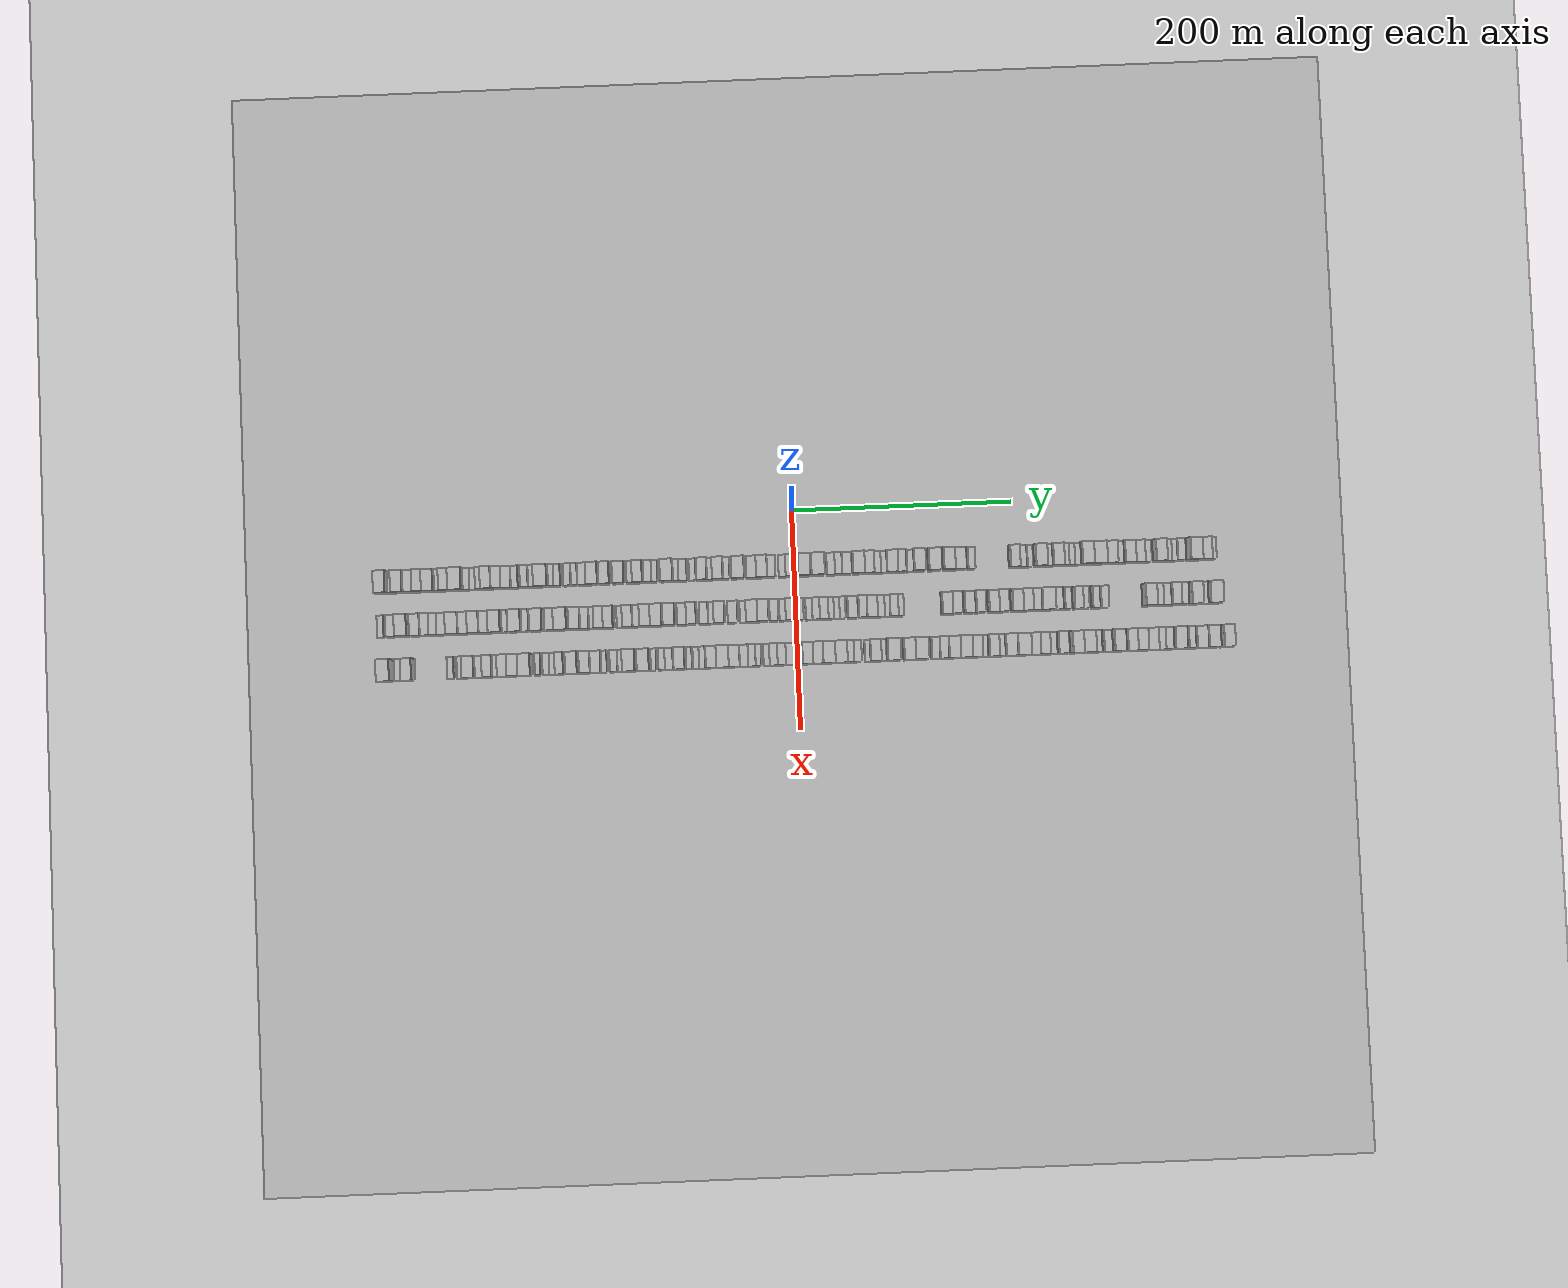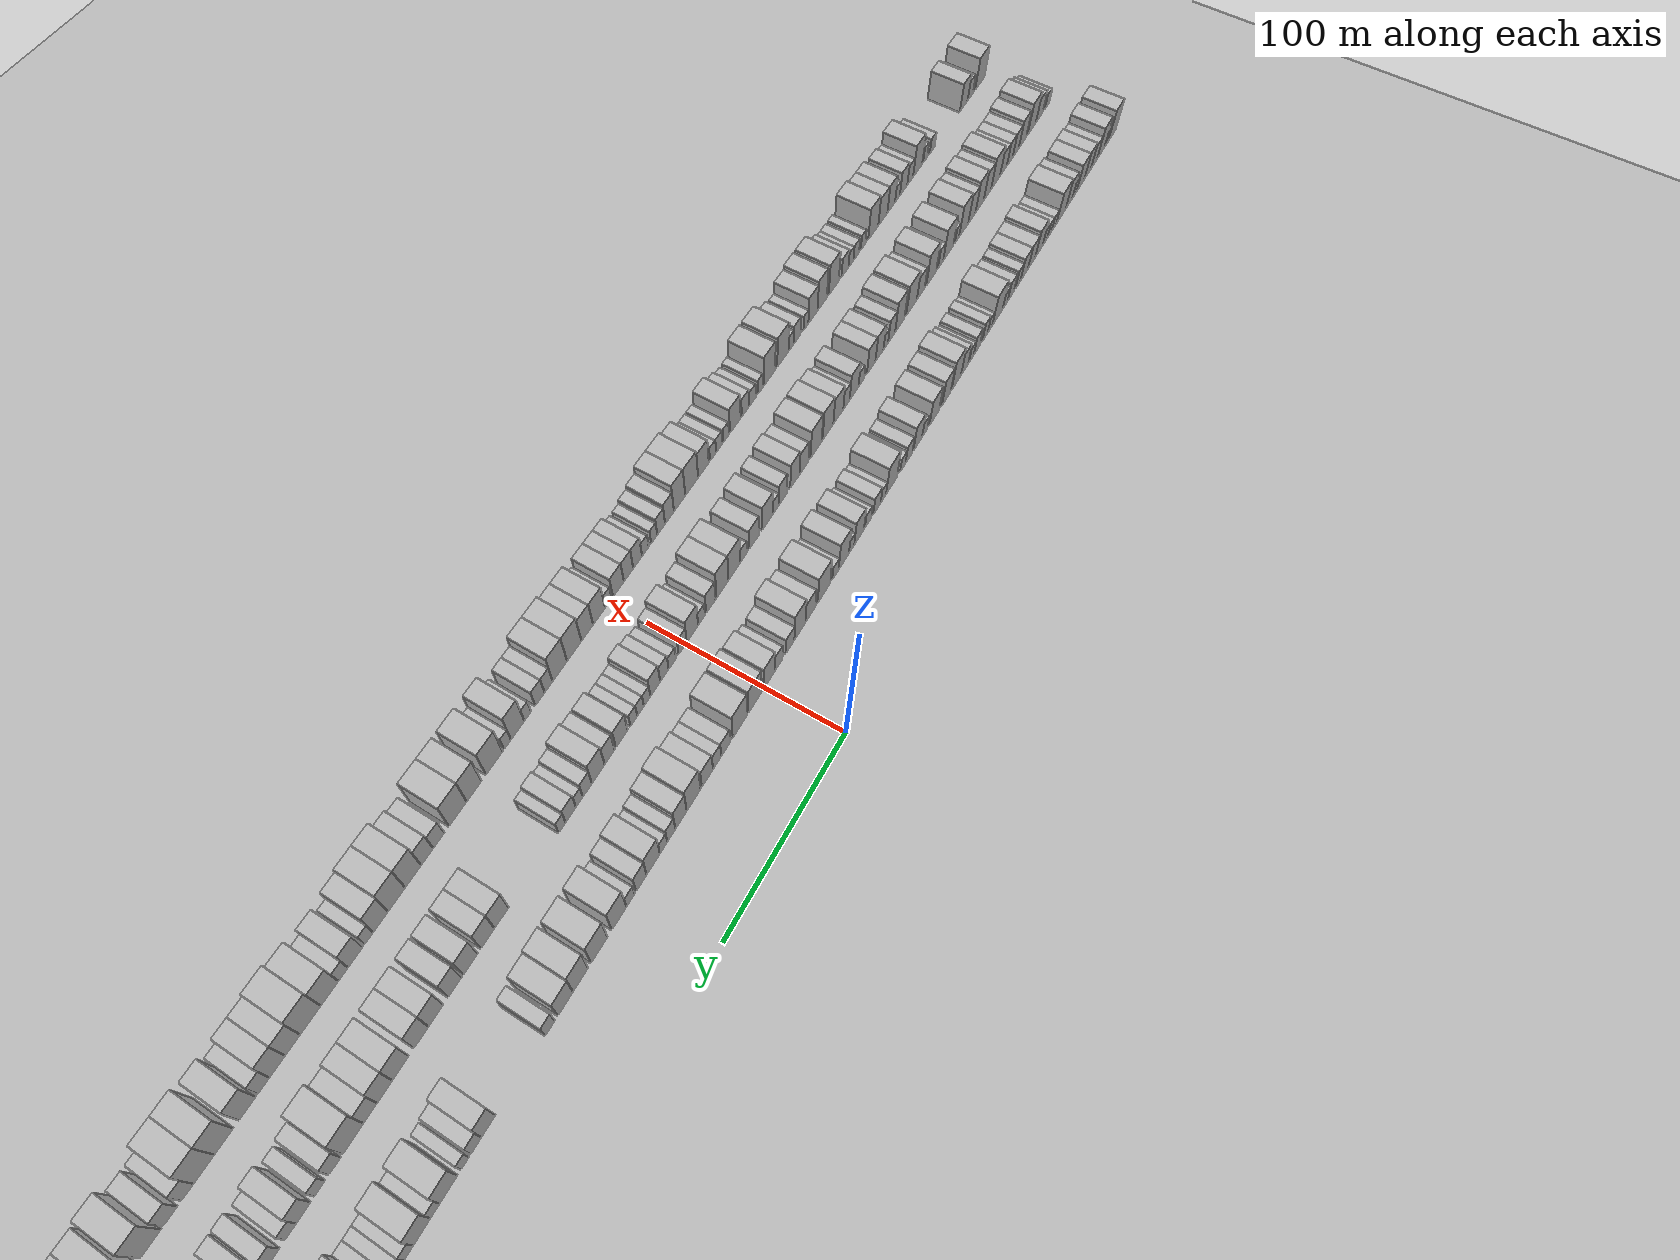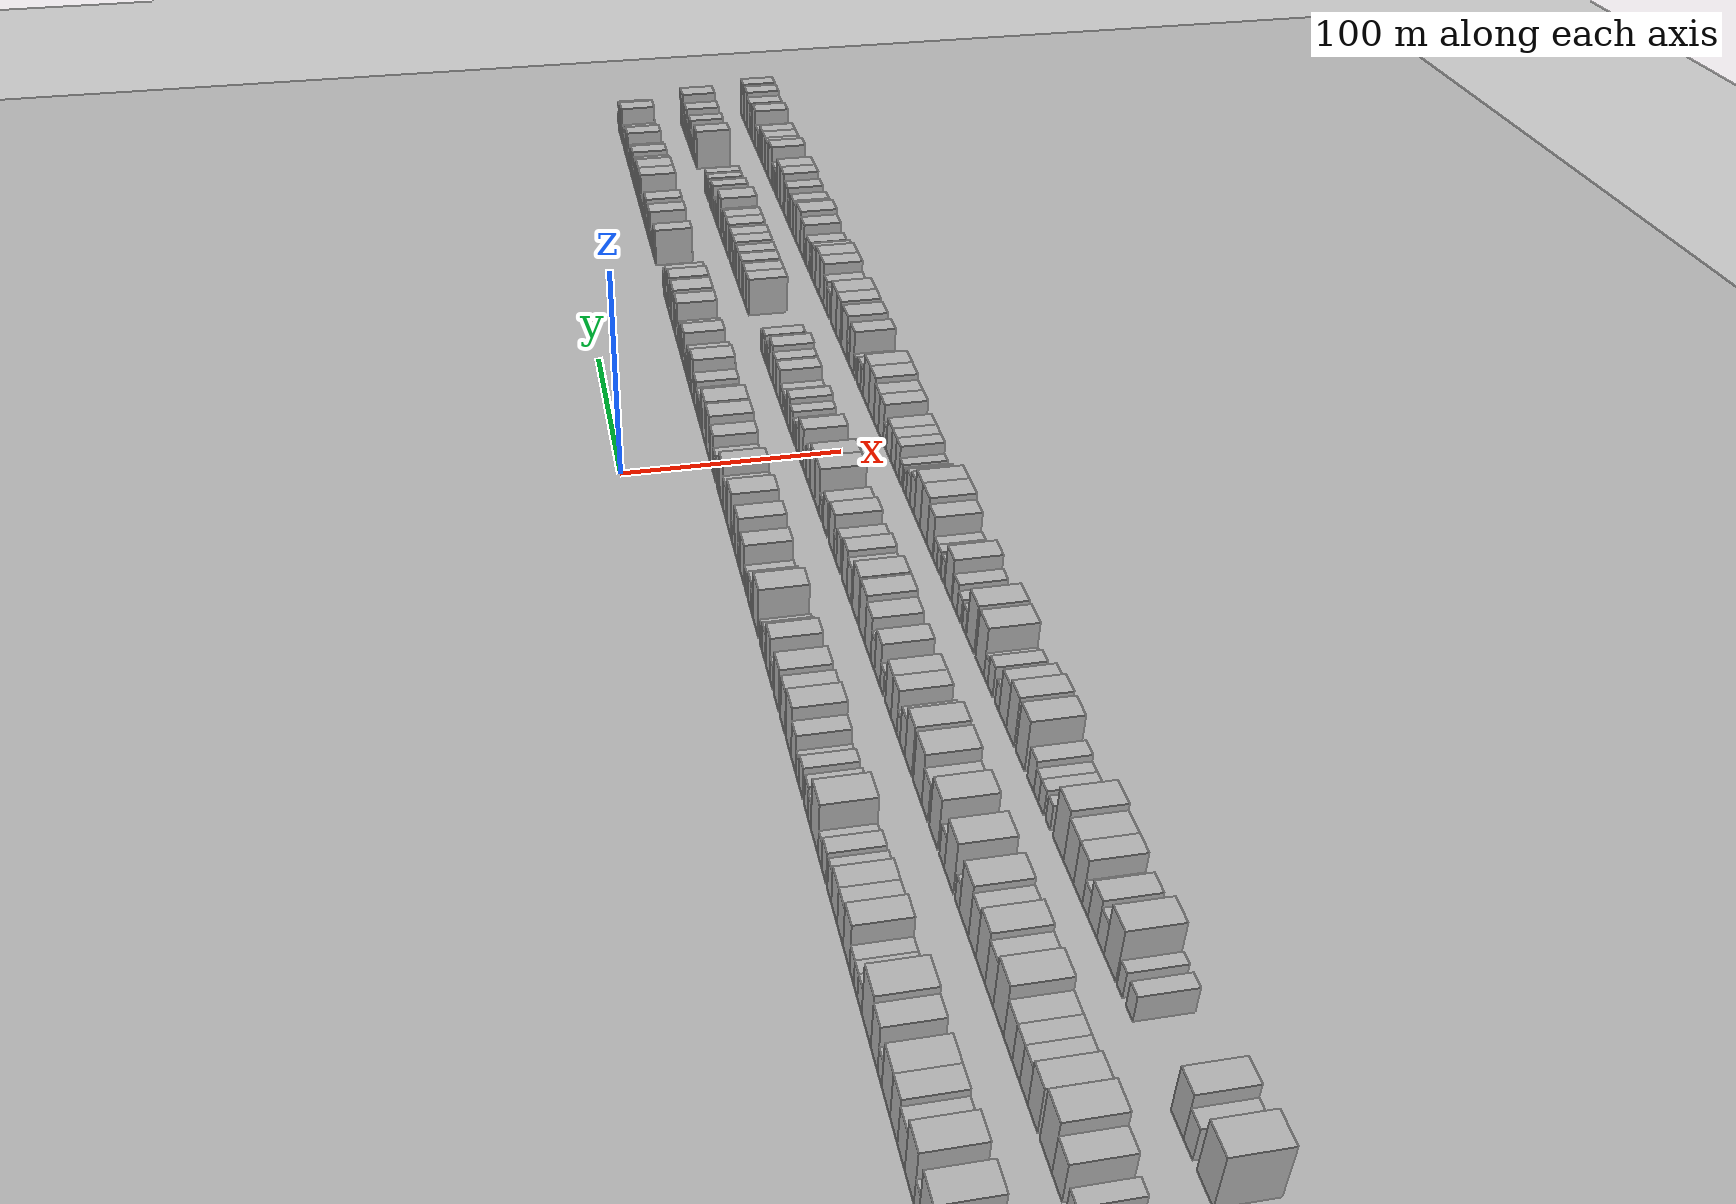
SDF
<?xml version="1.0" encoding="utf-8"?>

<sdf version="1.6">

   <world name="default">

      <gui fullscreen="0">

         <camera name="user_camera">

            <pose>-15 0 4.57585 0 0 0</pose>

            <view_controller>orbit</view_controller>

         </camera>

      </gui>

      <scene>

         <sky>

           <clouds>

             <speed>12</speed>

           </clouds>

         </sky>

         <ambient>0.4 0.4 0.4 1</ambient>

         <background>0.7 0.7 0.7 1</background>

         <shadows>1</shadows>

      </scene>

      <gravity>0 0 -9.8066</gravity>

      <magnetic_field>6e-06 2.3e-05 -4.2e-05</magnetic_field>

      <physics default="0" name="default_physics" type="ode">

         <ode>

            <solver>

               <type>quick</type>

               <iters>10</iters>

               <sor>1.0</sor>

               <use_dynamic_moi_rescaling>0</use_dynamic_moi_rescaling>

            </solver>

            <constraints>

               <cfm>0</cfm>

               <erp>0.2</erp>

               <contact_max_correcting_vel>100</contact_max_correcting_vel>

               <contact_surface_layer>0.001</contact_surface_layer>

            </constraints>

         </ode>

         <max_step_size>0.004</max_step_size>

         <real_time_factor>1</real_time_factor>

         <real_time_update_rate>250</real_time_update_rate>

      </physics>

      <light name="sun" type="directional">

         <cast_shadows>1</cast_shadows>

         <pose>0 0 10 0 0 0</pose>

         <diffuse>0.8 0.8 0.8 1</diffuse>

         <specular>0.2 0.2 0.2 1</specular>

         <attenuation>

            <range>1000</range>

            <constant>0.9</constant>

            <linear>0.01</linear>

            <quadratic>0.001</quadratic>

         </attenuation>

         <direction>-0.5 0.1 -0.9</direction>

      </light>

      <include>

         <name>ground_plane_1</name>

         <uri>model://HANNAS_ground_plane</uri>

         <pose>0 0 0  0 0 0</pose>

      </include>

      <include>

         <name>ground_plane_2</name>

         <uri>model://HANNAS_ground_plane</uri>

         <pose>100 0 0  0 0 0</pose>

      </include>

      <model name="building_1">

         <static>1</static>

         <pose frame="">50.0000 -374.7621 0 0.000000 0.000000 0.000000</pose>

         <link name="link">

            <pose frame="">0 0 12.00 0 0 0</pose>

            <collision name="collision">

               <geometry>

                  <box>

                     <size>20.0000 10.4758 24.0000</size>

                  </box>

               </geometry>

               <max_contacts>10</max_contacts>

               <surface>

                  <contact>

                     <ode/>

                  </contact>

                  <bounce/>

                  <friction>

                     <torsional>

                        <ode/>

                     </torsional>

                     <ode/>

                  </friction>

               </surface>

            </collision>

            <visual name="visual">

               <cast_shadows>0</cast_shadows>

               <geometry>

                  <box>

                     <size>20.0000 10.4758 24.0000</size>

                  </box>

               </geometry>

               <material>

                  <script>

                     <uri>model://HANNAS_wall/materials/scripts</uri>

                     <uri>model://HANNAS_wall/materials/textures</uri>

                     <name>vrc/HANNAS_wall</name>

                  </script>

               </material>

            </visual>

            <self_collide>0</self_collide>

            <enable_wind>0</enable_wind>

            <kinematic>0</kinematic>

         </link>

      </model>

      <model name="building_2">

         <static>1</static>

         <pose frame="">50.0000 -367.0660 0 0.000000 0.000000 0.000000</pose>

         <link name="link">

            <pose frame="">0 0 6.00 0 0 0</pose>

            <collision name="collision">

               <geometry>

                  <box>

                     <size>20.0000 4.9163 12.0000</size>

                  </box>

               </geometry>

               <max_contacts>10</max_contacts>

               <surface>

                  <contact>

                     <ode/>

                  </contact>

                  <bounce/>

                  <friction>

                     <torsional>

                        <ode/>

                     </torsional>

                     <ode/>

                  </friction>

               </surface>

            </collision>

            <visual name="visual">

               <cast_shadows>0</cast_shadows>

               <geometry>

                  <box>

                     <size>20.0000 4.9163 12.0000</size>

                  </box>

               </geometry>

               <material>

                  <script>

                     <uri>model://HANNAS_wall/materials/scripts</uri>

                     <uri>model://HANNAS_wall/materials/textures</uri>

                     <name>vrc/HANNAS_wall</name>

                  </script>

               </material>

            </visual>

            <self_collide>0</self_collide>

            <enable_wind>0</enable_wind>

            <kinematic>0</kinematic>

         </link>

      </model>

      <model name="building_3">

         <static>1</static>

         <pose frame="">50.0000 -359.5411 0 0.000000 0.000000 0.000000</pose>

         <link name="link">

            <pose frame="">0 0 12.00 0 0 0</pose>

            <collision name="collision">

               <geometry>

                  <box>

                     <size>20.0000 10.1335 24.0000</size>

                  </box>

               </geometry>

               <max_contacts>10</max_contacts>

               <surface>

                  <contact>

                     <ode/>

                  </contact>

                  <bounce/>

                  <friction>

                     <torsional>

                        <ode/>

                     </torsional>

                     <ode/>

                  </friction>

               </surface>

            </collision>

            <visual name="visual">

               <cast_shadows>0</cast_shadows>

               <geometry>

                  <box>

                     <size>20.0000 10.1335 24.0000</size>

                  </box>

               </geometry>

               <material>

                  <script>

                     <uri>model://HANNAS_wall/materials/scripts</uri>

                     <uri>model://HANNAS_wall/materials/textures</uri>

                     <name>vrc/HANNAS_wall</name>

                  </script>

               </material>

            </visual>

            <self_collide>0</self_collide>

            <enable_wind>0</enable_wind>

            <kinematic>0</kinematic>

         </link>

      </model>

      <model name="building_4">

         <static>1</static>

         <pose frame="">50.0000 -350.2581 0 0.000000 0.000000 0.000000</pose>

         <link name="link">

            <pose frame="">0 0 9.00 0 0 0</pose>

            <collision name="collision">

               <geometry>

                  <box>

                     <size>20.0000 8.4324 18.0000</size>

                  </box>

               </geometry>

               <max_contacts>10</max_contacts>

               <surface>

                  <contact>

                     <ode/>

                  </contact>

                  <bounce/>

                  <friction>

                     <torsional>

                        <ode/>

                     </torsional>

                     <ode/>

                  </friction>

               </surface>

            </collision>

            <visual name="visual">

               <cast_shadows>0</cast_shadows>

               <geometry>

                  <box>

                     <size>20.0000 8.4324 18.0000</size>

                  </box>

               </geometry>

               <material>

                  <script>

                     <uri>model://HANNAS_wall/materials/scripts</uri>

                     <uri>model://HANNAS_wall/materials/textures</uri>

                     <name>vrc/HANNAS_wall</name>

                  </script>

               </material>

            </visual>

            <self_collide>0</self_collide>

            <enable_wind>0</enable_wind>

            <kinematic>0</kinematic>

         </link>

      </model>

      <model name="building_5">

         <static>1</static>

         <pose frame="">50.0000 -341.7253 0 0.000000 0.000000 0.000000</pose>

         <link name="link">

            <pose frame="">0 0 10.50 0 0 0</pose>

            <collision name="collision">

               <geometry>

                  <box>

                     <size>20.0000 8.6331 21.0000</size>

                  </box>

               </geometry>

               <max_contacts>10</max_contacts>

               <surface>

                  <contact>

                     <ode/>

                  </contact>

                  <bounce/>

                  <friction>

                     <torsional>

                        <ode/>

                     </torsional>

                     <ode/>

                  </friction>

               </surface>

            </collision>

            <visual name="visual">

               <cast_shadows>0</cast_shadows>

               <geometry>

                  <box>

                     <size>20.0000 8.6331 21.0000</size>

                  </box>

               </geometry>

               <material>

                  <script>

                     <uri>model://HANNAS_wall/materials/scripts</uri>

                     <uri>model://HANNAS_wall/materials/textures</uri>

                     <name>vrc/HANNAS_wall</name>

                  </script>

               </material>

            </visual>

            <self_collide>0</self_collide>

            <enable_wind>0</enable_wind>

            <kinematic>0</kinematic>

         </link>

      </model>

      <model name="building_6">

         <static>1</static>

         <pose frame="">50.0000 -332.3009 0 0.000000 0.000000 0.000000</pose>

         <link name="link">

            <pose frame="">0 0 10.50 0 0 0</pose>

            <collision name="collision">

               <geometry>

                  <box>

                     <size>20.0000 10.2156 21.0000</size>

                  </box>

               </geometry>

               <max_contacts>10</max_contacts>

               <surface>

                  <contact>

                     <ode/>

                  </contact>

                  <bounce/>

                  <friction>

                     <torsional>

                        <ode/>

                     </torsional>

                     <ode/>

                  </friction>

               </surface>

            </collision>

            <visual name="visual">

               <cast_shadows>0</cast_shadows>

               <geometry>

                  <box>

                     <size>20.0000 10.2156 21.0000</size>

                  </box>

               </geometry>

               <material>

                  <script>

                     <uri>model://HANNAS_wall/materials/scripts</uri>

                     <uri>model://HANNAS_wall/materials/textures</uri>

                     <name>vrc/HANNAS_wall</name>

                  </script>

               </material>

            </visual>

            <self_collide>0</self_collide>

            <enable_wind>0</enable_wind>

            <kinematic>0</kinematic>

         </link>

      </model>

      <model name="building_7">

         <static>1</static>

         <pose frame="">50.0000 -324.5633 0 0.000000 0.000000 0.000000</pose>

         <link name="link">

            <pose frame="">0 0 6.00 0 0 0</pose>

            <collision name="collision">

               <geometry>

                  <box>

                     <size>20.0000 5.2597 12.0000</size>

                  </box>

               </geometry>

               <max_contacts>10</max_contacts>

               <surface>

                  <contact>

                     <ode/>

                  </contact>

                  <bounce/>

                  <friction>

                     <torsional>

                        <ode/>

                     </torsional>

                     <ode/>

                  </friction>

               </surface>

            </collision>

            <visual name="visual">

               <cast_shadows>0</cast_shadows>

               <geometry>

                  <box>

                     <size>20.0000 5.2597 12.0000</size>

                  </box>

               </geometry>

               <material>

                  <script>

                     <uri>model://HANNAS_wall/materials/scripts</uri>

                     <uri>model://HANNAS_wall/materials/textures</uri>

                     <name>vrc/HANNAS_wall</name>

                  </script>

               </material>

            </visual>

            <self_collide>0</self_collide>

            <enable_wind>0</enable_wind>

            <kinematic>0</kinematic>

         </link>

      </model>

      <model name="building_8">

         <static>1</static>

         <pose frame="">50.0000 -317.5954 0 0.000000 0.000000 0.000000</pose>

         <link name="link">

            <pose frame="">0 0 10.50 0 0 0</pose>

            <collision name="collision">

               <geometry>

                  <box>

                     <size>20.0000 8.6762 21.0000</size>

                  </box>

               </geometry>

               <max_contacts>10</max_contacts>

               <surface>

                  <contact>

                     <ode/>

                  </contact>

                  <bounce/>

                  <friction>

                     <torsional>

                        <ode/>

                     </torsional>

                     <ode/>

                  </friction>

               </surface>

            </collision>

            <visual name="visual">

               <cast_shadows>0</cast_shadows>

               <geometry>

                  <box>

                     <size>20.0000 8.6762 21.0000</size>

                  </box>

               </geometry>

               <material>

                  <script>

                     <uri>model://HANNAS_wall/materials/scripts</uri>

                     <uri>model://HANNAS_wall/materials/textures</uri>

                     <name>vrc/HANNAS_wall</name>

                  </script>

               </material>

            </visual>

            <self_collide>0</self_collide>

            <enable_wind>0</enable_wind>

            <kinematic>0</kinematic>

         </link>

      </model>

      <model name="building_9">

         <static>1</static>

         <pose frame="">50.0000 -307.2627 0 0.000000 0.000000 0.000000</pose>

         <link name="link">

            <pose frame="">0 0 12.00 0 0 0</pose>

            <collision name="collision">

               <geometry>

                  <box>

                     <size>20.0000 11.9893 24.0000</size>

                  </box>

               </geometry>

               <max_contacts>10</max_contacts>

               <surface>

                  <contact>

                     <ode/>

                  </contact>

                  <bounce/>

                  <friction>

                     <torsional>

                        <ode/>

                     </torsional>

                     <ode/>

                  </friction>

               </surface>

            </collision>

            <visual name="visual">

               <cast_shadows>0</cast_shadows>

               <geometry>

                  <box>

                     <size>20.0000 11.9893 24.0000</size>

                  </box>

               </geometry>

               <material>

                  <script>

                     <uri>model://HANNAS_wall/materials/scripts</uri>

                     <uri>model://HANNAS_wall/materials/textures</uri>

                     <name>vrc/HANNAS_wall</name>

                  </script>

               </material>

            </visual>

            <self_collide>0</self_collide>

            <enable_wind>0</enable_wind>

            <kinematic>0</kinematic>

         </link>

      </model>

      <model name="building_10">

         <static>1</static>

         <pose frame="">50.0000 -298.2695 0 0.000000 0.000000 0.000000</pose>

         <link name="link">

            <pose frame="">0 0 6.00 0 0 0</pose>

            <collision name="collision">

               <geometry>

                  <box>

                     <size>20.0000 5.9970 12.0000</size>

                  </box>

               </geometry>

               <max_contacts>10</max_contacts>

               <surface>

                  <contact>

                     <ode/>

                  </contact>

                  <bounce/>

                  <friction>

                     <torsional>

                        <ode/>

                     </torsional>

                     <ode/>

                  </friction>

               </surface>

            </collision>

            <visual name="visual">

               <cast_shadows>0</cast_shadows>

               <geometry>

                  <box>

                     <size>20.0000 5.9970 12.0000</size>

                  </box>

               </geometry>

               <material>

                  <script>

                     <uri>model://HANNAS_wall/materials/scripts</uri>

                     <uri>model://HANNAS_wall/materials/textures</uri>

                     <name>vrc/HANNAS_wall</name>

                  </script>

               </material>

            </visual>

            <self_collide>0</self_collide>

            <enable_wind>0</enable_wind>

            <kinematic>0</kinematic>

         </link>

      </model>

      <model name="building_11">

         <static>1</static>

         <pose frame="">50.0000 -292.7039 0 0.000000 0.000000 0.000000</pose>

         <link name="link">

            <pose frame="">0 0 6.00 0 0 0</pose>

            <collision name="collision">

               <geometry>

                  <box>

                     <size>20.0000 5.1343 12.0000</size>

                  </box>

               </geometry>

               <max_contacts>10</max_contacts>

               <surface>

                  <contact>

                     <ode/>

                  </contact>

                  <bounce/>

                  <friction>

                     <torsional>

                        <ode/>

                     </torsional>

                     <ode/>

                  </friction>

               </surface>

            </collision>

            <visual name="visual">

               <cast_shadows>0</cast_shadows>

               <geometry>

                  <box>

                     <size>20.0000 5.1343 12.0000</size>

                  </box>

               </geometry>

               <material>

                  <script>

                     <uri>model://HANNAS_wall/materials/scripts</uri>

                     <uri>model://HANNAS_wall/materials/textures</uri>

                     <name>vrc/HANNAS_wall</name>

                  </script>

               </material>

            </visual>

            <self_collide>0</self_collide>

            <enable_wind>0</enable_wind>

            <kinematic>0</kinematic>

         </link>

      </model>

      <model name="building_12">

         <static>1</static>

         <pose frame="">50.0000 -287.2224 0 0.000000 0.000000 0.000000</pose>

         <link name="link">

            <pose frame="">0 0 6.00 0 0 0</pose>

            <collision name="collision">

               <geometry>

                  <box>

                     <size>20.0000 5.8285 12.0000</size>

                  </box>

               </geometry>

               <max_contacts>10</max_contacts>

               <surface>

                  <contact>

                     <ode/>

                  </contact>

                  <bounce/>

                  <friction>

                     <torsional>

                        <ode/>

                     </torsional>

                     <ode/>

                  </friction>

               </surface>

            </collision>

            <visual name="visual">

               <cast_shadows>0</cast_shadows>

               <geometry>

                  <box>

                     <size>20.0000 5.8285 12.0000</size>

                  </box>

               </geometry>

               <material>

                  <script>

                     <uri>model://HANNAS_wall/materials/scripts</uri>

                     <uri>model://HANNAS_wall/materials/textures</uri>

                     <name>vrc/HANNAS_wall</name>

                  </script>

               </material>

            </visual>

            <self_collide>0</self_collide>

            <enable_wind>0</enable_wind>

            <kinematic>0</kinematic>

         </link>

      </model>

      <model name="building_13">

         <static>1</static>

         <pose frame="">50.0000 -279.6714 0 0.000000 0.000000 0.000000</pose>

         <link name="link">

            <pose frame="">0 0 10.50 0 0 0</pose>

            <collision name="collision">

               <geometry>

                  <box>

                     <size>20.0000 9.2735 21.0000</size>

                  </box>

               </geometry>

               <max_contacts>10</max_contacts>

               <surface>

                  <contact>

                     <ode/>

                  </contact>

                  <bounce/>

                  <friction>

                     <torsional>

                        <ode/>

                     </torsional>

                     <ode/>

                  </friction>

               </surface>

            </collision>

            <visual name="visual">

               <cast_shadows>0</cast_shadows>

               <geometry>

                  <box>

                     <size>20.0000 9.2735 21.0000</size>

                  </box>

               </geometry>

               <material>

                  <script>

                     <uri>model://HANNAS_wall/materials/scripts</uri>

                     <uri>model://HANNAS_wall/materials/textures</uri>

                     <name>vrc/HANNAS_wall</name>

                  </script>

               </material>

            </visual>

            <self_collide>0</self_collide>

            <enable_wind>0</enable_wind>

            <kinematic>0</kinematic>

         </link>

      </model>

      <model name="building_14">

         <static>1</static>

         <pose frame="">50.0000 -270.6329 0 0.000000 0.000000 0.000000</pose>

         <link name="link">

            <pose frame="">0 0 9.00 0 0 0</pose>

            <collision name="collision">

               <geometry>

                  <box>

                     <size>20.0000 8.8036 18.0000</size>

                  </box>

               </geometry>

               <max_contacts>10</max_contacts>

               <surface>

                  <contact>

                     <ode/>

                  </contact>

                  <bounce/>

                  <friction>

                     <torsional>

                        <ode/>

                     </torsional>

                     <ode/>

                  </friction>

               </surface>

            </collision>

            <visual name="visual">

               <cast_shadows>0</cast_shadows>

               <geometry>

                  <box>

                     <size>20.0000 8.8036 18.0000</size>

                  </box>

               </geometry>

               <material>

                  <script>

                     <uri>model://HANNAS_wall/materials/scripts</uri>

                     <uri>model://HANNAS_wall/materials/textures</uri>

                     <name>vrc/HANNAS_wall</name>

                  </script>

               </material>

            </visual>

            <self_collide>0</self_collide>

            <enable_wind>0</enable_wind>

            <kinematic>0</kinematic>

         </link>

      </model>

      <model name="building_15">

         <static>1</static>

         <pose frame="">50.0000 -261.7483 0 0.000000 0.000000 0.000000</pose>

         <link name="link">

            <pose frame="">0 0 9.00 0 0 0</pose>

            <collision name="collision">

               <geometry>

                  <box>

                     <size>20.0000 8.9656 18.0000</size>

                  </box>

               </geometry>

               <max_contacts>10</max_contacts>

               <surface>

                  <contact>

                     <ode/>

                  </contact>

                  <bounce/>

                  <friction>

                     <torsional>

                        <ode/>

                     </torsional>

                     <ode/>

                  </friction>

               </surface>

            </collision>

            <visual name="visual">

               <cast_shadows>0</cast_shadows>

               <geometry>

                  <box>

                     <size>20.0000 8.9656 18.0000</size>

                  </box>

               </geometry>

               <material>

                  <script>

                     <uri>model://HANNAS_wall/materials/scripts</uri>

                     <uri>model://HANNAS_wall/materials/textures</uri>

                     <name>vrc/HANNAS_wall</name>

                  </script>

               </material>

            </visual>

            <self_collide>0</self_collide>

            <enable_wind>0</enable_wind>

            <kinematic>0</kinematic>

         </link>

      </model>

      <model name="building_16">

         <static>1</static>

         <pose frame="">50.0000 -254.1331 0 0.000000 0.000000 0.000000</pose>

         <link name="link">

            <pose frame="">0 0 7.50 0 0 0</pose>

            <collision name="collision">

               <geometry>

                  <box>

                     <size>20.0000 6.2648 15.0000</size>

                  </box>

               </geometry>

               <max_contacts>10</max_contacts>

               <surface>

                  <contact>

                     <ode/>

                  </contact>

                  <bounce/>

                  <friction>

                     <torsional>

                        <ode/>

                     </torsional>

                     <ode/>

                  </friction>

               </surface>

            </collision>

            <visual name="visual">

               <cast_shadows>0</cast_shadows>

               <geometry>

                  <box>

                     <size>20.0000 6.2648 15.0000</size>

                  </box>

               </geometry>

               <material>

                  <script>

                     <uri>model://HANNAS_wall/materials/scripts</uri>

                     <uri>model://HANNAS_wall/materials/textures</uri>

                     <name>vrc/HANNAS_wall</name>

                  </script>

               </material>

            </visual>

            <self_collide>0</self_collide>

            <enable_wind>0</enable_wind>

            <kinematic>0</kinematic>

         </link>

      </model>

      <model name="building_17">

         <static>1</static>

         <pose frame="">50.0000 -245.4952 0 0.000000 0.000000 0.000000</pose>

         <link name="link">

            <pose frame="">0 0 7.50 0 0 0</pose>

            <collision name="collision">

               <geometry>

                  <box>

                     <size>20.0000 7.0111 15.0000</size>

                  </box>

               </geometry>

               <max_contacts>10</max_contacts>

               <surface>

                  <contact>

                     <ode/>

                  </contact>

                  <bounce/>

                  <friction>

                     <torsional>

                        <ode/>

                     </torsional>

                     <ode/>

                  </friction>

               </surface>

            </collision>

            <visual name="visual">

               <cast_shadows>0</cast_shadows>

               <geometry>

                  <box>

                     <size>20.0000 7.0111 15.0000</size>

                  </box>

               </geometry>

               <material>

                  <script>

                     <uri>model://HANNAS_wall/materials/scripts</uri>

                     <uri>model://HANNAS_wall/materials/textures</uri>

                     <name>vrc/HANNAS_wall</name>

                  </script>

               </material>

            </visual>

            <self_collide>0</self_collide>

            <enable_wind>0</enable_wind>

            <kinematic>0</kinematic>

         </link>

      </model>

      <model name="building_18">

         <static>1</static>

         <pose frame="">50.0000 -239.0302 0 0.000000 0.000000 0.000000</pose>

         <link name="link">

            <pose frame="">0 0 6.00 0 0 0</pose>

            <collision name="collision">

               <geometry>

                  <box>

                     <size>20.0000 5.9189 12.0000</size>

                  </box>

               </geometry>

               <max_contacts>10</max_contacts>

               <surface>

                  <contact>

                     <ode/>

                  </contact>

                  <bounce/>

                  <friction>

                     <torsional>

                        <ode/>

                     </torsional>

                     <ode/>

                  </friction>

               </surface>

            </collision>

            <visual name="visual">

               <cast_shadows>0</cast_shadows>

               <geometry>

                  <box>

                     <size>20.0000 5.9189 12.0000</size>

                  </box>

               </geometry>

               <material>

                  <script>

                     <uri>model://HANNAS_wall/materials/scripts</uri>

                     <uri>model://HANNAS_wall/materials/textures</uri>

                     <name>vrc/HANNAS_wall</name>

                  </script>

               </material>

            </visual>

            <self_collide>0</self_collide>

            <enable_wind>0</enable_wind>

            <kinematic>0</kinematic>

         </link>

      </model>

      <model name="building_19">

         <static>1</static>

         <pose frame="">50.0000 -230.0739 0 0.000000 0.000000 0.000000</pose>

         <link name="link">

            <pose frame="">0 0 12.00 0 0 0</pose>

            <collision name="collision">

               <geometry>

                  <box>

                     <size>20.0000 11.9937 24.0000</size>

                  </box>

               </geometry>

               <max_contacts>10</max_contacts>

               <surface>

                  <contact>

                     <ode/>

                  </contact>

                  <bounce/>

                  <friction>

                     <torsional>

                        <ode/>

                     </torsional>

                     <ode/>

                  </friction>

               </surface>

            </collision>

            <visual name="visual">

               <cast_shadows>0</cast_shadows>

               <geometry>

                  <box>

                     <size>20.0000 11.9937 24.0000</size>

                  </box>

               </geometry>

               <material>

                  <script>

                     <uri>model://HANNAS_wall/materials/scripts</uri>

                     <uri>model://HANNAS_wall/materials/textures</uri>

                     <name>vrc/HANNAS_wall</name>

                  </script>

               </material>

            </visual>

            <self_collide>0</self_collide>

            <enable_wind>0</enable_wind>

            <kinematic>0</kinematic>

         </link>

      </model>

      <model name="building_20">

         <static>1</static>

         <pose frame="">50.0000 -221.4494 0 0.000000 0.000000 0.000000</pose>

         <link name="link">

            <pose frame="">0 0 6.00 0 0 0</pose>

            <collision name="collision">

               <geometry>

                  <box>

                     <size>20.0000 5.2555 12.0000</size>

                  </box>

               </geometry>

               <max_contacts>10</max_contacts>

               <surface>

                  <contact>

                     <ode/>

                  </contact>

                  <bounce/>

                  <friction>

                     <torsional>

                        <ode/>

                     </torsional>

                     <ode/>

                  </friction>

               </surface>

            </collision>

            <visual name="visual">

               <cast_shadows>0</cast_shadows>

               <geometry>

                  <box>

                     <size>20.0000 5.2555 12.0000</size>

                  </box>

               </geometry>

               <material>

                  <script>

                     <uri>model://HANNAS_wall/materials/scripts</uri>

                     <uri>model://HANNAS_wall/materials/textures</uri>

                     <name>vrc/HANNAS_wall</name>

                  </script>

               </material>

            </visual>

            <self_collide>0</self_collide>

            <enable_wind>0</enable_wind>

            <kinematic>0</kinematic>

         </link>

      </model>

      <model name="building_21">

         <static>1</static>

         <pose frame="">50.0000 -215.7744 0 0.000000 0.000000 0.000000</pose>

         <link name="link">

            <pose frame="">0 0 7.50 0 0 0</pose>

            <collision name="collision">

               <geometry>

                  <box>

                     <size>20.0000 6.0945 15.0000</size>

                  </box>

               </geometry>

               <max_contacts>10</max_contacts>

               <surface>

                  <contact>

                     <ode/>

                  </contact>

                  <bounce/>

                  <friction>

                     <torsional>

                        <ode/>

                     </torsional>

                     <ode/>

                  </friction>

               </surface>

            </collision>

            <visual name="visual">

               <cast_shadows>0</cast_shadows>

               <geometry>

                  <box>

                     <size>20.0000 6.0945 15.0000</size>

                  </box>

               </geometry>

               <material>

                  <script>

                     <uri>model://HANNAS_wall/materials/scripts</uri>

                     <uri>model://HANNAS_wall/materials/textures</uri>

                     <name>vrc/HANNAS_wall</name>

                  </script>

               </material>

            </visual>

            <self_collide>0</self_collide>

            <enable_wind>0</enable_wind>

            <kinematic>0</kinematic>

         </link>

      </model>

      <model name="building_22">

         <static>1</static>

         <pose frame="">50.0000 -206.4561 0 0.000000 0.000000 0.000000</pose>

         <link name="link">

            <pose frame="">0 0 7.50 0 0 0</pose>

            <collision name="collision">

               <geometry>

                  <box>

                     <size>20.0000 6.5420 15.0000</size>

                  </box>

               </geometry>

               <max_contacts>10</max_contacts>

               <surface>

                  <contact>

                     <ode/>

                  </contact>

                  <bounce/>

                  <friction>

                     <torsional>

                        <ode/>

                     </torsional>

                     <ode/>

                  </friction>

               </surface>

            </collision>

            <visual name="visual">

               <cast_shadows>0</cast_shadows>

               <geometry>

                  <box>

                     <size>20.0000 6.5420 15.0000</size>

                  </box>

               </geometry>

               <material>

                  <script>

                     <uri>model://HANNAS_wall/materials/scripts</uri>

                     <uri>model://HANNAS_wall/materials/textures</uri>

                     <name>vrc/HANNAS_wall</name>

                  </script>

               </material>

            </visual>

            <self_collide>0</self_collide>

            <enable_wind>0</enable_wind>

            <kinematic>0</kinematic>

         </link>

      </model>

      <model name="building_23">

         <static>1</static>

         <pose frame="">50.0000 -200.4488 0 0.000000 0.000000 0.000000</pose>

         <link name="link">

            <pose frame="">0 0 6.00 0 0 0</pose>

            <collision name="collision">

               <geometry>

                  <box>

                     <size>20.0000 5.4726 12.0000</size>

                  </box>

               </geometry>

               <max_contacts>10</max_contacts>

               <surface>

                  <contact>

                     <ode/>

                  </contact>

                  <bounce/>

                  <friction>

                     <torsional>

                        <ode/>

                     </torsional>

                     <ode/>

                  </friction>

               </surface>

            </collision>

            <visual name="visual">

               <cast_shadows>0</cast_shadows>

               <geometry>

                  <box>

                     <size>20.0000 5.4726 12.0000</size>

                  </box>

               </geometry>

               <material>

                  <script>

                     <uri>model://HANNAS_wall/materials/scripts</uri>

                     <uri>model://HANNAS_wall/materials/textures</uri>

                     <name>vrc/HANNAS_wall</name>

                  </script>

               </material>

            </visual>

            <self_collide>0</self_collide>

            <enable_wind>0</enable_wind>

            <kinematic>0</kinematic>

         </link>

      </model>

      <model name="building_24">

         <static>1</static>

         <pose frame="">50.0000 -192.8077 0 0.000000 0.000000 0.000000</pose>

         <link name="link">

            <pose frame="">0 0 9.00 0 0 0</pose>

            <collision name="collision">

               <geometry>

                  <box>

                     <size>20.0000 7.8096 18.0000</size>

                  </box>

               </geometry>

               <max_contacts>10</max_contacts>

               <surface>

                  <contact>

                     <ode/>

                  </contact>

                  <bounce/>

                  <friction>

                     <torsional>

                        <ode/>

                     </torsional>

                     <ode/>

                  </friction>

               </surface>

            </collision>

            <visual name="visual">

               <cast_shadows>0</cast_shadows>

               <geometry>

                  <box>

                     <size>20.0000 7.8096 18.0000</size>

                  </box>

               </geometry>

               <material>

                  <script>

                     <uri>model://HANNAS_wall/materials/scripts</uri>

                     <uri>model://HANNAS_wall/materials/textures</uri>

                     <name>vrc/HANNAS_wall</name>

                  </script>

               </material>

            </visual>

            <self_collide>0</self_collide>

            <enable_wind>0</enable_wind>

            <kinematic>0</kinematic>

         </link>

      </model>

      <model name="building_25">

         <static>1</static>

         <pose frame="">50.0000 -183.6982 0 0.000000 0.000000 0.000000</pose>

         <link name="link">

            <pose frame="">0 0 12.00 0 0 0</pose>

            <collision name="collision">

               <geometry>

                  <box>

                     <size>20.0000 10.4094 24.0000</size>

                  </box>

               </geometry>

               <max_contacts>10</max_contacts>

               <surface>

                  <contact>

                     <ode/>

                  </contact>

                  <bounce/>

                  <friction>

                     <torsional>

                        <ode/>

                     </torsional>

                     <ode/>

                  </friction>

               </surface>

            </collision>

            <visual name="visual">

               <cast_shadows>0</cast_shadows>

               <geometry>

                  <box>

                     <size>20.0000 10.4094 24.0000</size>

                  </box>

               </geometry>

               <material>

                  <script>

                     <uri>model://HANNAS_wall/materials/scripts</uri>

                     <uri>model://HANNAS_wall/materials/textures</uri>

                     <name>vrc/HANNAS_wall</name>

                  </script>

               </material>

            </visual>

            <self_collide>0</self_collide>

            <enable_wind>0</enable_wind>

            <kinematic>0</kinematic>

         </link>

      </model>

      <model name="building_26">

         <static>1</static>

         <pose frame="">50.0000 -172.7944 0 0.000000 0.000000 0.000000</pose>

         <link name="link">

            <pose frame="">0 0 10.50 0 0 0</pose>

            <collision name="collision">

               <geometry>

                  <box>

                     <size>20.0000 9.3983 21.0000</size>

                  </box>

               </geometry>

               <max_contacts>10</max_contacts>

               <surface>

                  <contact>

                     <ode/>

                  </contact>

                  <bounce/>

                  <friction>

                     <torsional>

                        <ode/>

                     </torsional>

                     <ode/>

                  </friction>

               </surface>

            </collision>

            <visual name="visual">

               <cast_shadows>0</cast_shadows>

               <geometry>

                  <box>

                     <size>20.0000 9.3983 21.0000</size>

                  </box>

               </geometry>

               <material>

                  <script>

                     <uri>model://HANNAS_wall/materials/scripts</uri>

                     <uri>model://HANNAS_wall/materials/textures</uri>

                     <name>vrc/HANNAS_wall</name>

                  </script>

               </material>

            </visual>

            <self_collide>0</self_collide>

            <enable_wind>0</enable_wind>

            <kinematic>0</kinematic>

         </link>

      </model>

      <model name="building_27">

         <static>1</static>

         <pose frame="">50.0000 -159.9652 0 0.000000 0.000000 0.000000</pose>

         <link name="link">

            <pose frame="">0 0 10.50 0 0 0</pose>

            <collision name="collision">

               <geometry>

                  <box>

                     <size>20.0000 10.2600 21.0000</size>

                  </box>

               </geometry>

               <max_contacts>10</max_contacts>

               <surface>

                  <contact>

                     <ode/>

                  </contact>

                  <bounce/>

                  <friction>

                     <torsional>

                        <ode/>

                     </torsional>

                     <ode/>

                  </friction>

               </surface>

            </collision>

            <visual name="visual">

               <cast_shadows>0</cast_shadows>

               <geometry>

                  <box>

                     <size>20.0000 10.2600 21.0000</size>

                  </box>

               </geometry>

               <material>

                  <script>

                     <uri>model://HANNAS_wall/materials/scripts</uri>

                     <uri>model://HANNAS_wall/materials/textures</uri>

                     <name>vrc/HANNAS_wall</name>

                  </script>

               </material>

            </visual>

            <self_collide>0</self_collide>

            <enable_wind>0</enable_wind>

            <kinematic>0</kinematic>

         </link>

      </model>

      <model name="building_28">

         <static>1</static>

         <pose frame="">50.0000 -150.0657 0 0.000000 0.000000 0.000000</pose>

         <link name="link">

            <pose frame="">0 0 6.00 0 0 0</pose>

            <collision name="collision">

               <geometry>

                  <box>

                     <size>20.0000 5.5390 12.0000</size>

                  </box>

               </geometry>

               <max_contacts>10</max_contacts>

               <surface>

                  <contact>

                     <ode/>

                  </contact>

                  <bounce/>

                  <friction>

                     <torsional>

                        <ode/>

                     </torsional>

                     <ode/>

                  </friction>

               </surface>

            </collision>

            <visual name="visual">

               <cast_shadows>0</cast_shadows>

               <geometry>

                  <box>

                     <size>20.0000 5.5390 12.0000</size>

                  </box>

               </geometry>

               <material>

                  <script>

                     <uri>model://HANNAS_wall/materials/scripts</uri>

                     <uri>model://HANNAS_wall/materials/textures</uri>

                     <name>vrc/HANNAS_wall</name>

                  </script>

               </material>

            </visual>

            <self_collide>0</self_collide>

            <enable_wind>0</enable_wind>

            <kinematic>0</kinematic>

         </link>

      </model>

      <model name="building_29">

         <static>1</static>

         <pose frame="">50.0000 -142.7747 0 0.000000 0.000000 0.000000</pose>

         <link name="link">

            <pose frame="">0 0 10.50 0 0 0</pose>

            <collision name="collision">

               <geometry>

                  <box>

                     <size>20.0000 9.0430 21.0000</size>

                  </box>

               </geometry>

               <max_contacts>10</max_contacts>

               <surface>

                  <contact>

                     <ode/>

                  </contact>

                  <bounce/>

                  <friction>

                     <torsional>

                        <ode/>

                     </torsional>

                     <ode/>

                  </friction>

               </surface>

            </collision>

            <visual name="visual">

               <cast_shadows>0</cast_shadows>

               <geometry>

                  <box>

                     <size>20.0000 9.0430 21.0000</size>

                  </box>

               </geometry>

               <material>

                  <script>

                     <uri>model://HANNAS_wall/materials/scripts</uri>

                     <uri>model://HANNAS_wall/materials/textures</uri>

                     <name>vrc/HANNAS_wall</name>

                  </script>

               </material>

            </visual>

            <self_collide>0</self_collide>

            <enable_wind>0</enable_wind>

            <kinematic>0</kinematic>

         </link>

      </model>

      <model name="building_30">

         <static>1</static>

         <pose frame="">50.0000 -133.7308 0 0.000000 0.000000 0.000000</pose>

         <link name="link">

            <pose frame="">0 0 7.50 0 0 0</pose>

            <collision name="collision">

               <geometry>

                  <box>

                     <size>20.0000 7.0449 15.0000</size>

                  </box>

               </geometry>

               <max_contacts>10</max_contacts>

               <surface>

                  <contact>

                     <ode/>

                  </contact>

                  <bounce/>

                  <friction>

                     <torsional>

                        <ode/>

                     </torsional>

                     <ode/>

                  </friction>

               </surface>

            </collision>

            <visual name="visual">

               <cast_shadows>0</cast_shadows>

               <geometry>

                  <box>

                     <size>20.0000 7.0449 15.0000</size>

                  </box>

               </geometry>

               <material>

                  <script>

                     <uri>model://HANNAS_wall/materials/scripts</uri>

                     <uri>model://HANNAS_wall/materials/textures</uri>

                     <name>vrc/HANNAS_wall</name>

                  </script>

               </material>

            </visual>

            <self_collide>0</self_collide>

            <enable_wind>0</enable_wind>

            <kinematic>0</kinematic>

         </link>

      </model>

      <model name="building_31">

         <static>1</static>

         <pose frame="">50.0000 -127.4905 0 0.000000 0.000000 0.000000</pose>

         <link name="link">

            <pose frame="">0 0 6.00 0 0 0</pose>

            <collision name="collision">

               <geometry>

                  <box>

                     <size>20.0000 5.4356 12.0000</size>

                  </box>

               </geometry>

               <max_contacts>10</max_contacts>

               <surface>

                  <contact>

                     <ode/>

                  </contact>

                  <bounce/>

                  <friction>

                     <torsional>

                        <ode/>

                     </torsional>

                     <ode/>

                  </friction>

               </surface>

            </collision>

            <visual name="visual">

               <cast_shadows>0</cast_shadows>

               <geometry>

                  <box>

                     <size>20.0000 5.4356 12.0000</size>

                  </box>

               </geometry>

               <material>

                  <script>

                     <uri>model://HANNAS_wall/materials/scripts</uri>

                     <uri>model://HANNAS_wall/materials/textures</uri>

                     <name>vrc/HANNAS_wall</name>

                  </script>

               </material>

            </visual>

            <self_collide>0</self_collide>

            <enable_wind>0</enable_wind>

            <kinematic>0</kinematic>

         </link>

      </model>

      <model name="building_32">

         <static>1</static>

         <pose frame="">50.0000 -116.2750 0 0.000000 0.000000 0.000000</pose>

         <link name="link">

            <pose frame="">0 0 12.00 0 0 0</pose>

            <collision name="collision">

               <geometry>

                  <box>

                     <size>20.0000 10.9953 24.0000</size>

                  </box>

               </geometry>

               <max_contacts>10</max_contacts>

               <surface>

                  <contact>

                     <ode/>

                  </contact>

                  <bounce/>

                  <friction>

                     <torsional>

                        <ode/>

                     </torsional>

                     <ode/>

                  </friction>

               </surface>

            </collision>

            <visual name="visual">

               <cast_shadows>0</cast_shadows>

               <geometry>

                  <box>

                     <size>20.0000 10.9953 24.0000</size>

                  </box>

               </geometry>

               <material>

                  <script>

                     <uri>model://HANNAS_wall/materials/scripts</uri>

                     <uri>model://HANNAS_wall/materials/textures</uri>

                     <name>vrc/HANNAS_wall</name>

                  </script>

               </material>

            </visual>

            <self_collide>0</self_collide>

            <enable_wind>0</enable_wind>

            <kinematic>0</kinematic>

         </link>

      </model>

      <model name="building_33">

         <static>1</static>

         <pose frame="">50.0000 -108.1830 0 0.000000 0.000000 0.000000</pose>

         <link name="link">

            <pose frame="">0 0 6.00 0 0 0</pose>

            <collision name="collision">

               <geometry>

                  <box>

                     <size>20.0000 5.1889 12.0000</size>

                  </box>

               </geometry>

               <max_contacts>10</max_contacts>

               <surface>

                  <contact>

                     <ode/>

                  </contact>

                  <bounce/>

                  <friction>

                     <torsional>

                        <ode/>

                     </torsional>

                     <ode/>

                  </friction>

               </surface>

            </collision>

            <visual name="visual">

               <cast_shadows>0</cast_shadows>

               <geometry>

                  <box>

                     <size>20.0000 5.1889 12.0000</size>

                  </box>

               </geometry>

               <material>

                  <script>

                     <uri>model://HANNAS_wall/materials/scripts</uri>

                     <uri>model://HANNAS_wall/materials/textures</uri>

                     <name>vrc/HANNAS_wall</name>

                  </script>

               </material>

            </visual>

            <self_collide>0</self_collide>

            <enable_wind>0</enable_wind>

            <kinematic>0</kinematic>

         </link>

      </model>

      <model name="building_34">

         <static>1</static>

         <pose frame="">50.0000 -101.8819 0 0.000000 0.000000 0.000000</pose>

         <link name="link">

            <pose frame="">0 0 7.50 0 0 0</pose>

            <collision name="collision">

               <geometry>

                  <box>

                     <size>20.0000 7.4133 15.0000</size>

                  </box>

               </geometry>

               <max_contacts>10</max_contacts>

               <surface>

                  <contact>

                     <ode/>

                  </contact>

                  <bounce/>

                  <friction>

                     <torsional>

                        <ode/>

                     </torsional>

                     <ode/>

                  </friction>

               </surface>

            </collision>

            <visual name="visual">

               <cast_shadows>0</cast_shadows>

               <geometry>

                  <box>

                     <size>20.0000 7.4133 15.0000</size>

                  </box>

               </geometry>

               <material>

                  <script>

                     <uri>model://HANNAS_wall/materials/scripts</uri>

                     <uri>model://HANNAS_wall/materials/textures</uri>

                     <name>vrc/HANNAS_wall</name>

                  </script>

               </material>

            </visual>

            <self_collide>0</self_collide>

            <enable_wind>0</enable_wind>

            <kinematic>0</kinematic>

         </link>

      </model>

      <model name="building_35">

         <static>1</static>

         <pose frame="">50.0000 -93.1847 0 0.000000 0.000000 0.000000</pose>

         <link name="link">

            <pose frame="">0 0 6.00 0 0 0</pose>

            <collision name="collision">

               <geometry>

                  <box>

                     <size>20.0000 5.9812 12.0000</size>

                  </box>

               </geometry>

               <max_contacts>10</max_contacts>

               <surface>

                  <contact>

                     <ode/>

                  </contact>

                  <bounce/>

                  <friction>

                     <torsional>

                        <ode/>

                     </torsional>

                     <ode/>

                  </friction>

               </surface>

            </collision>

            <visual name="visual">

               <cast_shadows>0</cast_shadows>

               <geometry>

                  <box>

                     <size>20.0000 5.9812 12.0000</size>

                  </box>

               </geometry>

               <material>

                  <script>

                     <uri>model://HANNAS_wall/materials/scripts</uri>

                     <uri>model://HANNAS_wall/materials/textures</uri>

                     <name>vrc/HANNAS_wall</name>

                  </script>

               </material>

            </visual>

            <self_collide>0</self_collide>

            <enable_wind>0</enable_wind>

            <kinematic>0</kinematic>

         </link>

      </model>

      <model name="building_36">

         <static>1</static>

         <pose frame="">50.0000 -84.6144 0 0.000000 0.000000 0.000000</pose>

         <link name="link">

            <pose frame="">0 0 10.50 0 0 0</pose>

            <collision name="collision">

               <geometry>

                  <box>

                     <size>20.0000 9.1593 21.0000</size>

                  </box>

               </geometry>

               <max_contacts>10</max_contacts>

               <surface>

                  <contact>

                     <ode/>

                  </contact>

                  <bounce/>

                  <friction>

                     <torsional>

                        <ode/>

                     </torsional>

                     <ode/>

                  </friction>

               </surface>

            </collision>

            <visual name="visual">

               <cast_shadows>0</cast_shadows>

               <geometry>

                  <box>

                     <size>20.0000 9.1593 21.0000</size>

                  </box>

               </geometry>

               <material>

                  <script>

                     <uri>model://HANNAS_wall/materials/scripts</uri>

                     <uri>model://HANNAS_wall/materials/textures</uri>

                     <name>vrc/HANNAS_wall</name>

                  </script>

               </material>

            </visual>

            <self_collide>0</self_collide>

            <enable_wind>0</enable_wind>

            <kinematic>0</kinematic>

         </link>

      </model>

      <model name="building_37">

         <static>1</static>

         <pose frame="">50.0000 -77.5212 0 0.000000 0.000000 0.000000</pose>

         <link name="link">

            <pose frame="">0 0 6.00 0 0 0</pose>

            <collision name="collision">

               <geometry>

                  <box>

                     <size>20.0000 5.0271 12.0000</size>

                  </box>

               </geometry>

               <max_contacts>10</max_contacts>

               <surface>

                  <contact>

                     <ode/>

                  </contact>

                  <bounce/>

                  <friction>

                     <torsional>

                        <ode/>

                     </torsional>

                     <ode/>

                  </friction>

               </surface>

            </collision>

            <visual name="visual">

               <cast_shadows>0</cast_shadows>

               <geometry>

                  <box>

                     <size>20.0000 5.0271 12.0000</size>

                  </box>

               </geometry>

               <material>

                  <script>

                     <uri>model://HANNAS_wall/materials/scripts</uri>

                     <uri>model://HANNAS_wall/materials/textures</uri>

                     <name>vrc/HANNAS_wall</name>

                  </script>

               </material>

            </visual>

            <self_collide>0</self_collide>

            <enable_wind>0</enable_wind>

            <kinematic>0</kinematic>

         </link>

      </model>

      <model name="building_38">

         <static>1</static>

         <pose frame="">50.0000 -70.1932 0 0.000000 0.000000 0.000000</pose>

         <link name="link">

            <pose frame="">0 0 12.00 0 0 0</pose>

            <collision name="collision">

               <geometry>

                  <box>

                     <size>20.0000 9.6289 24.0000</size>

                  </box>

               </geometry>

               <max_contacts>10</max_contacts>

               <surface>

                  <contact>

                     <ode/>

                  </contact>

                  <bounce/>

                  <friction>

                     <torsional>

                        <ode/>

                     </torsional>

                     <ode/>

                  </friction>

               </surface>

            </collision>

            <visual name="visual">

               <cast_shadows>0</cast_shadows>

               <geometry>

                  <box>

                     <size>20.0000 9.6289 24.0000</size>

                  </box>

               </geometry>

               <material>

                  <script>

                     <uri>model://HANNAS_wall/materials/scripts</uri>

                     <uri>model://HANNAS_wall/materials/textures</uri>

                     <name>vrc/HANNAS_wall</name>

                  </script>

               </material>

            </visual>

            <self_collide>0</self_collide>

            <enable_wind>0</enable_wind>

            <kinematic>0</kinematic>

         </link>

      </model>

      <model name="building_39">

         <static>1</static>

         <pose frame="">50.0000 -62.4221 0 0.000000 0.000000 0.000000</pose>

         <link name="link">

            <pose frame="">0 0 6.00 0 0 0</pose>

            <collision name="collision">

               <geometry>

                  <box>

                     <size>20.0000 5.9132 12.0000</size>

                  </box>

               </geometry>

               <max_contacts>10</max_contacts>

               <surface>

                  <contact>

                     <ode/>

                  </contact>

                  <bounce/>

                  <friction>

                     <torsional>

                        <ode/>

                     </torsional>

                     <ode/>

                  </friction>

               </surface>

            </collision>

            <visual name="visual">

               <cast_shadows>0</cast_shadows>

               <geometry>

                  <box>

                     <size>20.0000 5.9132 12.0000</size>

                  </box>

               </geometry>

               <material>

                  <script>

                     <uri>model://HANNAS_wall/materials/scripts</uri>

                     <uri>model://HANNAS_wall/materials/textures</uri>

                     <name>vrc/HANNAS_wall</name>

                  </script>

               </material>

            </visual>

            <self_collide>0</self_collide>

            <enable_wind>0</enable_wind>

            <kinematic>0</kinematic>

         </link>

      </model>

      <model name="building_40">

         <static>1</static>

         <pose frame="">50.0000 -51.8165 0 0.000000 0.000000 0.000000</pose>

         <link name="link">

            <pose frame="">0 0 12.00 0 0 0</pose>

            <collision name="collision">

               <geometry>

                  <box>

                     <size>20.0000 11.2980 24.0000</size>

                  </box>

               </geometry>

               <max_contacts>10</max_contacts>

               <surface>

                  <contact>

                     <ode/>

                  </contact>

                  <bounce/>

                  <friction>

                     <torsional>

                        <ode/>

                     </torsional>

                     <ode/>

                  </friction>

               </surface>

            </collision>

            <visual name="visual">

               <cast_shadows>0</cast_shadows>

               <geometry>

                  <box>

                     <size>20.0000 11.2980 24.0000</size>

                  </box>

               </geometry>

               <material>

                  <script>

                     <uri>model://HANNAS_wall/materials/scripts</uri>

                     <uri>model://HANNAS_wall/materials/textures</uri>

                     <name>vrc/HANNAS_wall</name>

                  </script>

               </material>

            </visual>

            <self_collide>0</self_collide>

            <enable_wind>0</enable_wind>

            <kinematic>0</kinematic>

         </link>

      </model>

      <model name="building_41">

         <static>1</static>

         <pose frame="">50.0000 -39.6942 0 0.000000 0.000000 0.000000</pose>

         <link name="link">

            <pose frame="">0 0 9.00 0 0 0</pose>

            <collision name="collision">

               <geometry>

                  <box>

                     <size>20.0000 8.9466 18.0000</size>

                  </box>

               </geometry>

               <max_contacts>10</max_contacts>

               <surface>

                  <contact>

                     <ode/>

                  </contact>

                  <bounce/>

                  <friction>

                     <torsional>

                        <ode/>

                     </torsional>

                     <ode/>

                  </friction>

               </surface>

            </collision>

            <visual name="visual">

               <cast_shadows>0</cast_shadows>

               <geometry>

                  <box>

                     <size>20.0000 8.9466 18.0000</size>

                  </box>

               </geometry>

               <material>

                  <script>

                     <uri>model://HANNAS_wall/materials/scripts</uri>

                     <uri>model://HANNAS_wall/materials/textures</uri>

                     <name>vrc/HANNAS_wall</name>

                  </script>

               </material>

            </visual>

            <self_collide>0</self_collide>

            <enable_wind>0</enable_wind>

            <kinematic>0</kinematic>

         </link>

      </model>

      <model name="building_42">

         <static>1</static>

         <pose frame="">50.0000 -30.3065 0 0.000000 0.000000 0.000000</pose>

         <link name="link">

            <pose frame="">0 0 12.00 0 0 0</pose>

            <collision name="collision">

               <geometry>

                  <box>

                     <size>20.0000 9.8288 24.0000</size>

                  </box>

               </geometry>

               <max_contacts>10</max_contacts>

               <surface>

                  <contact>

                     <ode/>

                  </contact>

                  <bounce/>

                  <friction>

                     <torsional>

                        <ode/>

                     </torsional>

                     <ode/>

                  </friction>

               </surface>

            </collision>

            <visual name="visual">

               <cast_shadows>0</cast_shadows>

               <geometry>

                  <box>

                     <size>20.0000 9.8288 24.0000</size>

                  </box>

               </geometry>

               <material>

                  <script>

                     <uri>model://HANNAS_wall/materials/scripts</uri>

                     <uri>model://HANNAS_wall/materials/textures</uri>

                     <name>vrc/HANNAS_wall</name>

                  </script>

               </material>

            </visual>

            <self_collide>0</self_collide>

            <enable_wind>0</enable_wind>

            <kinematic>0</kinematic>

         </link>

      </model>

      <model name="building_43">

         <static>1</static>

         <pose frame="">50.0000 -21.6989 0 0.000000 0.000000 0.000000</pose>

         <link name="link">

            <pose frame="">0 0 7.50 0 0 0</pose>

            <collision name="collision">

               <geometry>

                  <box>

                     <size>20.0000 7.3866 15.0000</size>

                  </box>

               </geometry>

               <max_contacts>10</max_contacts>

               <surface>

                  <contact>

                     <ode/>

                  </contact>

                  <bounce/>

                  <friction>

                     <torsional>

                        <ode/>

                     </torsional>

                     <ode/>

                  </friction>

               </surface>

            </collision>

            <visual name="visual">

               <cast_shadows>0</cast_shadows>

               <geometry>

                  <box>

                     <size>20.0000 7.3866 15.0000</size>

                  </box>

               </geometry>

               <material>

                  <script>

                     <uri>model://HANNAS_wall/materials/scripts</uri>

                     <uri>model://HANNAS_wall/materials/textures</uri>

                     <name>vrc/HANNAS_wall</name>

                  </script>

               </material>

            </visual>

            <self_collide>0</self_collide>

            <enable_wind>0</enable_wind>

            <kinematic>0</kinematic>

         </link>

      </model>

      <model name="building_44">

         <static>1</static>

         <pose frame="">50.0000 -11.8551 0 0.000000 0.000000 0.000000</pose>

         <link name="link">

            <pose frame="">0 0 7.50 0 0 0</pose>

            <collision name="collision">

               <geometry>

                  <box>

                     <size>20.0000 6.3010 15.0000</size>

                  </box>

               </geometry>

               <max_contacts>10</max_contacts>

               <surface>

                  <contact>

                     <ode/>

                  </contact>

                  <bounce/>

                  <friction>

                     <torsional>

                        <ode/>

                     </torsional>

                     <ode/>

                  </friction>

               </surface>

            </collision>

            <visual name="visual">

               <cast_shadows>0</cast_shadows>

               <geometry>

                  <box>

                     <size>20.0000 6.3010 15.0000</size>

                  </box>

               </geometry>

               <material>

                  <script>

                     <uri>model://HANNAS_wall/materials/scripts</uri>

                     <uri>model://HANNAS_wall/materials/textures</uri>

                     <name>vrc/HANNAS_wall</name>

                  </script>

               </material>

            </visual>

            <self_collide>0</self_collide>

            <enable_wind>0</enable_wind>

            <kinematic>0</kinematic>

         </link>

      </model>

      <model name="building_45">

         <static>1</static>

         <pose frame="">50.0000 -3.9452 0 0.000000 0.000000 0.000000</pose>

         <link name="link">

            <pose frame="">0 0 10.50 0 0 0</pose>

            <collision name="collision">

               <geometry>

                  <box>

                     <size>20.0000 9.5187 21.0000</size>

                  </box>

               </geometry>

               <max_contacts>10</max_contacts>

               <surface>

                  <contact>

                     <ode/>

                  </contact>

                  <bounce/>

                  <friction>

                     <torsional>

                        <ode/>

                     </torsional>

                     <ode/>

                  </friction>

               </surface>

            </collision>

            <visual name="visual">

               <cast_shadows>0</cast_shadows>

               <geometry>

                  <box>

                     <size>20.0000 9.5187 21.0000</size>

                  </box>

               </geometry>

               <material>

                  <script>

                     <uri>model://HANNAS_wall/materials/scripts</uri>

                     <uri>model://HANNAS_wall/materials/textures</uri>

                     <name>vrc/HANNAS_wall</name>

                  </script>

               </material>

            </visual>

            <self_collide>0</self_collide>

            <enable_wind>0</enable_wind>

            <kinematic>0</kinematic>

         </link>

      </model>

      <model name="building_46">

         <static>1</static>

         <pose frame="">50.0000 8.2798 0 0.000000 0.000000 0.000000</pose>

         <link name="link">

            <pose frame="">0 0 12.00 0 0 0</pose>

            <collision name="collision">

               <geometry>

                  <box>

                     <size>20.0000 10.9314 24.0000</size>

                  </box>

               </geometry>

               <max_contacts>10</max_contacts>

               <surface>

                  <contact>

                     <ode/>

                  </contact>

                  <bounce/>

                  <friction>

                     <torsional>

                        <ode/>

                     </torsional>

                     <ode/>

                  </friction>

               </surface>

            </collision>

            <visual name="visual">

               <cast_shadows>0</cast_shadows>

               <geometry>

                  <box>

                     <size>20.0000 10.9314 24.0000</size>

                  </box>

               </geometry>

               <material>

                  <script>

                     <uri>model://HANNAS_wall/materials/scripts</uri>

                     <uri>model://HANNAS_wall/materials/textures</uri>

                     <name>vrc/HANNAS_wall</name>

                  </script>

               </material>

            </visual>

            <self_collide>0</self_collide>

            <enable_wind>0</enable_wind>

            <kinematic>0</kinematic>

         </link>

      </model>

      <model name="building_47">

         <static>1</static>

         <pose frame="">50.0000 20.7100 0 0.000000 0.000000 0.000000</pose>

         <link name="link">

            <pose frame="">0 0 12.00 0 0 0</pose>

            <collision name="collision">

               <geometry>

                  <box>

                     <size>20.0000 11.9290 24.0000</size>

                  </box>

               </geometry>

               <max_contacts>10</max_contacts>

               <surface>

                  <contact>

                     <ode/>

                  </contact>

                  <bounce/>

                  <friction>

                     <torsional>

                        <ode/>

                     </torsional>

                     <ode/>

                  </friction>

               </surface>

            </collision>

            <visual name="visual">

               <cast_shadows>0</cast_shadows>

               <geometry>

                  <box>

                     <size>20.0000 11.9290 24.0000</size>

                  </box>

               </geometry>

               <material>

                  <script>

                     <uri>model://HANNAS_wall/materials/scripts</uri>

                     <uri>model://HANNAS_wall/materials/textures</uri>

                     <name>vrc/HANNAS_wall</name>

                  </script>

               </material>

            </visual>

            <self_collide>0</self_collide>

            <enable_wind>0</enable_wind>

            <kinematic>0</kinematic>

         </link>

      </model>

      <model name="building_48">

         <static>1</static>

         <pose frame="">50.0000 32.3218 0 0.000000 0.000000 0.000000</pose>

         <link name="link">

            <pose frame="">0 0 7.50 0 0 0</pose>

            <collision name="collision">

               <geometry>

                  <box>

                     <size>20.0000 7.2945 15.0000</size>

                  </box>

               </geometry>

               <max_contacts>10</max_contacts>

               <surface>

                  <contact>

                     <ode/>

                  </contact>

                  <bounce/>

                  <friction>

                     <torsional>

                        <ode/>

                     </torsional>

                     <ode/>

                  </friction>

               </surface>

            </collision>

            <visual name="visual">

               <cast_shadows>0</cast_shadows>

               <geometry>

                  <box>

                     <size>20.0000 7.2945 15.0000</size>

                  </box>

               </geometry>

               <material>

                  <script>

                     <uri>model://HANNAS_wall/materials/scripts</uri>

                     <uri>model://HANNAS_wall/materials/textures</uri>

                     <name>vrc/HANNAS_wall</name>

                  </script>

               </material>

            </visual>

            <self_collide>0</self_collide>

            <enable_wind>0</enable_wind>

            <kinematic>0</kinematic>

         </link>

      </model>

      <model name="building_49">

         <static>1</static>

         <pose frame="">50.0000 39.2046 0 0.000000 0.000000 0.000000</pose>

         <link name="link">

            <pose frame="">0 0 7.50 0 0 0</pose>

            <collision name="collision">

               <geometry>

                  <box>

                     <size>20.0000 6.4712 15.0000</size>

                  </box>

               </geometry>

               <max_contacts>10</max_contacts>

               <surface>

                  <contact>

                     <ode/>

                  </contact>

                  <bounce/>

                  <friction>

                     <torsional>

                        <ode/>

                     </torsional>

                     <ode/>

                  </friction>

               </surface>

            </collision>

            <visual name="visual">

               <cast_shadows>0</cast_shadows>

               <geometry>

                  <box>

                     <size>20.0000 6.4712 15.0000</size>

                  </box>

               </geometry>

               <material>

                  <script>

                     <uri>model://HANNAS_wall/materials/scripts</uri>

                     <uri>model://HANNAS_wall/materials/textures</uri>

                     <name>vrc/HANNAS_wall</name>

                  </script>

               </material>

            </visual>

            <self_collide>0</self_collide>

            <enable_wind>0</enable_wind>

            <kinematic>0</kinematic>

         </link>

      </model>

      <model name="building_50">

         <static>1</static>

         <pose frame="">50.0000 46.8143 0 0.000000 0.000000 0.000000</pose>

         <link name="link">

            <pose frame="">0 0 9.00 0 0 0</pose>

            <collision name="collision">

               <geometry>

                  <box>

                     <size>20.0000 8.7482 18.0000</size>

                  </box>

               </geometry>

               <max_contacts>10</max_contacts>

               <surface>

                  <contact>

                     <ode/>

                  </contact>

                  <bounce/>

                  <friction>

                     <torsional>

                        <ode/>

                     </torsional>

                     <ode/>

                  </friction>

               </surface>

            </collision>

            <visual name="visual">

               <cast_shadows>0</cast_shadows>

               <geometry>

                  <box>

                     <size>20.0000 8.7482 18.0000</size>

                  </box>

               </geometry>

               <material>

                  <script>

                     <uri>model://HANNAS_wall/materials/scripts</uri>

                     <uri>model://HANNAS_wall/materials/textures</uri>

                     <name>vrc/HANNAS_wall</name>

                  </script>

               </material>

            </visual>

            <self_collide>0</self_collide>

            <enable_wind>0</enable_wind>

            <kinematic>0</kinematic>

         </link>

      </model>

      <model name="building_51">

         <static>1</static>

         <pose frame="">50.0000 57.5398 0 0.000000 0.000000 0.000000</pose>

         <link name="link">

            <pose frame="">0 0 12.00 0 0 0</pose>

            <collision name="collision">

               <geometry>

                  <box>

                     <size>20.0000 10.7027 24.0000</size>

                  </box>

               </geometry>

               <max_contacts>10</max_contacts>

               <surface>

                  <contact>

                     <ode/>

                  </contact>

                  <bounce/>

                  <friction>

                     <torsional>

                        <ode/>

                     </torsional>

                     <ode/>

                  </friction>

               </surface>

            </collision>

            <visual name="visual">

               <cast_shadows>0</cast_shadows>

               <geometry>

                  <box>

                     <size>20.0000 10.7027 24.0000</size>

                  </box>

               </geometry>

               <material>

                  <script>

                     <uri>model://HANNAS_wall/materials/scripts</uri>

                     <uri>model://HANNAS_wall/materials/textures</uri>

                     <name>vrc/HANNAS_wall</name>

                  </script>

               </material>

            </visual>

            <self_collide>0</self_collide>

            <enable_wind>0</enable_wind>

            <kinematic>0</kinematic>

         </link>

      </model>

      <model name="building_52">

         <static>1</static>

         <pose frame="">50.0000 67.2111 0 0.000000 0.000000 0.000000</pose>

         <link name="link">

            <pose frame="">0 0 10.50 0 0 0</pose>

            <collision name="collision">

               <geometry>

                  <box>

                     <size>20.0000 8.6400 21.0000</size>

                  </box>

               </geometry>

               <max_contacts>10</max_contacts>

               <surface>

                  <contact>

                     <ode/>

                  </contact>

                  <bounce/>

                  <friction>

                     <torsional>

                        <ode/>

                     </torsional>

                     <ode/>

                  </friction>

               </surface>

            </collision>

            <visual name="visual">

               <cast_shadows>0</cast_shadows>

               <geometry>

                  <box>

                     <size>20.0000 8.6400 21.0000</size>

                  </box>

               </geometry>

               <material>

                  <script>

                     <uri>model://HANNAS_wall/materials/scripts</uri>

                     <uri>model://HANNAS_wall/materials/textures</uri>

                     <name>vrc/HANNAS_wall</name>

                  </script>

               </material>

            </visual>

            <self_collide>0</self_collide>

            <enable_wind>0</enable_wind>

            <kinematic>0</kinematic>

         </link>

      </model>

      <model name="building_53">

         <static>1</static>

         <pose frame="">50.0000 74.5766 0 0.000000 0.000000 0.000000</pose>

         <link name="link">

            <pose frame="">0 0 7.50 0 0 0</pose>

            <collision name="collision">

               <geometry>

                  <box>

                     <size>20.0000 6.0911 15.0000</size>

                  </box>

               </geometry>

               <max_contacts>10</max_contacts>

               <surface>

                  <contact>

                     <ode/>

                  </contact>

                  <bounce/>

                  <friction>

                     <torsional>

                        <ode/>

                     </torsional>

                     <ode/>

                  </friction>

               </surface>

            </collision>

            <visual name="visual">

               <cast_shadows>0</cast_shadows>

               <geometry>

                  <box>

                     <size>20.0000 6.0911 15.0000</size>

                  </box>

               </geometry>

               <material>

                  <script>

                     <uri>model://HANNAS_wall/materials/scripts</uri>

                     <uri>model://HANNAS_wall/materials/textures</uri>

                     <name>vrc/HANNAS_wall</name>

                  </script>

               </material>

            </visual>

            <self_collide>0</self_collide>

            <enable_wind>0</enable_wind>

            <kinematic>0</kinematic>

         </link>

      </model>

      <model name="building_54">

         <static>1</static>

         <pose frame="">50.0000 80.3774 0 0.000000 0.000000 0.000000</pose>

         <link name="link">

            <pose frame="">0 0 6.00 0 0 0</pose>

            <collision name="collision">

               <geometry>

                  <box>

                     <size>20.0000 5.5105 12.0000</size>

                  </box>

               </geometry>

               <max_contacts>10</max_contacts>

               <surface>

                  <contact>

                     <ode/>

                  </contact>

                  <bounce/>

                  <friction>

                     <torsional>

                        <ode/>

                     </torsional>

                     <ode/>

                  </friction>

               </surface>

            </collision>

            <visual name="visual">

               <cast_shadows>0</cast_shadows>

               <geometry>

                  <box>

                     <size>20.0000 5.5105 12.0000</size>

                  </box>

               </geometry>

               <material>

                  <script>

                     <uri>model://HANNAS_wall/materials/scripts</uri>

                     <uri>model://HANNAS_wall/materials/textures</uri>

                     <name>vrc/HANNAS_wall</name>

                  </script>

               </material>

            </visual>

            <self_collide>0</self_collide>

            <enable_wind>0</enable_wind>

            <kinematic>0</kinematic>

         </link>

      </model>

      <model name="building_55">

         <static>1</static>

         <pose frame="">50.0000 88.0522 0 0.000000 0.000000 0.000000</pose>

         <link name="link">

            <pose frame="">0 0 10.50 0 0 0</pose>

            <collision name="collision">

               <geometry>

                  <box>

                     <size>20.0000 9.8391 21.0000</size>

                  </box>

               </geometry>

               <max_contacts>10</max_contacts>

               <surface>

                  <contact>

                     <ode/>

                  </contact>

                  <bounce/>

                  <friction>

                     <torsional>

                        <ode/>

                     </torsional>

                     <ode/>

                  </friction>

               </surface>

            </collision>

            <visual name="visual">

               <cast_shadows>0</cast_shadows>

               <geometry>

                  <box>

                     <size>20.0000 9.8391 21.0000</size>

                  </box>

               </geometry>

               <material>

                  <script>

                     <uri>model://HANNAS_wall/materials/scripts</uri>

                     <uri>model://HANNAS_wall/materials/textures</uri>

                     <name>vrc/HANNAS_wall</name>

                  </script>

               </material>

            </visual>

            <self_collide>0</self_collide>

            <enable_wind>0</enable_wind>

            <kinematic>0</kinematic>

         </link>

      </model>

      <model name="building_56">

         <static>1</static>

         <pose frame="">50.0000 96.7897 0 0.000000 0.000000 0.000000</pose>

         <link name="link">

            <pose frame="">0 0 9.00 0 0 0</pose>

            <collision name="collision">

               <geometry>

                  <box>

                     <size>20.0000 7.6358 18.0000</size>

                  </box>

               </geometry>

               <max_contacts>10</max_contacts>

               <surface>

                  <contact>

                     <ode/>

                  </contact>

                  <bounce/>

                  <friction>

                     <torsional>

                        <ode/>

                     </torsional>

                     <ode/>

                  </friction>

               </surface>

            </collision>

            <visual name="visual">

               <cast_shadows>0</cast_shadows>

               <geometry>

                  <box>

                     <size>20.0000 7.6358 18.0000</size>

                  </box>

               </geometry>

               <material>

                  <script>

                     <uri>model://HANNAS_wall/materials/scripts</uri>

                     <uri>model://HANNAS_wall/materials/textures</uri>

                     <name>vrc/HANNAS_wall</name>

                  </script>

               </material>

            </visual>

            <self_collide>0</self_collide>

            <enable_wind>0</enable_wind>

            <kinematic>0</kinematic>

         </link>

      </model>

      <model name="building_57">

         <static>1</static>

         <pose frame="">50.0000 104.5811 0 0.000000 0.000000 0.000000</pose>

         <link name="link">

            <pose frame="">0 0 6.00 0 0 0</pose>

            <collision name="collision">

               <geometry>

                  <box>

                     <size>20.0000 5.9471 12.0000</size>

                  </box>

               </geometry>

               <max_contacts>10</max_contacts>

               <surface>

                  <contact>

                     <ode/>

                  </contact>

                  <bounce/>

                  <friction>

                     <torsional>

                        <ode/>

                     </torsional>

                     <ode/>

                  </friction>

               </surface>

            </collision>

            <visual name="visual">

               <cast_shadows>0</cast_shadows>

               <geometry>

                  <box>

                     <size>20.0000 5.9471 12.0000</size>

                  </box>

               </geometry>

               <material>

                  <script>

                     <uri>model://HANNAS_wall/materials/scripts</uri>

                     <uri>model://HANNAS_wall/materials/textures</uri>

                     <name>vrc/HANNAS_wall</name>

                  </script>

               </material>

            </visual>

            <self_collide>0</self_collide>

            <enable_wind>0</enable_wind>

            <kinematic>0</kinematic>

         </link>

      </model>

      <model name="building_58">

         <static>1</static>

         <pose frame="">50.0000 112.7505 0 0.000000 0.000000 0.000000</pose>

         <link name="link">

            <pose frame="">0 0 12.00 0 0 0</pose>

            <collision name="collision">

               <geometry>

                  <box>

                     <size>20.0000 10.3918 24.0000</size>

                  </box>

               </geometry>

               <max_contacts>10</max_contacts>

               <surface>

                  <contact>

                     <ode/>

                  </contact>

                  <bounce/>

                  <friction>

                     <torsional>

                        <ode/>

                     </torsional>

                     <ode/>

                  </friction>

               </surface>

            </collision>

            <visual name="visual">

               <cast_shadows>0</cast_shadows>

               <geometry>

                  <box>

                     <size>20.0000 10.3918 24.0000</size>

                  </box>

               </geometry>

               <material>

                  <script>

                     <uri>model://HANNAS_wall/materials/scripts</uri>

                     <uri>model://HANNAS_wall/materials/textures</uri>

                     <name>vrc/HANNAS_wall</name>

                  </script>

               </material>

            </visual>

            <self_collide>0</self_collide>

            <enable_wind>0</enable_wind>

            <kinematic>0</kinematic>

         </link>

      </model>

      <model name="building_59">

         <static>1</static>

         <pose frame="">50.0000 126.6671 0 0.000000 0.000000 0.000000</pose>

         <link name="link">

            <pose frame="">0 0 12.00 0 0 0</pose>

            <collision name="collision">

               <geometry>

                  <box>

                     <size>20.0000 11.4413 24.0000</size>

                  </box>

               </geometry>

               <max_contacts>10</max_contacts>

               <surface>

                  <contact>

                     <ode/>

                  </contact>

                  <bounce/>

                  <friction>

                     <torsional>

                        <ode/>

                     </torsional>

                     <ode/>

                  </friction>

               </surface>

            </collision>

            <visual name="visual">

               <cast_shadows>0</cast_shadows>

               <geometry>

                  <box>

                     <size>20.0000 11.4413 24.0000</size>

                  </box>

               </geometry>

               <material>

                  <script>

                     <uri>model://HANNAS_wall/materials/scripts</uri>

                     <uri>model://HANNAS_wall/materials/textures</uri>

                     <name>vrc/HANNAS_wall</name>

                  </script>

               </material>

            </visual>

            <self_collide>0</self_collide>

            <enable_wind>0</enable_wind>

            <kinematic>0</kinematic>

         </link>

      </model>

      <model name="building_60">

         <static>1</static>

         <pose frame="">50.0000 139.4916 0 0.000000 0.000000 0.000000</pose>

         <link name="link">

            <pose frame="">0 0 12.00 0 0 0</pose>

            <collision name="collision">

               <geometry>

                  <box>

                     <size>20.0000 10.2075 24.0000</size>

                  </box>

               </geometry>

               <max_contacts>10</max_contacts>

               <surface>

                  <contact>

                     <ode/>

                  </contact>

                  <bounce/>

                  <friction>

                     <torsional>

                        <ode/>

                     </torsional>

                     <ode/>

                  </friction>

               </surface>

            </collision>

            <visual name="visual">

               <cast_shadows>0</cast_shadows>

               <geometry>

                  <box>

                     <size>20.0000 10.2075 24.0000</size>

                  </box>

               </geometry>

               <material>

                  <script>

                     <uri>model://HANNAS_wall/materials/scripts</uri>

                     <uri>model://HANNAS_wall/materials/textures</uri>

                     <name>vrc/HANNAS_wall</name>

                  </script>

               </material>

            </visual>

            <self_collide>0</self_collide>

            <enable_wind>0</enable_wind>

            <kinematic>0</kinematic>

         </link>

      </model>

      <model name="building_61">

         <static>1</static>

         <pose frame="">50.0000 149.6833 0 0.000000 0.000000 0.000000</pose>

         <link name="link">

            <pose frame="">0 0 10.50 0 0 0</pose>

            <collision name="collision">

               <geometry>

                  <box>

                     <size>20.0000 10.1759 21.0000</size>

                  </box>

               </geometry>

               <max_contacts>10</max_contacts>

               <surface>

                  <contact>

                     <ode/>

                  </contact>

                  <bounce/>

                  <friction>

                     <torsional>

                        <ode/>

                     </torsional>

                     <ode/>

                  </friction>

               </surface>

            </collision>

            <visual name="visual">

               <cast_shadows>0</cast_shadows>

               <geometry>

                  <box>

                     <size>20.0000 10.1759 21.0000</size>

                  </box>

               </geometry>

               <material>

                  <script>

                     <uri>model://HANNAS_wall/materials/scripts</uri>

                     <uri>model://HANNAS_wall/materials/textures</uri>

                     <name>vrc/HANNAS_wall</name>

                  </script>

               </material>

            </visual>

            <self_collide>0</self_collide>

            <enable_wind>0</enable_wind>

            <kinematic>0</kinematic>

         </link>

      </model>

      <model name="building_62">

         <static>1</static>

         <pose frame="">50.0000 159.9207 0 0.000000 0.000000 0.000000</pose>

         <link name="link">

            <pose frame="">0 0 7.50 0 0 0</pose>

            <collision name="collision">

               <geometry>

                  <box>

                     <size>20.0000 6.2989 15.0000</size>

                  </box>

               </geometry>

               <max_contacts>10</max_contacts>

               <surface>

                  <contact>

                     <ode/>

                  </contact>

                  <bounce/>

                  <friction>

                     <torsional>

                        <ode/>

                     </torsional>

                     <ode/>

                  </friction>

               </surface>

            </collision>

            <visual name="visual">

               <cast_shadows>0</cast_shadows>

               <geometry>

                  <box>

                     <size>20.0000 6.2989 15.0000</size>

                  </box>

               </geometry>

               <material>

                  <script>

                     <uri>model://HANNAS_wall/materials/scripts</uri>

                     <uri>model://HANNAS_wall/materials/textures</uri>

                     <name>vrc/HANNAS_wall</name>

                  </script>

               </material>

            </visual>

            <self_collide>0</self_collide>

            <enable_wind>0</enable_wind>

            <kinematic>0</kinematic>

         </link>

      </model>

      <model name="building_63">

         <static>1</static>

         <pose frame="">50.0000 198.9835 0 0.000000 0.000000 0.000000</pose>

         <link name="link">

            <pose frame="">0 0 10.50 0 0 0</pose>

            <collision name="collision">

               <geometry>

                  <box>

                     <size>20.0000 8.6089 21.0000</size>

                  </box>

               </geometry>

               <max_contacts>10</max_contacts>

               <surface>

                  <contact>

                     <ode/>

                  </contact>

                  <bounce/>

                  <friction>

                     <torsional>

                        <ode/>

                     </torsional>

                     <ode/>

                  </friction>

               </surface>

            </collision>

            <visual name="visual">

               <cast_shadows>0</cast_shadows>

               <geometry>

                  <box>

                     <size>20.0000 8.6089 21.0000</size>

                  </box>

               </geometry>

               <material>

                  <script>

                     <uri>model://HANNAS_wall/materials/scripts</uri>

                     <uri>model://HANNAS_wall/materials/textures</uri>

                     <name>vrc/HANNAS_wall</name>

                  </script>

               </material>

            </visual>

            <self_collide>0</self_collide>

            <enable_wind>0</enable_wind>

            <kinematic>0</kinematic>

         </link>

      </model>

      <model name="building_64">

         <static>1</static>

         <pose frame="">50.0000 206.4948 0 0.000000 0.000000 0.000000</pose>

         <link name="link">

            <pose frame="">0 0 7.50 0 0 0</pose>

            <collision name="collision">

               <geometry>

                  <box>

                     <size>20.0000 6.4135 15.0000</size>

                  </box>

               </geometry>

               <max_contacts>10</max_contacts>

               <surface>

                  <contact>

                     <ode/>

                  </contact>

                  <bounce/>

                  <friction>

                     <torsional>

                        <ode/>

                     </torsional>

                     <ode/>

                  </friction>

               </surface>

            </collision>

            <visual name="visual">

               <cast_shadows>0</cast_shadows>

               <geometry>

                  <box>

                     <size>20.0000 6.4135 15.0000</size>

                  </box>

               </geometry>

               <material>

                  <script>

                     <uri>model://HANNAS_wall/materials/scripts</uri>

                     <uri>model://HANNAS_wall/materials/textures</uri>

                     <name>vrc/HANNAS_wall</name>

                  </script>

               </material>

            </visual>

            <self_collide>0</self_collide>

            <enable_wind>0</enable_wind>

            <kinematic>0</kinematic>

         </link>

      </model>

      <model name="building_65">

         <static>1</static>

         <pose frame="">50.0000 213.1671 0 0.000000 0.000000 0.000000</pose>

         <link name="link">

            <pose frame="">0 0 6.00 0 0 0</pose>

            <collision name="collision">

               <geometry>

                  <box>

                     <size>20.0000 4.9312 12.0000</size>

                  </box>

               </geometry>

               <max_contacts>10</max_contacts>

               <surface>

                  <contact>

                     <ode/>

                  </contact>

                  <bounce/>

                  <friction>

                     <torsional>

                        <ode/>

                     </torsional>

                     <ode/>

                  </friction>

               </surface>

            </collision>

            <visual name="visual">

               <cast_shadows>0</cast_shadows>

               <geometry>

                  <box>

                     <size>20.0000 4.9312 12.0000</size>

                  </box>

               </geometry>

               <material>

                  <script>

                     <uri>model://HANNAS_wall/materials/scripts</uri>

                     <uri>model://HANNAS_wall/materials/textures</uri>

                     <name>vrc/HANNAS_wall</name>

                  </script>

               </material>

            </visual>

            <self_collide>0</self_collide>

            <enable_wind>0</enable_wind>

            <kinematic>0</kinematic>

         </link>

      </model>

      <model name="building_66">

         <static>1</static>

         <pose frame="">50.0000 222.8594 0 0.000000 0.000000 0.000000</pose>

         <link name="link">

            <pose frame="">0 0 10.50 0 0 0</pose>

            <collision name="collision">

               <geometry>

                  <box>

                     <size>20.0000 10.4533 21.0000</size>

                  </box>

               </geometry>

               <max_contacts>10</max_contacts>

               <surface>

                  <contact>

                     <ode/>

                  </contact>

                  <bounce/>

                  <friction>

                     <torsional>

                        <ode/>

                     </torsional>

                     <ode/>

                  </friction>

               </surface>

            </collision>

            <visual name="visual">

               <cast_shadows>0</cast_shadows>

               <geometry>

                  <box>

                     <size>20.0000 10.4533 21.0000</size>

                  </box>

               </geometry>

               <material>

                  <script>

                     <uri>model://HANNAS_wall/materials/scripts</uri>

                     <uri>model://HANNAS_wall/materials/textures</uri>

                     <name>vrc/HANNAS_wall</name>

                  </script>

               </material>

            </visual>

            <self_collide>0</self_collide>

            <enable_wind>0</enable_wind>

            <kinematic>0</kinematic>

         </link>

      </model>

      <model name="building_67">

         <static>1</static>

         <pose frame="">50.0000 230.7451 0 0.000000 0.000000 0.000000</pose>

         <link name="link">

            <pose frame="">0 0 6.00 0 0 0</pose>

            <collision name="collision">

               <geometry>

                  <box>

                     <size>20.0000 5.3181 12.0000</size>

                  </box>

               </geometry>

               <max_contacts>10</max_contacts>

               <surface>

                  <contact>

                     <ode/>

                  </contact>

                  <bounce/>

                  <friction>

                     <torsional>

                        <ode/>

                     </torsional>

                     <ode/>

                  </friction>

               </surface>

            </collision>

            <visual name="visual">

               <cast_shadows>0</cast_shadows>

               <geometry>

                  <box>

                     <size>20.0000 5.3181 12.0000</size>

                  </box>

               </geometry>

               <material>

                  <script>

                     <uri>model://HANNAS_wall/materials/scripts</uri>

                     <uri>model://HANNAS_wall/materials/textures</uri>

                     <name>vrc/HANNAS_wall</name>

                  </script>

               </material>

            </visual>

            <self_collide>0</self_collide>

            <enable_wind>0</enable_wind>

            <kinematic>0</kinematic>

         </link>

      </model>

      <model name="building_68">

         <static>1</static>

         <pose frame="">50.0000 238.3316 0 0.000000 0.000000 0.000000</pose>

         <link name="link">

            <pose frame="">0 0 10.50 0 0 0</pose>

            <collision name="collision">

               <geometry>

                  <box>

                     <size>20.0000 9.8549 21.0000</size>

                  </box>

               </geometry>

               <max_contacts>10</max_contacts>

               <surface>

                  <contact>

                     <ode/>

                  </contact>

                  <bounce/>

                  <friction>

                     <torsional>

                        <ode/>

                     </torsional>

                     <ode/>

                  </friction>

               </surface>

            </collision>

            <visual name="visual">

               <cast_shadows>0</cast_shadows>

               <geometry>

                  <box>

                     <size>20.0000 9.8549 21.0000</size>

                  </box>

               </geometry>

               <material>

                  <script>

                     <uri>model://HANNAS_wall/materials/scripts</uri>

                     <uri>model://HANNAS_wall/materials/textures</uri>

                     <name>vrc/HANNAS_wall</name>

                  </script>

               </material>

            </visual>

            <self_collide>0</self_collide>

            <enable_wind>0</enable_wind>

            <kinematic>0</kinematic>

         </link>

      </model>

      <model name="building_69">

         <static>1</static>

         <pose frame="">50.0000 245.9419 0 0.000000 0.000000 0.000000</pose>

         <link name="link">

            <pose frame="">0 0 6.00 0 0 0</pose>

            <collision name="collision">

               <geometry>

                  <box>

                     <size>20.0000 5.3658 12.0000</size>

                  </box>

               </geometry>

               <max_contacts>10</max_contacts>

               <surface>

                  <contact>

                     <ode/>

                  </contact>

                  <bounce/>

                  <friction>

                     <torsional>

                        <ode/>

                     </torsional>

                     <ode/>

                  </friction>

               </surface>

            </collision>

            <visual name="visual">

               <cast_shadows>0</cast_shadows>

               <geometry>

                  <box>

                     <size>20.0000 5.3658 12.0000</size>

                  </box>

               </geometry>

               <material>

                  <script>

                     <uri>model://HANNAS_wall/materials/scripts</uri>

                     <uri>model://HANNAS_wall/materials/textures</uri>

                     <name>vrc/HANNAS_wall</name>

                  </script>

               </material>

            </visual>

            <self_collide>0</self_collide>

            <enable_wind>0</enable_wind>

            <kinematic>0</kinematic>

         </link>

      </model>

      <model name="building_70">

         <static>1</static>

         <pose frame="">50.0000 251.1717 0 0.000000 0.000000 0.000000</pose>

         <link name="link">

            <pose frame="">0 0 6.00 0 0 0</pose>

            <collision name="collision">

               <geometry>

                  <box>

                     <size>20.0000 5.0938 12.0000</size>

                  </box>

               </geometry>

               <max_contacts>10</max_contacts>

               <surface>

                  <contact>

                     <ode/>

                  </contact>

                  <bounce/>

                  <friction>

                     <torsional>

                        <ode/>

                     </torsional>

                     <ode/>

                  </friction>

               </surface>

            </collision>

            <visual name="visual">

               <cast_shadows>0</cast_shadows>

               <geometry>

                  <box>

                     <size>20.0000 5.0938 12.0000</size>

                  </box>

               </geometry>

               <material>

                  <script>

                     <uri>model://HANNAS_wall/materials/scripts</uri>

                     <uri>model://HANNAS_wall/materials/textures</uri>

                     <name>vrc/HANNAS_wall</name>

                  </script>

               </material>

            </visual>

            <self_collide>0</self_collide>

            <enable_wind>0</enable_wind>

            <kinematic>0</kinematic>

         </link>

      </model>

      <model name="building_71">

         <static>1</static>

         <pose frame="">50.0000 256.4149 0 0.000000 0.000000 0.000000</pose>

         <link name="link">

            <pose frame="">0 0 6.00 0 0 0</pose>

            <collision name="collision">

               <geometry>

                  <box>

                     <size>20.0000 5.3924 12.0000</size>

                  </box>

               </geometry>

               <max_contacts>10</max_contacts>

               <surface>

                  <contact>

                     <ode/>

                  </contact>

                  <bounce/>

                  <friction>

                     <torsional>

                        <ode/>

                     </torsional>

                     <ode/>

                  </friction>

               </surface>

            </collision>

            <visual name="visual">

               <cast_shadows>0</cast_shadows>

               <geometry>

                  <box>

                     <size>20.0000 5.3924 12.0000</size>

                  </box>

               </geometry>

               <material>

                  <script>

                     <uri>model://HANNAS_wall/materials/scripts</uri>

                     <uri>model://HANNAS_wall/materials/textures</uri>

                     <name>vrc/HANNAS_wall</name>

                  </script>

               </material>

            </visual>

            <self_collide>0</self_collide>

            <enable_wind>0</enable_wind>

            <kinematic>0</kinematic>

         </link>

      </model>

      <model name="building_72">

         <static>1</static>

         <pose frame="">50.0000 264.4994 0 0.000000 0.000000 0.000000</pose>

         <link name="link">

            <pose frame="">0 0 12.00 0 0 0</pose>

            <collision name="collision">

               <geometry>

                  <box>

                     <size>20.0000 10.7767 24.0000</size>

                  </box>

               </geometry>

               <max_contacts>10</max_contacts>

               <surface>

                  <contact>

                     <ode/>

                  </contact>

                  <bounce/>

                  <friction>

                     <torsional>

                        <ode/>

                     </torsional>

                     <ode/>

                  </friction>

               </surface>

            </collision>

            <visual name="visual">

               <cast_shadows>0</cast_shadows>

               <geometry>

                  <box>

                     <size>20.0000 10.7767 24.0000</size>

                  </box>

               </geometry>

               <material>

                  <script>

                     <uri>model://HANNAS_wall/materials/scripts</uri>

                     <uri>model://HANNAS_wall/materials/textures</uri>

                     <name>vrc/HANNAS_wall</name>

                  </script>

               </material>

            </visual>

            <self_collide>0</self_collide>

            <enable_wind>0</enable_wind>

            <kinematic>0</kinematic>

         </link>

      </model>

      <model name="building_73">

         <static>1</static>

         <pose frame="">50.0000 275.7507 0 0.000000 0.000000 0.000000</pose>

         <link name="link">

            <pose frame="">0 0 12.00 0 0 0</pose>

            <collision name="collision">

               <geometry>

                  <box>

                     <size>20.0000 11.7258 24.0000</size>

                  </box>

               </geometry>

               <max_contacts>10</max_contacts>

               <surface>

                  <contact>

                     <ode/>

                  </contact>

                  <bounce/>

                  <friction>

                     <torsional>

                        <ode/>

                     </torsional>

                     <ode/>

                  </friction>

               </surface>

            </collision>

            <visual name="visual">

               <cast_shadows>0</cast_shadows>

               <geometry>

                  <box>

                     <size>20.0000 11.7258 24.0000</size>

                  </box>

               </geometry>

               <material>

                  <script>

                     <uri>model://HANNAS_wall/materials/scripts</uri>

                     <uri>model://HANNAS_wall/materials/textures</uri>

                     <name>vrc/HANNAS_wall</name>

                  </script>

               </material>

            </visual>

            <self_collide>0</self_collide>

            <enable_wind>0</enable_wind>

            <kinematic>0</kinematic>

         </link>

      </model>

      <model name="building_74">

         <static>1</static>

         <pose frame="">50.0000 286.5745 0 0.000000 0.000000 0.000000</pose>

         <link name="link">

            <pose frame="">0 0 10.50 0 0 0</pose>

            <collision name="collision">

               <geometry>

                  <box>

                     <size>20.0000 9.9219 21.0000</size>

                  </box>

               </geometry>

               <max_contacts>10</max_contacts>

               <surface>

                  <contact>

                     <ode/>

                  </contact>

                  <bounce/>

                  <friction>

                     <torsional>

                        <ode/>

                     </torsional>

                     <ode/>

                  </friction>

               </surface>

            </collision>

            <visual name="visual">

               <cast_shadows>0</cast_shadows>

               <geometry>

                  <box>

                     <size>20.0000 9.9219 21.0000</size>

                  </box>

               </geometry>

               <material>

                  <script>

                     <uri>model://HANNAS_wall/materials/scripts</uri>

                     <uri>model://HANNAS_wall/materials/textures</uri>

                     <name>vrc/HANNAS_wall</name>

                  </script>

               </material>

            </visual>

            <self_collide>0</self_collide>

            <enable_wind>0</enable_wind>

            <kinematic>0</kinematic>

         </link>

      </model>

      <model name="building_75">

         <static>1</static>

         <pose frame="">50.0000 295.3598 0 0.000000 0.000000 0.000000</pose>

         <link name="link">

            <pose frame="">0 0 6.00 0 0 0</pose>

            <collision name="collision">

               <geometry>

                  <box>

                     <size>20.0000 5.6487 12.0000</size>

                  </box>

               </geometry>

               <max_contacts>10</max_contacts>

               <surface>

                  <contact>

                     <ode/>

                  </contact>

                  <bounce/>

                  <friction>

                     <torsional>

                        <ode/>

                     </torsional>

                     <ode/>

                  </friction>

               </surface>

            </collision>

            <visual name="visual">

               <cast_shadows>0</cast_shadows>

               <geometry>

                  <box>

                     <size>20.0000 5.6487 12.0000</size>

                  </box>

               </geometry>

               <material>

                  <script>

                     <uri>model://HANNAS_wall/materials/scripts</uri>

                     <uri>model://HANNAS_wall/materials/textures</uri>

                     <name>vrc/HANNAS_wall</name>

                  </script>

               </material>

            </visual>

            <self_collide>0</self_collide>

            <enable_wind>0</enable_wind>

            <kinematic>0</kinematic>

         </link>

      </model>

      <model name="building_76">

         <static>1</static>

         <pose frame="">50.0000 303.0805 0 0.000000 0.000000 0.000000</pose>

         <link name="link">

            <pose frame="">0 0 10.50 0 0 0</pose>

            <collision name="collision">

               <geometry>

                  <box>

                     <size>20.0000 9.7928 21.0000</size>

                  </box>

               </geometry>

               <max_contacts>10</max_contacts>

               <surface>

                  <contact>

                     <ode/>

                  </contact>

                  <bounce/>

                  <friction>

                     <torsional>

                        <ode/>

                     </torsional>

                     <ode/>

                  </friction>

               </surface>

            </collision>

            <visual name="visual">

               <cast_shadows>0</cast_shadows>

               <geometry>

                  <box>

                     <size>20.0000 9.7928 21.0000</size>

                  </box>

               </geometry>

               <material>

                  <script>

                     <uri>model://HANNAS_wall/materials/scripts</uri>

                     <uri>model://HANNAS_wall/materials/textures</uri>

                     <name>vrc/HANNAS_wall</name>

                  </script>

               </material>

            </visual>

            <self_collide>0</self_collide>

            <enable_wind>0</enable_wind>

            <kinematic>0</kinematic>

         </link>

      </model>

      <model name="building_77">

         <static>1</static>

         <pose frame="">50.0000 312.3498 0 0.000000 0.000000 0.000000</pose>

         <link name="link">

            <pose frame="">0 0 9.00 0 0 0</pose>

            <collision name="collision">

               <geometry>

                  <box>

                     <size>20.0000 8.7457 18.0000</size>

                  </box>

               </geometry>

               <max_contacts>10</max_contacts>

               <surface>

                  <contact>

                     <ode/>

                  </contact>

                  <bounce/>

                  <friction>

                     <torsional>

                        <ode/>

                     </torsional>

                     <ode/>

                  </friction>

               </surface>

            </collision>

            <visual name="visual">

               <cast_shadows>0</cast_shadows>

               <geometry>

                  <box>

                     <size>20.0000 8.7457 18.0000</size>

                  </box>

               </geometry>

               <material>

                  <script>

                     <uri>model://HANNAS_wall/materials/scripts</uri>

                     <uri>model://HANNAS_wall/materials/textures</uri>

                     <name>vrc/HANNAS_wall</name>

                  </script>

               </material>

            </visual>

            <self_collide>0</self_collide>

            <enable_wind>0</enable_wind>

            <kinematic>0</kinematic>

         </link>

      </model>

      <model name="building_78">

         <static>1</static>

         <pose frame="">50.0000 320.4351 0 0.000000 0.000000 0.000000</pose>

         <link name="link">

            <pose frame="">0 0 6.00 0 0 0</pose>

            <collision name="collision">

               <geometry>

                  <box>

                     <size>20.0000 5.4249 12.0000</size>

                  </box>

               </geometry>

               <max_contacts>10</max_contacts>

               <surface>

                  <contact>

                     <ode/>

                  </contact>

                  <bounce/>

                  <friction>

                     <torsional>

                        <ode/>

                     </torsional>

                     <ode/>

                  </friction>

               </surface>

            </collision>

            <visual name="visual">

               <cast_shadows>0</cast_shadows>

               <geometry>

                  <box>

                     <size>20.0000 5.4249 12.0000</size>

                  </box>

               </geometry>

               <material>

                  <script>

                     <uri>model://HANNAS_wall/materials/scripts</uri>

                     <uri>model://HANNAS_wall/materials/textures</uri>

                     <name>vrc/HANNAS_wall</name>

                  </script>

               </material>

            </visual>

            <self_collide>0</self_collide>

            <enable_wind>0</enable_wind>

            <kinematic>0</kinematic>

         </link>

      </model>

      <model name="building_79">

         <static>1</static>

         <pose frame="">50.0000 331.1154 0 0.000000 0.000000 0.000000</pose>

         <link name="link">

            <pose frame="">0 0 10.50 0 0 0</pose>

            <collision name="collision">

               <geometry>

                  <box>

                     <size>20.0000 9.9357 21.0000</size>

                  </box>

               </geometry>

               <max_contacts>10</max_contacts>

               <surface>

                  <contact>

                     <ode/>

                  </contact>

                  <bounce/>

                  <friction>

                     <torsional>

                        <ode/>

                     </torsional>

                     <ode/>

                  </friction>

               </surface>

            </collision>

            <visual name="visual">

               <cast_shadows>0</cast_shadows>

               <geometry>

                  <box>

                     <size>20.0000 9.9357 21.0000</size>

                  </box>

               </geometry>

               <material>

                  <script>

                     <uri>model://HANNAS_wall/materials/scripts</uri>

                     <uri>model://HANNAS_wall/materials/textures</uri>

                     <name>vrc/HANNAS_wall</name>

                  </script>

               </material>

            </visual>

            <self_collide>0</self_collide>

            <enable_wind>0</enable_wind>

            <kinematic>0</kinematic>

         </link>

      </model>

      <model name="building_80">

         <static>1</static>

         <pose frame="">50.0000 338.8402 0 0.000000 0.000000 0.000000</pose>

         <link name="link">

            <pose frame="">0 0 6.00 0 0 0</pose>

            <collision name="collision">

               <geometry>

                  <box>

                     <size>20.0000 5.5140 12.0000</size>

                  </box>

               </geometry>

               <max_contacts>10</max_contacts>

               <surface>

                  <contact>

                     <ode/>

                  </contact>

                  <bounce/>

                  <friction>

                     <torsional>

                        <ode/>

                     </torsional>

                     <ode/>

                  </friction>

               </surface>

            </collision>

            <visual name="visual">

               <cast_shadows>0</cast_shadows>

               <geometry>

                  <box>

                     <size>20.0000 5.5140 12.0000</size>

                  </box>

               </geometry>

               <material>

                  <script>

                     <uri>model://HANNAS_wall/materials/scripts</uri>

                     <uri>model://HANNAS_wall/materials/textures</uri>

                     <name>vrc/HANNAS_wall</name>

                  </script>

               </material>

            </visual>

            <self_collide>0</self_collide>

            <enable_wind>0</enable_wind>

            <kinematic>0</kinematic>

         </link>

      </model>

      <model name="building_81">

         <static>1</static>

         <pose frame="">50.0000 344.0744 0 0.000000 0.000000 0.000000</pose>

         <link name="link">

            <pose frame="">0 0 6.00 0 0 0</pose>

            <collision name="collision">

               <geometry>

                  <box>

                     <size>20.0000 4.9543 12.0000</size>

                  </box>

               </geometry>

               <max_contacts>10</max_contacts>

               <surface>

                  <contact>

                     <ode/>

                  </contact>

                  <bounce/>

                  <friction>

                     <torsional>

                        <ode/>

                     </torsional>

                     <ode/>

                  </friction>

               </surface>

            </collision>

            <visual name="visual">

               <cast_shadows>0</cast_shadows>

               <geometry>

                  <box>

                     <size>20.0000 4.9543 12.0000</size>

                  </box>

               </geometry>

               <material>

                  <script>

                     <uri>model://HANNAS_wall/materials/scripts</uri>

                     <uri>model://HANNAS_wall/materials/textures</uri>

                     <name>vrc/HANNAS_wall</name>

                  </script>

               </material>

            </visual>

            <self_collide>0</self_collide>

            <enable_wind>0</enable_wind>

            <kinematic>0</kinematic>

         </link>

      </model>

      <model name="building_82">

         <static>1</static>

         <pose frame="">50.0000 350.1334 0 0.000000 0.000000 0.000000</pose>

         <link name="link">

            <pose frame="">0 0 7.50 0 0 0</pose>

            <collision name="collision">

               <geometry>

                  <box>

                     <size>20.0000 7.1637 15.0000</size>

                  </box>

               </geometry>

               <max_contacts>10</max_contacts>

               <surface>

                  <contact>

                     <ode/>

                  </contact>

                  <bounce/>

                  <friction>

                     <torsional>

                        <ode/>

                     </torsional>

                     <ode/>

                  </friction>

               </surface>

            </collision>

            <visual name="visual">

               <cast_shadows>0</cast_shadows>

               <geometry>

                  <box>

                     <size>20.0000 7.1637 15.0000</size>

                  </box>

               </geometry>

               <material>

                  <script>

                     <uri>model://HANNAS_wall/materials/scripts</uri>

                     <uri>model://HANNAS_wall/materials/textures</uri>

                     <name>vrc/HANNAS_wall</name>

                  </script>

               </material>

            </visual>

            <self_collide>0</self_collide>

            <enable_wind>0</enable_wind>

            <kinematic>0</kinematic>

         </link>

      </model>

      <model name="building_83">

         <static>1</static>

         <pose frame="">50.0000 362.1607 0 0.000000 0.000000 0.000000</pose>

         <link name="link">

            <pose frame="">0 0 12.00 0 0 0</pose>

            <collision name="collision">

               <geometry>

                  <box>

                     <size>20.0000 10.8908 24.0000</size>

                  </box>

               </geometry>

               <max_contacts>10</max_contacts>

               <surface>

                  <contact>

                     <ode/>

                  </contact>

                  <bounce/>

                  <friction>

                     <torsional>

                        <ode/>

                     </torsional>

                     <ode/>

                  </friction>

               </surface>

            </collision>

            <visual name="visual">

               <cast_shadows>0</cast_shadows>

               <geometry>

                  <box>

                     <size>20.0000 10.8908 24.0000</size>

                  </box>

               </geometry>

               <material>

                  <script>

                     <uri>model://HANNAS_wall/materials/scripts</uri>

                     <uri>model://HANNAS_wall/materials/textures</uri>

                     <name>vrc/HANNAS_wall</name>

                  </script>

               </material>

            </visual>

            <self_collide>0</self_collide>

            <enable_wind>0</enable_wind>

            <kinematic>0</kinematic>

         </link>

      </model>

      <model name="building_84">

         <static>1</static>

         <pose frame="">50.0000 372.1131 0 0.000000 0.000000 0.000000</pose>

         <link name="link">

            <pose frame="">0 0 10.50 0 0 0</pose>

            <collision name="collision">

               <geometry>

                  <box>

                     <size>20.0000 9.0141 21.0000</size>

                  </box>

               </geometry>

               <max_contacts>10</max_contacts>

               <surface>

                  <contact>

                     <ode/>

                  </contact>

                  <bounce/>

                  <friction>

                     <torsional>

                        <ode/>

                     </torsional>

                     <ode/>

                  </friction>

               </surface>

            </collision>

            <visual name="visual">

               <cast_shadows>0</cast_shadows>

               <geometry>

                  <box>

                     <size>20.0000 9.0141 21.0000</size>

                  </box>

               </geometry>

               <material>

                  <script>

                     <uri>model://HANNAS_wall/materials/scripts</uri>

                     <uri>model://HANNAS_wall/materials/textures</uri>

                     <name>vrc/HANNAS_wall</name>

                  </script>

               </material>

            </visual>

            <self_collide>0</self_collide>

            <enable_wind>0</enable_wind>

            <kinematic>0</kinematic>

         </link>

      </model>

      <model name="building_85">

         <static>1</static>

         <pose frame="">50.0000 379.3196 0 0.000000 0.000000 0.000000</pose>

         <link name="link">

            <pose frame="">0 0 6.00 0 0 0</pose>

            <collision name="collision">

               <geometry>

                  <box>

                     <size>20.0000 5.3989 12.0000</size>

                  </box>

               </geometry>

               <max_contacts>10</max_contacts>

               <surface>

                  <contact>

                     <ode/>

                  </contact>

                  <bounce/>

                  <friction>

                     <torsional>

                        <ode/>

                     </torsional>

                     <ode/>

                  </friction>

               </surface>

            </collision>

            <visual name="visual">

               <cast_shadows>0</cast_shadows>

               <geometry>

                  <box>

                     <size>20.0000 5.3989 12.0000</size>

                  </box>

               </geometry>

               <material>

                  <script>

                     <uri>model://HANNAS_wall/materials/scripts</uri>

                     <uri>model://HANNAS_wall/materials/textures</uri>

                     <name>vrc/HANNAS_wall</name>

                  </script>

               </material>

            </visual>

            <self_collide>0</self_collide>

            <enable_wind>0</enable_wind>

            <kinematic>0</kinematic>

         </link>

      </model>

      <model name="building_86">

         <static>1</static>

         <pose frame="">90.0000 -377.0610 0 0.000000 0.000000 0.000000</pose>

         <link name="link">

            <pose frame="">0 0 6.00 0 0 0</pose>

            <collision name="collision">

               <geometry>

                  <box>

                     <size>20.0000 5.8781 12.0000</size>

                  </box>

               </geometry>

               <max_contacts>10</max_contacts>

               <surface>

                  <contact>

                     <ode/>

                  </contact>

                  <bounce/>

                  <friction>

                     <torsional>

                        <ode/>

                     </torsional>

                     <ode/>

                  </friction>

               </surface>

            </collision>

            <visual name="visual">

               <cast_shadows>0</cast_shadows>

               <geometry>

                  <box>

                     <size>20.0000 5.8781 12.0000</size>

                  </box>

               </geometry>

               <material>

                  <script>

                     <uri>model://HANNAS_wall/materials/scripts</uri>

                     <uri>model://HANNAS_wall/materials/textures</uri>

                     <name>vrc/HANNAS_wall</name>

                  </script>

               </material>

            </visual>

            <self_collide>0</self_collide>

            <enable_wind>0</enable_wind>

            <kinematic>0</kinematic>

         </link>

      </model>

      <model name="building_87">

         <static>1</static>

         <pose frame="">90.0000 -366.7489 0 0.000000 0.000000 0.000000</pose>

         <link name="link">

            <pose frame="">0 0 9.00 0 0 0</pose>

            <collision name="collision">

               <geometry>

                  <box>

                     <size>20.0000 8.7460 18.0000</size>

                  </box>

               </geometry>

               <max_contacts>10</max_contacts>

               <surface>

                  <contact>

                     <ode/>

                  </contact>

                  <bounce/>

                  <friction>

                     <torsional>

                        <ode/>

                     </torsional>

                     <ode/>

                  </friction>

               </surface>

            </collision>

            <visual name="visual">

               <cast_shadows>0</cast_shadows>

               <geometry>

                  <box>

                     <size>20.0000 8.7460 18.0000</size>

                  </box>

               </geometry>

               <material>

                  <script>

                     <uri>model://HANNAS_wall/materials/scripts</uri>

                     <uri>model://HANNAS_wall/materials/textures</uri>

                     <name>vrc/HANNAS_wall</name>

                  </script>

               </material>

            </visual>

            <self_collide>0</self_collide>

            <enable_wind>0</enable_wind>

            <kinematic>0</kinematic>

         </link>

      </model>

      <model name="building_88">

         <static>1</static>

         <pose frame="">90.0000 -356.9333 0 0.000000 0.000000 0.000000</pose>

         <link name="link">

            <pose frame="">0 0 12.00 0 0 0</pose>

            <collision name="collision">

               <geometry>

                  <box>

                     <size>20.0000 10.8852 24.0000</size>

                  </box>

               </geometry>

               <max_contacts>10</max_contacts>

               <surface>

                  <contact>

                     <ode/>

                  </contact>

                  <bounce/>

                  <friction>

                     <torsional>

                        <ode/>

                     </torsional>

                     <ode/>

                  </friction>

               </surface>

            </collision>

            <visual name="visual">

               <cast_shadows>0</cast_shadows>

               <geometry>

                  <box>

                     <size>20.0000 10.8852 24.0000</size>

                  </box>

               </geometry>

               <material>

                  <script>

                     <uri>model://HANNAS_wall/materials/scripts</uri>

                     <uri>model://HANNAS_wall/materials/textures</uri>

                     <name>vrc/HANNAS_wall</name>

                  </script>

               </material>

            </visual>

            <self_collide>0</self_collide>

            <enable_wind>0</enable_wind>

            <kinematic>0</kinematic>

         </link>

      </model>

      <model name="building_89">

         <static>1</static>

         <pose frame="">90.0000 -344.9019 0 0.000000 0.000000 0.000000</pose>

         <link name="link">

            <pose frame="">0 0 10.50 0 0 0</pose>

            <collision name="collision">

               <geometry>

                  <box>

                     <size>20.0000 9.1775 21.0000</size>

                  </box>

               </geometry>

               <max_contacts>10</max_contacts>

               <surface>

                  <contact>

                     <ode/>

                  </contact>

                  <bounce/>

                  <friction>

                     <torsional>

                        <ode/>

                     </torsional>

                     <ode/>

                  </friction>

               </surface>

            </collision>

            <visual name="visual">

               <cast_shadows>0</cast_shadows>

               <geometry>

                  <box>

                     <size>20.0000 9.1775 21.0000</size>

                  </box>

               </geometry>

               <material>

                  <script>

                     <uri>model://HANNAS_wall/materials/scripts</uri>

                     <uri>model://HANNAS_wall/materials/textures</uri>

                     <name>vrc/HANNAS_wall</name>

                  </script>

               </material>

            </visual>

            <self_collide>0</self_collide>

            <enable_wind>0</enable_wind>

            <kinematic>0</kinematic>

         </link>

      </model>

      <model name="building_90">

         <static>1</static>

         <pose frame="">90.0000 -336.4370 0 0.000000 0.000000 0.000000</pose>

         <link name="link">

            <pose frame="">0 0 9.00 0 0 0</pose>

            <collision name="collision">

               <geometry>

                  <box>

                     <size>20.0000 7.7524 18.0000</size>

                  </box>

               </geometry>

               <max_contacts>10</max_contacts>

               <surface>

                  <contact>

                     <ode/>

                  </contact>

                  <bounce/>

                  <friction>

                     <torsional>

                        <ode/>

                     </torsional>

                     <ode/>

                  </friction>

               </surface>

            </collision>

            <visual name="visual">

               <cast_shadows>0</cast_shadows>

               <geometry>

                  <box>

                     <size>20.0000 7.7524 18.0000</size>

                  </box>

               </geometry>

               <material>

                  <script>

                     <uri>model://HANNAS_wall/materials/scripts</uri>

                     <uri>model://HANNAS_wall/materials/textures</uri>

                     <name>vrc/HANNAS_wall</name>

                  </script>

               </material>

            </visual>

            <self_collide>0</self_collide>

            <enable_wind>0</enable_wind>

            <kinematic>0</kinematic>

         </link>

      </model>

      <model name="building_91">

         <static>1</static>

         <pose frame="">90.0000 -328.9066 0 0.000000 0.000000 0.000000</pose>

         <link name="link">

            <pose frame="">0 0 9.00 0 0 0</pose>

            <collision name="collision">

               <geometry>

                  <box>

                     <size>20.0000 7.3084 18.0000</size>

                  </box>

               </geometry>

               <max_contacts>10</max_contacts>

               <surface>

                  <contact>

                     <ode/>

                  </contact>

                  <bounce/>

                  <friction>

                     <torsional>

                        <ode/>

                     </torsional>

                     <ode/>

                  </friction>

               </surface>

            </collision>

            <visual name="visual">

               <cast_shadows>0</cast_shadows>

               <geometry>

                  <box>

                     <size>20.0000 7.3084 18.0000</size>

                  </box>

               </geometry>

               <material>

                  <script>

                     <uri>model://HANNAS_wall/materials/scripts</uri>

                     <uri>model://HANNAS_wall/materials/textures</uri>

                     <name>vrc/HANNAS_wall</name>

                  </script>

               </material>

            </visual>

            <self_collide>0</self_collide>

            <enable_wind>0</enable_wind>

            <kinematic>0</kinematic>

         </link>

      </model>

      <model name="building_92">

         <static>1</static>

         <pose frame="">90.0000 -320.9215 0 0.000000 0.000000 0.000000</pose>

         <link name="link">

            <pose frame="">0 0 9.00 0 0 0</pose>

            <collision name="collision">

               <geometry>

                  <box>

                     <size>20.0000 8.6618 18.0000</size>

                  </box>

               </geometry>

               <max_contacts>10</max_contacts>

               <surface>

                  <contact>

                     <ode/>

                  </contact>

                  <bounce/>

                  <friction>

                     <torsional>

                        <ode/>

                     </torsional>

                     <ode/>

                  </friction>

               </surface>

            </collision>

            <visual name="visual">

               <cast_shadows>0</cast_shadows>

               <geometry>

                  <box>

                     <size>20.0000 8.6618 18.0000</size>

                  </box>

               </geometry>

               <material>

                  <script>

                     <uri>model://HANNAS_wall/materials/scripts</uri>

                     <uri>model://HANNAS_wall/materials/textures</uri>

                     <name>vrc/HANNAS_wall</name>

                  </script>

               </material>

            </visual>

            <self_collide>0</self_collide>

            <enable_wind>0</enable_wind>

            <kinematic>0</kinematic>

         </link>

      </model>

      <model name="building_93">

         <static>1</static>

         <pose frame="">90.0000 -311.0785 0 0.000000 0.000000 0.000000</pose>

         <link name="link">

            <pose frame="">0 0 12.00 0 0 0</pose>

            <collision name="collision">

               <geometry>

                  <box>

                     <size>20.0000 11.0243 24.0000</size>

                  </box>

               </geometry>

               <max_contacts>10</max_contacts>

               <surface>

                  <contact>

                     <ode/>

                  </contact>

                  <bounce/>

                  <friction>

                     <torsional>

                        <ode/>

                     </torsional>

                     <ode/>

                  </friction>

               </surface>

            </collision>

            <visual name="visual">

               <cast_shadows>0</cast_shadows>

               <geometry>

                  <box>

                     <size>20.0000 11.0243 24.0000</size>

                  </box>

               </geometry>

               <material>

                  <script>

                     <uri>model://HANNAS_wall/materials/scripts</uri>

                     <uri>model://HANNAS_wall/materials/textures</uri>

                     <name>vrc/HANNAS_wall</name>

                  </script>

               </material>

            </visual>

            <self_collide>0</self_collide>

            <enable_wind>0</enable_wind>

            <kinematic>0</kinematic>

         </link>

      </model>

      <model name="building_94">

         <static>1</static>

         <pose frame="">90.0000 -301.2096 0 0.000000 0.000000 0.000000</pose>

         <link name="link">

            <pose frame="">0 0 10.50 0 0 0</pose>

            <collision name="collision">

               <geometry>

                  <box>

                     <size>20.0000 8.7133 21.0000</size>

                  </box>

               </geometry>

               <max_contacts>10</max_contacts>

               <surface>

                  <contact>

                     <ode/>

                  </contact>

                  <bounce/>

                  <friction>

                     <torsional>

                        <ode/>

                     </torsional>

                     <ode/>

                  </friction>

               </surface>

            </collision>

            <visual name="visual">

               <cast_shadows>0</cast_shadows>

               <geometry>

                  <box>

                     <size>20.0000 8.7133 21.0000</size>

                  </box>

               </geometry>

               <material>

                  <script>

                     <uri>model://HANNAS_wall/materials/scripts</uri>

                     <uri>model://HANNAS_wall/materials/textures</uri>

                     <name>vrc/HANNAS_wall</name>

                  </script>

               </material>

            </visual>

            <self_collide>0</self_collide>

            <enable_wind>0</enable_wind>

            <kinematic>0</kinematic>

         </link>

      </model>

      <model name="building_95">

         <static>1</static>

         <pose frame="">90.0000 -291.8236 0 0.000000 0.000000 0.000000</pose>

         <link name="link">

            <pose frame="">0 0 12.00 0 0 0</pose>

            <collision name="collision">

               <geometry>

                  <box>

                     <size>20.0000 10.0587 24.0000</size>

                  </box>

               </geometry>

               <max_contacts>10</max_contacts>

               <surface>

                  <contact>

                     <ode/>

                  </contact>

                  <bounce/>

                  <friction>

                     <torsional>

                        <ode/>

                     </torsional>

                     <ode/>

                  </friction>

               </surface>

            </collision>

            <visual name="visual">

               <cast_shadows>0</cast_shadows>

               <geometry>

                  <box>

                     <size>20.0000 10.0587 24.0000</size>

                  </box>

               </geometry>

               <material>

                  <script>

                     <uri>model://HANNAS_wall/materials/scripts</uri>

                     <uri>model://HANNAS_wall/materials/textures</uri>

                     <name>vrc/HANNAS_wall</name>

                  </script>

               </material>

            </visual>

            <self_collide>0</self_collide>

            <enable_wind>0</enable_wind>

            <kinematic>0</kinematic>

         </link>

      </model>

      <model name="building_96">

         <static>1</static>

         <pose frame="">90.0000 -282.4961 0 0.000000 0.000000 0.000000</pose>

         <link name="link">

            <pose frame="">0 0 10.50 0 0 0</pose>

            <collision name="collision">

               <geometry>

                  <box>

                     <size>20.0000 8.5964 21.0000</size>

                  </box>

               </geometry>

               <max_contacts>10</max_contacts>

               <surface>

                  <contact>

                     <ode/>

                  </contact>

                  <bounce/>

                  <friction>

                     <torsional>

                        <ode/>

                     </torsional>

                     <ode/>

                  </friction>

               </surface>

            </collision>

            <visual name="visual">

               <cast_shadows>0</cast_shadows>

               <geometry>

                  <box>

                     <size>20.0000 8.5964 21.0000</size>

                  </box>

               </geometry>

               <material>

                  <script>

                     <uri>model://HANNAS_wall/materials/scripts</uri>

                     <uri>model://HANNAS_wall/materials/textures</uri>

                     <name>vrc/HANNAS_wall</name>

                  </script>

               </material>

            </visual>

            <self_collide>0</self_collide>

            <enable_wind>0</enable_wind>

            <kinematic>0</kinematic>

         </link>

      </model>

      <model name="building_97">

         <static>1</static>

         <pose frame="">90.0000 -272.7715 0 0.000000 0.000000 0.000000</pose>

         <link name="link">

            <pose frame="">0 0 12.00 0 0 0</pose>

            <collision name="collision">

               <geometry>

                  <box>

                     <size>20.0000 10.8529 24.0000</size>

                  </box>

               </geometry>

               <max_contacts>10</max_contacts>

               <surface>

                  <contact>

                     <ode/>

                  </contact>

                  <bounce/>

                  <friction>

                     <torsional>

                        <ode/>

                     </torsional>

                     <ode/>

                  </friction>

               </surface>

            </collision>

            <visual name="visual">

               <cast_shadows>0</cast_shadows>

               <geometry>

                  <box>

                     <size>20.0000 10.8529 24.0000</size>

                  </box>

               </geometry>

               <material>

                  <script>

                     <uri>model://HANNAS_wall/materials/scripts</uri>

                     <uri>model://HANNAS_wall/materials/textures</uri>

                     <name>vrc/HANNAS_wall</name>

                  </script>

               </material>

            </visual>

            <self_collide>0</self_collide>

            <enable_wind>0</enable_wind>

            <kinematic>0</kinematic>

         </link>

      </model>

      <model name="building_98">

         <static>1</static>

         <pose frame="">90.0000 -264.8608 0 0.000000 0.000000 0.000000</pose>

         <link name="link">

            <pose frame="">0 0 6.00 0 0 0</pose>

            <collision name="collision">

               <geometry>

                  <box>

                     <size>20.0000 4.9684 12.0000</size>

                  </box>

               </geometry>

               <max_contacts>10</max_contacts>

               <surface>

                  <contact>

                     <ode/>

                  </contact>

                  <bounce/>

                  <friction>

                     <torsional>

                        <ode/>

                     </torsional>

                     <ode/>

                  </friction>

               </surface>

            </collision>

            <visual name="visual">

               <cast_shadows>0</cast_shadows>

               <geometry>

                  <box>

                     <size>20.0000 4.9684 12.0000</size>

                  </box>

               </geometry>

               <material>

                  <script>

                     <uri>model://HANNAS_wall/materials/scripts</uri>

                     <uri>model://HANNAS_wall/materials/textures</uri>

                     <name>vrc/HANNAS_wall</name>

                  </script>

               </material>

            </visual>

            <self_collide>0</self_collide>

            <enable_wind>0</enable_wind>

            <kinematic>0</kinematic>

         </link>

      </model>

      <model name="building_99">

         <static>1</static>

         <pose frame="">90.0000 -254.7331 0 0.000000 0.000000 0.000000</pose>

         <link name="link">

            <pose frame="">0 0 12.00 0 0 0</pose>

            <collision name="collision">

               <geometry>

                  <box>

                     <size>20.0000 11.2869 24.0000</size>

                  </box>

               </geometry>

               <max_contacts>10</max_contacts>

               <surface>

                  <contact>

                     <ode/>

                  </contact>

                  <bounce/>

                  <friction>

                     <torsional>

                        <ode/>

                     </torsional>

                     <ode/>

                  </friction>

               </surface>

            </collision>

            <visual name="visual">

               <cast_shadows>0</cast_shadows>

               <geometry>

                  <box>

                     <size>20.0000 11.2869 24.0000</size>

                  </box>

               </geometry>

               <material>

                  <script>

                     <uri>model://HANNAS_wall/materials/scripts</uri>

                     <uri>model://HANNAS_wall/materials/textures</uri>

                     <name>vrc/HANNAS_wall</name>

                  </script>

               </material>

            </visual>

            <self_collide>0</self_collide>

            <enable_wind>0</enable_wind>

            <kinematic>0</kinematic>

         </link>

      </model>

      <model name="building_100">

         <static>1</static>

         <pose frame="">90.0000 -246.0174 0 0.000000 0.000000 0.000000</pose>

         <link name="link">

            <pose frame="">0 0 7.50 0 0 0</pose>

            <collision name="collision">

               <geometry>

                  <box>

                     <size>20.0000 6.1445 15.0000</size>

                  </box>

               </geometry>

               <max_contacts>10</max_contacts>

               <surface>

                  <contact>

                     <ode/>

                  </contact>

                  <bounce/>

                  <friction>

                     <torsional>

                        <ode/>

                     </torsional>

                     <ode/>

                  </friction>

               </surface>

            </collision>

            <visual name="visual">

               <cast_shadows>0</cast_shadows>

               <geometry>

                  <box>

                     <size>20.0000 6.1445 15.0000</size>

                  </box>

               </geometry>

               <material>

                  <script>

                     <uri>model://HANNAS_wall/materials/scripts</uri>

                     <uri>model://HANNAS_wall/materials/textures</uri>

                     <name>vrc/HANNAS_wall</name>

                  </script>

               </material>

            </visual>

            <self_collide>0</self_collide>

            <enable_wind>0</enable_wind>

            <kinematic>0</kinematic>

         </link>

      </model>

      <model name="building_101">

         <static>1</static>

         <pose frame="">90.0000 -235.4134 0 0.000000 0.000000 0.000000</pose>

         <link name="link">

            <pose frame="">0 0 12.00 0 0 0</pose>

            <collision name="collision">

               <geometry>

                  <box>

                     <size>20.0000 11.0635 24.0000</size>

                  </box>

               </geometry>

               <max_contacts>10</max_contacts>

               <surface>

                  <contact>

                     <ode/>

                  </contact>

                  <bounce/>

                  <friction>

                     <torsional>

                        <ode/>

                     </torsional>

                     <ode/>

                  </friction>

               </surface>

            </collision>

            <visual name="visual">

               <cast_shadows>0</cast_shadows>

               <geometry>

                  <box>

                     <size>20.0000 11.0635 24.0000</size>

                  </box>

               </geometry>

               <material>

                  <script>

                     <uri>model://HANNAS_wall/materials/scripts</uri>

                     <uri>model://HANNAS_wall/materials/textures</uri>

                     <name>vrc/HANNAS_wall</name>

                  </script>

               </material>

            </visual>

            <self_collide>0</self_collide>

            <enable_wind>0</enable_wind>

            <kinematic>0</kinematic>

         </link>

      </model>

      <model name="building_102">

         <static>1</static>

         <pose frame="">90.0000 -223.6654 0 0.000000 0.000000 0.000000</pose>

         <link name="link">

            <pose frame="">0 0 9.00 0 0 0</pose>

            <collision name="collision">

               <geometry>

                  <box>

                     <size>20.0000 8.4326 18.0000</size>

                  </box>

               </geometry>

               <max_contacts>10</max_contacts>

               <surface>

                  <contact>

                     <ode/>

                  </contact>

                  <bounce/>

                  <friction>

                     <torsional>

                        <ode/>

                     </torsional>

                     <ode/>

                  </friction>

               </surface>

            </collision>

            <visual name="visual">

               <cast_shadows>0</cast_shadows>

               <geometry>

                  <box>

                     <size>20.0000 8.4326 18.0000</size>

                  </box>

               </geometry>

               <material>

                  <script>

                     <uri>model://HANNAS_wall/materials/scripts</uri>

                     <uri>model://HANNAS_wall/materials/textures</uri>

                     <name>vrc/HANNAS_wall</name>

                  </script>

               </material>

            </visual>

            <self_collide>0</self_collide>

            <enable_wind>0</enable_wind>

            <kinematic>0</kinematic>

         </link>

      </model>

      <model name="building_103">

         <static>1</static>

         <pose frame="">90.0000 -213.6221 0 0.000000 0.000000 0.000000</pose>

         <link name="link">

            <pose frame="">0 0 12.00 0 0 0</pose>

            <collision name="collision">

               <geometry>

                  <box>

                     <size>20.0000 11.6539 24.0000</size>

                  </box>

               </geometry>

               <max_contacts>10</max_contacts>

               <surface>

                  <contact>

                     <ode/>

                  </contact>

                  <bounce/>

                  <friction>

                     <torsional>

                        <ode/>

                     </torsional>

                     <ode/>

                  </friction>

               </surface>

            </collision>

            <visual name="visual">

               <cast_shadows>0</cast_shadows>

               <geometry>

                  <box>

                     <size>20.0000 11.6539 24.0000</size>

                  </box>

               </geometry>

               <material>

                  <script>

                     <uri>model://HANNAS_wall/materials/scripts</uri>

                     <uri>model://HANNAS_wall/materials/textures</uri>

                     <name>vrc/HANNAS_wall</name>

                  </script>

               </material>

            </visual>

            <self_collide>0</self_collide>

            <enable_wind>0</enable_wind>

            <kinematic>0</kinematic>

         </link>

      </model>

      <model name="building_104">

         <static>1</static>

         <pose frame="">90.0000 -200.7996 0 0.000000 0.000000 0.000000</pose>

         <link name="link">

            <pose frame="">0 0 12.00 0 0 0</pose>

            <collision name="collision">

               <geometry>

                  <box>

                     <size>20.0000 9.9910 24.0000</size>

                  </box>

               </geometry>

               <max_contacts>10</max_contacts>

               <surface>

                  <contact>

                     <ode/>

                  </contact>

                  <bounce/>

                  <friction>

                     <torsional>

                        <ode/>

                     </torsional>

                     <ode/>

                  </friction>

               </surface>

            </collision>

            <visual name="visual">

               <cast_shadows>0</cast_shadows>

               <geometry>

                  <box>

                     <size>20.0000 9.9910 24.0000</size>

                  </box>

               </geometry>

               <material>

                  <script>

                     <uri>model://HANNAS_wall/materials/scripts</uri>

                     <uri>model://HANNAS_wall/materials/textures</uri>

                     <name>vrc/HANNAS_wall</name>

                  </script>

               </material>

            </visual>

            <self_collide>0</self_collide>

            <enable_wind>0</enable_wind>

            <kinematic>0</kinematic>

         </link>

      </model>

      <model name="building_105">

         <static>1</static>

         <pose frame="">90.0000 -192.0732 0 0.000000 0.000000 0.000000</pose>

         <link name="link">

            <pose frame="">0 0 9.00 0 0 0</pose>

            <collision name="collision">

               <geometry>

                  <box>

                     <size>20.0000 7.4619 18.0000</size>

                  </box>

               </geometry>

               <max_contacts>10</max_contacts>

               <surface>

                  <contact>

                     <ode/>

                  </contact>

                  <bounce/>

                  <friction>

                     <torsional>

                        <ode/>

                     </torsional>

                     <ode/>

                  </friction>

               </surface>

            </collision>

            <visual name="visual">

               <cast_shadows>0</cast_shadows>

               <geometry>

                  <box>

                     <size>20.0000 7.4619 18.0000</size>

                  </box>

               </geometry>

               <material>

                  <script>

                     <uri>model://HANNAS_wall/materials/scripts</uri>

                     <uri>model://HANNAS_wall/materials/textures</uri>

                     <name>vrc/HANNAS_wall</name>

                  </script>

               </material>

            </visual>

            <self_collide>0</self_collide>

            <enable_wind>0</enable_wind>

            <kinematic>0</kinematic>

         </link>

      </model>

      <model name="building_106">

         <static>1</static>

         <pose frame="">90.0000 -185.9245 0 0.000000 0.000000 0.000000</pose>

         <link name="link">

            <pose frame="">0 0 6.00 0 0 0</pose>

            <collision name="collision">

               <geometry>

                  <box>

                     <size>20.0000 4.8356 12.0000</size>

                  </box>

               </geometry>

               <max_contacts>10</max_contacts>

               <surface>

                  <contact>

                     <ode/>

                  </contact>

                  <bounce/>

                  <friction>

                     <torsional>

                        <ode/>

                     </torsional>

                     <ode/>

                  </friction>

               </surface>

            </collision>

            <visual name="visual">

               <cast_shadows>0</cast_shadows>

               <geometry>

                  <box>

                     <size>20.0000 4.8356 12.0000</size>

                  </box>

               </geometry>

               <material>

                  <script>

                     <uri>model://HANNAS_wall/materials/scripts</uri>

                     <uri>model://HANNAS_wall/materials/textures</uri>

                     <name>vrc/HANNAS_wall</name>

                  </script>

               </material>

            </visual>

            <self_collide>0</self_collide>

            <enable_wind>0</enable_wind>

            <kinematic>0</kinematic>

         </link>

      </model>

      <model name="building_107">

         <static>1</static>

         <pose frame="">90.0000 -179.2603 0 0.000000 0.000000 0.000000</pose>

         <link name="link">

            <pose frame="">0 0 10.50 0 0 0</pose>

            <collision name="collision">

               <geometry>

                  <box>

                     <size>20.0000 8.4927 21.0000</size>

                  </box>

               </geometry>

               <max_contacts>10</max_contacts>

               <surface>

                  <contact>

                     <ode/>

                  </contact>

                  <bounce/>

                  <friction>

                     <torsional>

                        <ode/>

                     </torsional>

                     <ode/>

                  </friction>

               </surface>

            </collision>

            <visual name="visual">

               <cast_shadows>0</cast_shadows>

               <geometry>

                  <box>

                     <size>20.0000 8.4927 21.0000</size>

                  </box>

               </geometry>

               <material>

                  <script>

                     <uri>model://HANNAS_wall/materials/scripts</uri>

                     <uri>model://HANNAS_wall/materials/textures</uri>

                     <name>vrc/HANNAS_wall</name>

                  </script>

               </material>

            </visual>

            <self_collide>0</self_collide>

            <enable_wind>0</enable_wind>

            <kinematic>0</kinematic>

         </link>

      </model>

      <model name="building_108">

         <static>1</static>

         <pose frame="">90.0000 -170.5724 0 0.000000 0.000000 0.000000</pose>

         <link name="link">

            <pose frame="">0 0 10.50 0 0 0</pose>

            <collision name="collision">

               <geometry>

                  <box>

                     <size>20.0000 8.8831 21.0000</size>

                  </box>

               </geometry>

               <max_contacts>10</max_contacts>

               <surface>

                  <contact>

                     <ode/>

                  </contact>

                  <bounce/>

                  <friction>

                     <torsional>

                        <ode/>

                     </torsional>

                     <ode/>

                  </friction>

               </surface>

            </collision>

            <visual name="visual">

               <cast_shadows>0</cast_shadows>

               <geometry>

                  <box>

                     <size>20.0000 8.8831 21.0000</size>

                  </box>

               </geometry>

               <material>

                  <script>

                     <uri>model://HANNAS_wall/materials/scripts</uri>

                     <uri>model://HANNAS_wall/materials/textures</uri>

                     <name>vrc/HANNAS_wall</name>

                  </script>

               </material>

            </visual>

            <self_collide>0</self_collide>

            <enable_wind>0</enable_wind>

            <kinematic>0</kinematic>

         </link>

      </model>

      <model name="building_109">

         <static>1</static>

         <pose frame="">90.0000 -160.3916 0 0.000000 0.000000 0.000000</pose>

         <link name="link">

            <pose frame="">0 0 6.00 0 0 0</pose>

            <collision name="collision">

               <geometry>

                  <box>

                     <size>20.0000 5.4785 12.0000</size>

                  </box>

               </geometry>

               <max_contacts>10</max_contacts>

               <surface>

                  <contact>

                     <ode/>

                  </contact>

                  <bounce/>

                  <friction>

                     <torsional>

                        <ode/>

                     </torsional>

                     <ode/>

                  </friction>

               </surface>

            </collision>

            <visual name="visual">

               <cast_shadows>0</cast_shadows>

               <geometry>

                  <box>

                     <size>20.0000 5.4785 12.0000</size>

                  </box>

               </geometry>

               <material>

                  <script>

                     <uri>model://HANNAS_wall/materials/scripts</uri>

                     <uri>model://HANNAS_wall/materials/textures</uri>

                     <name>vrc/HANNAS_wall</name>

                  </script>

               </material>

            </visual>

            <self_collide>0</self_collide>

            <enable_wind>0</enable_wind>

            <kinematic>0</kinematic>

         </link>

      </model>

      <model name="building_110">

         <static>1</static>

         <pose frame="">90.0000 -153.1517 0 0.000000 0.000000 0.000000</pose>

         <link name="link">

            <pose frame="">0 0 10.50 0 0 0</pose>

            <collision name="collision">

               <geometry>

                  <box>

                     <size>20.0000 9.0015 21.0000</size>

                  </box>

               </geometry>

               <max_contacts>10</max_contacts>

               <surface>

                  <contact>

                     <ode/>

                  </contact>

                  <bounce/>

                  <friction>

                     <torsional>

                        <ode/>

                     </torsional>

                     <ode/>

                  </friction>

               </surface>

            </collision>

            <visual name="visual">

               <cast_shadows>0</cast_shadows>

               <geometry>

                  <box>

                     <size>20.0000 9.0015 21.0000</size>

                  </box>

               </geometry>

               <material>

                  <script>

                     <uri>model://HANNAS_wall/materials/scripts</uri>

                     <uri>model://HANNAS_wall/materials/textures</uri>

                     <name>vrc/HANNAS_wall</name>

                  </script>

               </material>

            </visual>

            <self_collide>0</self_collide>

            <enable_wind>0</enable_wind>

            <kinematic>0</kinematic>

         </link>

      </model>

      <model name="building_111">

         <static>1</static>

         <pose frame="">90.0000 -145.4465 0 0.000000 0.000000 0.000000</pose>

         <link name="link">

            <pose frame="">0 0 7.50 0 0 0</pose>

            <collision name="collision">

               <geometry>

                  <box>

                     <size>20.0000 6.4088 15.0000</size>

                  </box>

               </geometry>

               <max_contacts>10</max_contacts>

               <surface>

                  <contact>

                     <ode/>

                  </contact>

                  <bounce/>

                  <friction>

                     <torsional>

                        <ode/>

                     </torsional>

                     <ode/>

                  </friction>

               </surface>

            </collision>

            <visual name="visual">

               <cast_shadows>0</cast_shadows>

               <geometry>

                  <box>

                     <size>20.0000 6.4088 15.0000</size>

                  </box>

               </geometry>

               <material>

                  <script>

                     <uri>model://HANNAS_wall/materials/scripts</uri>

                     <uri>model://HANNAS_wall/materials/textures</uri>

                     <name>vrc/HANNAS_wall</name>

                  </script>

               </material>

            </visual>

            <self_collide>0</self_collide>

            <enable_wind>0</enable_wind>

            <kinematic>0</kinematic>

         </link>

      </model>

      <model name="building_112">

         <static>1</static>

         <pose frame="">90.0000 -137.3129 0 0.000000 0.000000 0.000000</pose>

         <link name="link">

            <pose frame="">0 0 10.50 0 0 0</pose>

            <collision name="collision">

               <geometry>

                  <box>

                     <size>20.0000 9.8584 21.0000</size>

                  </box>

               </geometry>

               <max_contacts>10</max_contacts>

               <surface>

                  <contact>

                     <ode/>

                  </contact>

                  <bounce/>

                  <friction>

                     <torsional>

                        <ode/>

                     </torsional>

                     <ode/>

                  </friction>

               </surface>

            </collision>

            <visual name="visual">

               <cast_shadows>0</cast_shadows>

               <geometry>

                  <box>

                     <size>20.0000 9.8584 21.0000</size>

                  </box>

               </geometry>

               <material>

                  <script>

                     <uri>model://HANNAS_wall/materials/scripts</uri>

                     <uri>model://HANNAS_wall/materials/textures</uri>

                     <name>vrc/HANNAS_wall</name>

                  </script>

               </material>

            </visual>

            <self_collide>0</self_collide>

            <enable_wind>0</enable_wind>

            <kinematic>0</kinematic>

         </link>

      </model>

      <model name="building_113">

         <static>1</static>

         <pose frame="">90.0000 -127.1425 0 0.000000 0.000000 0.000000</pose>

         <link name="link">

            <pose frame="">0 0 12.00 0 0 0</pose>

            <collision name="collision">

               <geometry>

                  <box>

                     <size>20.0000 10.4826 24.0000</size>

                  </box>

               </geometry>

               <max_contacts>10</max_contacts>

               <surface>

                  <contact>

                     <ode/>

                  </contact>

                  <bounce/>

                  <friction>

                     <torsional>

                        <ode/>

                     </torsional>

                     <ode/>

                  </friction>

               </surface>

            </collision>

            <visual name="visual">

               <cast_shadows>0</cast_shadows>

               <geometry>

                  <box>

                     <size>20.0000 10.4826 24.0000</size>

                  </box>

               </geometry>

               <material>

                  <script>

                     <uri>model://HANNAS_wall/materials/scripts</uri>

                     <uri>model://HANNAS_wall/materials/textures</uri>

                     <name>vrc/HANNAS_wall</name>

                  </script>

               </material>

            </visual>

            <self_collide>0</self_collide>

            <enable_wind>0</enable_wind>

            <kinematic>0</kinematic>

         </link>

      </model>

      <model name="building_114">

         <static>1</static>

         <pose frame="">90.0000 -115.5559 0 0.000000 0.000000 0.000000</pose>

         <link name="link">

            <pose frame="">0 0 12.00 0 0 0</pose>

            <collision name="collision">

               <geometry>

                  <box>

                     <size>20.0000 10.6905 24.0000</size>

                  </box>

               </geometry>

               <max_contacts>10</max_contacts>

               <surface>

                  <contact>

                     <ode/>

                  </contact>

                  <bounce/>

                  <friction>

                     <torsional>

                        <ode/>

                     </torsional>

                     <ode/>

                  </friction>

               </surface>

            </collision>

            <visual name="visual">

               <cast_shadows>0</cast_shadows>

               <geometry>

                  <box>

                     <size>20.0000 10.6905 24.0000</size>

                  </box>

               </geometry>

               <material>

                  <script>

                     <uri>model://HANNAS_wall/materials/scripts</uri>

                     <uri>model://HANNAS_wall/materials/textures</uri>

                     <name>vrc/HANNAS_wall</name>

                  </script>

               </material>

            </visual>

            <self_collide>0</self_collide>

            <enable_wind>0</enable_wind>

            <kinematic>0</kinematic>

         </link>

      </model>

      <model name="building_115">

         <static>1</static>

         <pose frame="">90.0000 -104.0664 0 0.000000 0.000000 0.000000</pose>

         <link name="link">

            <pose frame="">0 0 9.00 0 0 0</pose>

            <collision name="collision">

               <geometry>

                  <box>

                     <size>20.0000 8.2887 18.0000</size>

                  </box>

               </geometry>

               <max_contacts>10</max_contacts>

               <surface>

                  <contact>

                     <ode/>

                  </contact>

                  <bounce/>

                  <friction>

                     <torsional>

                        <ode/>

                     </torsional>

                     <ode/>

                  </friction>

               </surface>

            </collision>

            <visual name="visual">

               <cast_shadows>0</cast_shadows>

               <geometry>

                  <box>

                     <size>20.0000 8.2887 18.0000</size>

                  </box>

               </geometry>

               <material>

                  <script>

                     <uri>model://HANNAS_wall/materials/scripts</uri>

                     <uri>model://HANNAS_wall/materials/textures</uri>

                     <name>vrc/HANNAS_wall</name>

                  </script>

               </material>

            </visual>

            <self_collide>0</self_collide>

            <enable_wind>0</enable_wind>

            <kinematic>0</kinematic>

         </link>

      </model>

      <model name="building_116">

         <static>1</static>

         <pose frame="">90.0000 -95.5177 0 0.000000 0.000000 0.000000</pose>

         <link name="link">

            <pose frame="">0 0 10.50 0 0 0</pose>

            <collision name="collision">

               <geometry>

                  <box>

                     <size>20.0000 8.8087 21.0000</size>

                  </box>

               </geometry>

               <max_contacts>10</max_contacts>

               <surface>

                  <contact>

                     <ode/>

                  </contact>

                  <bounce/>

                  <friction>

                     <torsional>

                        <ode/>

                     </torsional>

                     <ode/>

                  </friction>

               </surface>

            </collision>

            <visual name="visual">

               <cast_shadows>0</cast_shadows>

               <geometry>

                  <box>

                     <size>20.0000 8.8087 21.0000</size>

                  </box>

               </geometry>

               <material>

                  <script>

                     <uri>model://HANNAS_wall/materials/scripts</uri>

                     <uri>model://HANNAS_wall/materials/textures</uri>

                     <name>vrc/HANNAS_wall</name>

                  </script>

               </material>

            </visual>

            <self_collide>0</self_collide>

            <enable_wind>0</enable_wind>

            <kinematic>0</kinematic>

         </link>

      </model>

      <model name="building_117">

         <static>1</static>

         <pose frame="">90.0000 -84.2253 0 0.000000 0.000000 0.000000</pose>

         <link name="link">

            <pose frame="">0 0 9.00 0 0 0</pose>

            <collision name="collision">

               <geometry>

                  <box>

                     <size>20.0000 7.7761 18.0000</size>

                  </box>

               </geometry>

               <max_contacts>10</max_contacts>

               <surface>

                  <contact>

                     <ode/>

                  </contact>

                  <bounce/>

                  <friction>

                     <torsional>

                        <ode/>

                     </torsional>

                     <ode/>

                  </friction>

               </surface>

            </collision>

            <visual name="visual">

               <cast_shadows>0</cast_shadows>

               <geometry>

                  <box>

                     <size>20.0000 7.7761 18.0000</size>

                  </box>

               </geometry>

               <material>

                  <script>

                     <uri>model://HANNAS_wall/materials/scripts</uri>

                     <uri>model://HANNAS_wall/materials/textures</uri>

                     <name>vrc/HANNAS_wall</name>

                  </script>

               </material>

            </visual>

            <self_collide>0</self_collide>

            <enable_wind>0</enable_wind>

            <kinematic>0</kinematic>

         </link>

      </model>

      <model name="building_118">

         <static>1</static>

         <pose frame="">90.0000 -77.7504 0 0.000000 0.000000 0.000000</pose>

         <link name="link">

            <pose frame="">0 0 6.00 0 0 0</pose>

            <collision name="collision">

               <geometry>

                  <box>

                     <size>20.0000 5.1737 12.0000</size>

                  </box>

               </geometry>

               <max_contacts>10</max_contacts>

               <surface>

                  <contact>

                     <ode/>

                  </contact>

                  <bounce/>

                  <friction>

                     <torsional>

                        <ode/>

                     </torsional>

                     <ode/>

                  </friction>

               </surface>

            </collision>

            <visual name="visual">

               <cast_shadows>0</cast_shadows>

               <geometry>

                  <box>

                     <size>20.0000 5.1737 12.0000</size>

                  </box>

               </geometry>

               <material>

                  <script>

                     <uri>model://HANNAS_wall/materials/scripts</uri>

                     <uri>model://HANNAS_wall/materials/textures</uri>

                     <name>vrc/HANNAS_wall</name>

                  </script>

               </material>

            </visual>

            <self_collide>0</self_collide>

            <enable_wind>0</enable_wind>

            <kinematic>0</kinematic>

         </link>

      </model>

      <model name="building_119">

         <static>1</static>

         <pose frame="">90.0000 -70.3456 0 0.000000 0.000000 0.000000</pose>

         <link name="link">

            <pose frame="">0 0 10.50 0 0 0</pose>

            <collision name="collision">

               <geometry>

                  <box>

                     <size>20.0000 9.6360 21.0000</size>

                  </box>

               </geometry>

               <max_contacts>10</max_contacts>

               <surface>

                  <contact>

                     <ode/>

                  </contact>

                  <bounce/>

                  <friction>

                     <torsional>

                        <ode/>

                     </torsional>

                     <ode/>

                  </friction>

               </surface>

            </collision>

            <visual name="visual">

               <cast_shadows>0</cast_shadows>

               <geometry>

                  <box>

                     <size>20.0000 9.6360 21.0000</size>

                  </box>

               </geometry>

               <material>

                  <script>

                     <uri>model://HANNAS_wall/materials/scripts</uri>

                     <uri>model://HANNAS_wall/materials/textures</uri>

                     <name>vrc/HANNAS_wall</name>

                  </script>

               </material>

            </visual>

            <self_collide>0</self_collide>

            <enable_wind>0</enable_wind>

            <kinematic>0</kinematic>

         </link>

      </model>

      <model name="building_120">

         <static>1</static>

         <pose frame="">90.0000 -58.0974 0 0.000000 0.000000 0.000000</pose>

         <link name="link">

            <pose frame="">0 0 9.00 0 0 0</pose>

            <collision name="collision">

               <geometry>

                  <box>

                     <size>20.0000 8.8603 18.0000</size>

                  </box>

               </geometry>

               <max_contacts>10</max_contacts>

               <surface>

                  <contact>

                     <ode/>

                  </contact>

                  <bounce/>

                  <friction>

                     <torsional>

                        <ode/>

                     </torsional>

                     <ode/>

                  </friction>

               </surface>

            </collision>

            <visual name="visual">

               <cast_shadows>0</cast_shadows>

               <geometry>

                  <box>

                     <size>20.0000 8.8603 18.0000</size>

                  </box>

               </geometry>

               <material>

                  <script>

                     <uri>model://HANNAS_wall/materials/scripts</uri>

                     <uri>model://HANNAS_wall/materials/textures</uri>

                     <name>vrc/HANNAS_wall</name>

                  </script>

               </material>

            </visual>

            <self_collide>0</self_collide>

            <enable_wind>0</enable_wind>

            <kinematic>0</kinematic>

         </link>

      </model>

      <model name="building_121">

         <static>1</static>

         <pose frame="">90.0000 -48.8310 0 0.000000 0.000000 0.000000</pose>

         <link name="link">

            <pose frame="">0 0 6.00 0 0 0</pose>

            <collision name="collision">

               <geometry>

                  <box>

                     <size>20.0000 5.6724 12.0000</size>

                  </box>

               </geometry>

               <max_contacts>10</max_contacts>

               <surface>

                  <contact>

                     <ode/>

                  </contact>

                  <bounce/>

                  <friction>

                     <torsional>

                        <ode/>

                     </torsional>

                     <ode/>

                  </friction>

               </surface>

            </collision>

            <visual name="visual">

               <cast_shadows>0</cast_shadows>

               <geometry>

                  <box>

                     <size>20.0000 5.6724 12.0000</size>

                  </box>

               </geometry>

               <material>

                  <script>

                     <uri>model://HANNAS_wall/materials/scripts</uri>

                     <uri>model://HANNAS_wall/materials/textures</uri>

                     <name>vrc/HANNAS_wall</name>

                  </script>

               </material>

            </visual>

            <self_collide>0</self_collide>

            <enable_wind>0</enable_wind>

            <kinematic>0</kinematic>

         </link>

      </model>

      <model name="building_122">

         <static>1</static>

         <pose frame="">90.0000 -40.8787 0 0.000000 0.000000 0.000000</pose>

         <link name="link">

            <pose frame="">0 0 12.00 0 0 0</pose>

            <collision name="collision">

               <geometry>

                  <box>

                     <size>20.0000 10.2322 24.0000</size>

                  </box>

               </geometry>

               <max_contacts>10</max_contacts>

               <surface>

                  <contact>

                     <ode/>

                  </contact>

                  <bounce/>

                  <friction>

                     <torsional>

                        <ode/>

                     </torsional>

                     <ode/>

                  </friction>

               </surface>

            </collision>

            <visual name="visual">

               <cast_shadows>0</cast_shadows>

               <geometry>

                  <box>

                     <size>20.0000 10.2322 24.0000</size>

                  </box>

               </geometry>

               <material>

                  <script>

                     <uri>model://HANNAS_wall/materials/scripts</uri>

                     <uri>model://HANNAS_wall/materials/textures</uri>

                     <name>vrc/HANNAS_wall</name>

                  </script>

               </material>

            </visual>

            <self_collide>0</self_collide>

            <enable_wind>0</enable_wind>

            <kinematic>0</kinematic>

         </link>

      </model>

      <model name="building_123">

         <static>1</static>

         <pose frame="">90.0000 -30.6779 0 0.000000 0.000000 0.000000</pose>

         <link name="link">

            <pose frame="">0 0 12.00 0 0 0</pose>

            <collision name="collision">

               <geometry>

                  <box>

                     <size>20.0000 10.1693 24.0000</size>

                  </box>

               </geometry>

               <max_contacts>10</max_contacts>

               <surface>

                  <contact>

                     <ode/>

                  </contact>

                  <bounce/>

                  <friction>

                     <torsional>

                        <ode/>

                     </torsional>

                     <ode/>

                  </friction>

               </surface>

            </collision>

            <visual name="visual">

               <cast_shadows>0</cast_shadows>

               <geometry>

                  <box>

                     <size>20.0000 10.1693 24.0000</size>

                  </box>

               </geometry>

               <material>

                  <script>

                     <uri>model://HANNAS_wall/materials/scripts</uri>

                     <uri>model://HANNAS_wall/materials/textures</uri>

                     <name>vrc/HANNAS_wall</name>

                  </script>

               </material>

            </visual>

            <self_collide>0</self_collide>

            <enable_wind>0</enable_wind>

            <kinematic>0</kinematic>

         </link>

      </model>

      <model name="building_124">

         <static>1</static>

         <pose frame="">90.0000 -20.6944 0 0.000000 0.000000 0.000000</pose>

         <link name="link">

            <pose frame="">0 0 9.00 0 0 0</pose>

            <collision name="collision">

               <geometry>

                  <box>

                     <size>20.0000 7.7977 18.0000</size>

                  </box>

               </geometry>

               <max_contacts>10</max_contacts>

               <surface>

                  <contact>

                     <ode/>

                  </contact>

                  <bounce/>

                  <friction>

                     <torsional>

                        <ode/>

                     </torsional>

                     <ode/>

                  </friction>

               </surface>

            </collision>

            <visual name="visual">

               <cast_shadows>0</cast_shadows>

               <geometry>

                  <box>

                     <size>20.0000 7.7977 18.0000</size>

                  </box>

               </geometry>

               <material>

                  <script>

                     <uri>model://HANNAS_wall/materials/scripts</uri>

                     <uri>model://HANNAS_wall/materials/textures</uri>

                     <name>vrc/HANNAS_wall</name>

                  </script>

               </material>

            </visual>

            <self_collide>0</self_collide>

            <enable_wind>0</enable_wind>

            <kinematic>0</kinematic>

         </link>

      </model>

      <model name="building_125">

         <static>1</static>

         <pose frame="">90.0000 -12.9630 0 0.000000 0.000000 0.000000</pose>

         <link name="link">

            <pose frame="">0 0 6.00 0 0 0</pose>

            <collision name="collision">

               <geometry>

                  <box>

                     <size>20.0000 5.6653 12.0000</size>

                  </box>

               </geometry>

               <max_contacts>10</max_contacts>

               <surface>

                  <contact>

                     <ode/>

                  </contact>

                  <bounce/>

                  <friction>

                     <torsional>

                        <ode/>

                     </torsional>

                     <ode/>

                  </friction>

               </surface>

            </collision>

            <visual name="visual">

               <cast_shadows>0</cast_shadows>

               <geometry>

                  <box>

                     <size>20.0000 5.6653 12.0000</size>

                  </box>

               </geometry>

               <material>

                  <script>

                     <uri>model://HANNAS_wall/materials/scripts</uri>

                     <uri>model://HANNAS_wall/materials/textures</uri>

                     <name>vrc/HANNAS_wall</name>

                  </script>

               </material>

            </visual>

            <self_collide>0</self_collide>

            <enable_wind>0</enable_wind>

            <kinematic>0</kinematic>

         </link>

      </model>

      <model name="building_126">

         <static>1</static>

         <pose frame="">90.0000 -5.4050 0 0.000000 0.000000 0.000000</pose>

         <link name="link">

            <pose frame="">0 0 10.50 0 0 0</pose>

            <collision name="collision">

               <geometry>

                  <box>

                     <size>20.0000 9.4507 21.0000</size>

                  </box>

               </geometry>

               <max_contacts>10</max_contacts>

               <surface>

                  <contact>

                     <ode/>

                  </contact>

                  <bounce/>

                  <friction>

                     <torsional>

                        <ode/>

                     </torsional>

                     <ode/>

                  </friction>

               </surface>

            </collision>

            <visual name="visual">

               <cast_shadows>0</cast_shadows>

               <geometry>

                  <box>

                     <size>20.0000 9.4507 21.0000</size>

                  </box>

               </geometry>

               <material>

                  <script>

                     <uri>model://HANNAS_wall/materials/scripts</uri>

                     <uri>model://HANNAS_wall/materials/textures</uri>

                     <name>vrc/HANNAS_wall</name>

                  </script>

               </material>

            </visual>

            <self_collide>0</self_collide>

            <enable_wind>0</enable_wind>

            <kinematic>0</kinematic>

         </link>

      </model>

      <model name="building_127">

         <static>1</static>

         <pose frame="">90.0000 2.6796 0 0.000000 0.000000 0.000000</pose>

         <link name="link">

            <pose frame="">0 0 7.50 0 0 0</pose>

            <collision name="collision">

               <geometry>

                  <box>

                     <size>20.0000 6.7186 15.0000</size>

                  </box>

               </geometry>

               <max_contacts>10</max_contacts>

               <surface>

                  <contact>

                     <ode/>

                  </contact>

                  <bounce/>

                  <friction>

                     <torsional>

                        <ode/>

                     </torsional>

                     <ode/>

                  </friction>

               </surface>

            </collision>

            <visual name="visual">

               <cast_shadows>0</cast_shadows>

               <geometry>

                  <box>

                     <size>20.0000 6.7186 15.0000</size>

                  </box>

               </geometry>

               <material>

                  <script>

                     <uri>model://HANNAS_wall/materials/scripts</uri>

                     <uri>model://HANNAS_wall/materials/textures</uri>

                     <name>vrc/HANNAS_wall</name>

                  </script>

               </material>

            </visual>

            <self_collide>0</self_collide>

            <enable_wind>0</enable_wind>

            <kinematic>0</kinematic>

         </link>

      </model>

      <model name="building_128">

         <static>1</static>

         <pose frame="">90.0000 11.0172 0 0.000000 0.000000 0.000000</pose>

         <link name="link">

            <pose frame="">0 0 6.00 0 0 0</pose>

            <collision name="collision">

               <geometry>

                  <box>

                     <size>20.0000 5.9565 12.0000</size>

                  </box>

               </geometry>

               <max_contacts>10</max_contacts>

               <surface>

                  <contact>

                     <ode/>

                  </contact>

                  <bounce/>

                  <friction>

                     <torsional>

                        <ode/>

                     </torsional>

                     <ode/>

                  </friction>

               </surface>

            </collision>

            <visual name="visual">

               <cast_shadows>0</cast_shadows>

               <geometry>

                  <box>

                     <size>20.0000 5.9565 12.0000</size>

                  </box>

               </geometry>

               <material>

                  <script>

                     <uri>model://HANNAS_wall/materials/scripts</uri>

                     <uri>model://HANNAS_wall/materials/textures</uri>

                     <name>vrc/HANNAS_wall</name>

                  </script>

               </material>

            </visual>

            <self_collide>0</self_collide>

            <enable_wind>0</enable_wind>

            <kinematic>0</kinematic>

         </link>

      </model>

      <model name="building_129">

         <static>1</static>

         <pose frame="">90.0000 17.3304 0 0.000000 0.000000 0.000000</pose>

         <link name="link">

            <pose frame="">0 0 7.50 0 0 0</pose>

            <collision name="collision">

               <geometry>

                  <box>

                     <size>20.0000 6.6700 15.0000</size>

                  </box>

               </geometry>

               <max_contacts>10</max_contacts>

               <surface>

                  <contact>

                     <ode/>

                  </contact>

                  <bounce/>

                  <friction>

                     <torsional>

                        <ode/>

                     </torsional>

                     <ode/>

                  </friction>

               </surface>

            </collision>

            <visual name="visual">

               <cast_shadows>0</cast_shadows>

               <geometry>

                  <box>

                     <size>20.0000 6.6700 15.0000</size>

                  </box>

               </geometry>

               <material>

                  <script>

                     <uri>model://HANNAS_wall/materials/scripts</uri>

                     <uri>model://HANNAS_wall/materials/textures</uri>

                     <name>vrc/HANNAS_wall</name>

                  </script>

               </material>

            </visual>

            <self_collide>0</self_collide>

            <enable_wind>0</enable_wind>

            <kinematic>0</kinematic>

         </link>

      </model>

      <model name="building_130">

         <static>1</static>

         <pose frame="">90.0000 24.5818 0 0.000000 0.000000 0.000000</pose>

         <link name="link">

            <pose frame="">0 0 9.00 0 0 0</pose>

            <collision name="collision">

               <geometry>

                  <box>

                     <size>20.0000 7.8327 18.0000</size>

                  </box>

               </geometry>

               <max_contacts>10</max_contacts>

               <surface>

                  <contact>

                     <ode/>

                  </contact>

                  <bounce/>

                  <friction>

                     <torsional>

                        <ode/>

                     </torsional>

                     <ode/>

                  </friction>

               </surface>

            </collision>

            <visual name="visual">

               <cast_shadows>0</cast_shadows>

               <geometry>

                  <box>

                     <size>20.0000 7.8327 18.0000</size>

                  </box>

               </geometry>

               <material>

                  <script>

                     <uri>model://HANNAS_wall/materials/scripts</uri>

                     <uri>model://HANNAS_wall/materials/textures</uri>

                     <name>vrc/HANNAS_wall</name>

                  </script>

               </material>

            </visual>

            <self_collide>0</self_collide>

            <enable_wind>0</enable_wind>

            <kinematic>0</kinematic>

         </link>

      </model>

      <model name="building_131">

         <static>1</static>

         <pose frame="">90.0000 31.0258 0 0.000000 0.000000 0.000000</pose>

         <link name="link">

            <pose frame="">0 0 6.00 0 0 0</pose>

            <collision name="collision">

               <geometry>

                  <box>

                     <size>20.0000 5.0553 12.0000</size>

                  </box>

               </geometry>

               <max_contacts>10</max_contacts>

               <surface>

                  <contact>

                     <ode/>

                  </contact>

                  <bounce/>

                  <friction>

                     <torsional>

                        <ode/>

                     </torsional>

                     <ode/>

                  </friction>

               </surface>

            </collision>

            <visual name="visual">

               <cast_shadows>0</cast_shadows>

               <geometry>

                  <box>

                     <size>20.0000 5.0553 12.0000</size>

                  </box>

               </geometry>

               <material>

                  <script>

                     <uri>model://HANNAS_wall/materials/scripts</uri>

                     <uri>model://HANNAS_wall/materials/textures</uri>

                     <name>vrc/HANNAS_wall</name>

                  </script>

               </material>

            </visual>

            <self_collide>0</self_collide>

            <enable_wind>0</enable_wind>

            <kinematic>0</kinematic>

         </link>

      </model>

      <model name="building_132">

         <static>1</static>

         <pose frame="">90.0000 36.1423 0 0.000000 0.000000 0.000000</pose>

         <link name="link">

            <pose frame="">0 0 6.00 0 0 0</pose>

            <collision name="collision">

               <geometry>

                  <box>

                     <size>20.0000 5.1777 12.0000</size>

                  </box>

               </geometry>

               <max_contacts>10</max_contacts>

               <surface>

                  <contact>

                     <ode/>

                  </contact>

                  <bounce/>

                  <friction>

                     <torsional>

                        <ode/>

                     </torsional>

                     <ode/>

                  </friction>

               </surface>

            </collision>

            <visual name="visual">

               <cast_shadows>0</cast_shadows>

               <geometry>

                  <box>

                     <size>20.0000 5.1777 12.0000</size>

                  </box>

               </geometry>

               <material>

                  <script>

                     <uri>model://HANNAS_wall/materials/scripts</uri>

                     <uri>model://HANNAS_wall/materials/textures</uri>

                     <name>vrc/HANNAS_wall</name>

                  </script>

               </material>

            </visual>

            <self_collide>0</self_collide>

            <enable_wind>0</enable_wind>

            <kinematic>0</kinematic>

         </link>

      </model>

      <model name="building_133">

         <static>1</static>

         <pose frame="">90.0000 41.3945 0 0.000000 0.000000 0.000000</pose>

         <link name="link">

            <pose frame="">0 0 6.00 0 0 0</pose>

            <collision name="collision">

               <geometry>

                  <box>

                     <size>20.0000 5.3267 12.0000</size>

                  </box>

               </geometry>

               <max_contacts>10</max_contacts>

               <surface>

                  <contact>

                     <ode/>

                  </contact>

                  <bounce/>

                  <friction>

                     <torsional>

                        <ode/>

                     </torsional>

                     <ode/>

                  </friction>

               </surface>

            </collision>

            <visual name="visual">

               <cast_shadows>0</cast_shadows>

               <geometry>

                  <box>

                     <size>20.0000 5.3267 12.0000</size>

                  </box>

               </geometry>

               <material>

                  <script>

                     <uri>model://HANNAS_wall/materials/scripts</uri>

                     <uri>model://HANNAS_wall/materials/textures</uri>

                     <name>vrc/HANNAS_wall</name>

                  </script>

               </material>

            </visual>

            <self_collide>0</self_collide>

            <enable_wind>0</enable_wind>

            <kinematic>0</kinematic>

         </link>

      </model>

      <model name="building_134">

         <static>1</static>

         <pose frame="">90.0000 50.5342 0 0.000000 0.000000 0.000000</pose>

         <link name="link">

            <pose frame="">0 0 9.00 0 0 0</pose>

            <collision name="collision">

               <geometry>

                  <box>

                     <size>20.0000 8.9527 18.0000</size>

                  </box>

               </geometry>

               <max_contacts>10</max_contacts>

               <surface>

                  <contact>

                     <ode/>

                  </contact>

                  <bounce/>

                  <friction>

                     <torsional>

                        <ode/>

                     </torsional>

                     <ode/>

                  </friction>

               </surface>

            </collision>

            <visual name="visual">

               <cast_shadows>0</cast_shadows>

               <geometry>

                  <box>

                     <size>20.0000 8.9527 18.0000</size>

                  </box>

               </geometry>

               <material>

                  <script>

                     <uri>model://HANNAS_wall/materials/scripts</uri>

                     <uri>model://HANNAS_wall/materials/textures</uri>

                     <name>vrc/HANNAS_wall</name>

                  </script>

               </material>

            </visual>

            <self_collide>0</self_collide>

            <enable_wind>0</enable_wind>

            <kinematic>0</kinematic>

         </link>

      </model>

      <model name="building_135">

         <static>1</static>

         <pose frame="">90.0000 59.7337 0 0.000000 0.000000 0.000000</pose>

         <link name="link">

            <pose frame="">0 0 9.00 0 0 0</pose>

            <collision name="collision">

               <geometry>

                  <box>

                     <size>20.0000 7.4462 18.0000</size>

                  </box>

               </geometry>

               <max_contacts>10</max_contacts>

               <surface>

                  <contact>

                     <ode/>

                  </contact>

                  <bounce/>

                  <friction>

                     <torsional>

                        <ode/>

                     </torsional>

                     <ode/>

                  </friction>

               </surface>

            </collision>

            <visual name="visual">

               <cast_shadows>0</cast_shadows>

               <geometry>

                  <box>

                     <size>20.0000 7.4462 18.0000</size>

                  </box>

               </geometry>

               <material>

                  <script>

                     <uri>model://HANNAS_wall/materials/scripts</uri>

                     <uri>model://HANNAS_wall/materials/textures</uri>

                     <name>vrc/HANNAS_wall</name>

                  </script>

               </material>

            </visual>

            <self_collide>0</self_collide>

            <enable_wind>0</enable_wind>

            <kinematic>0</kinematic>

         </link>

      </model>

      <model name="building_136">

         <static>1</static>

         <pose frame="">90.0000 68.1835 0 0.000000 0.000000 0.000000</pose>

         <link name="link">

            <pose frame="">0 0 10.50 0 0 0</pose>

            <collision name="collision">

               <geometry>

                  <box>

                     <size>20.0000 9.4535 21.0000</size>

                  </box>

               </geometry>

               <max_contacts>10</max_contacts>

               <surface>

                  <contact>

                     <ode/>

                  </contact>

                  <bounce/>

                  <friction>

                     <torsional>

                        <ode/>

                     </torsional>

                     <ode/>

                  </friction>

               </surface>

            </collision>

            <visual name="visual">

               <cast_shadows>0</cast_shadows>

               <geometry>

                  <box>

                     <size>20.0000 9.4535 21.0000</size>

                  </box>

               </geometry>

               <material>

                  <script>

                     <uri>model://HANNAS_wall/materials/scripts</uri>

                     <uri>model://HANNAS_wall/materials/textures</uri>

                     <name>vrc/HANNAS_wall</name>

                  </script>

               </material>

            </visual>

            <self_collide>0</self_collide>

            <enable_wind>0</enable_wind>

            <kinematic>0</kinematic>

         </link>

      </model>

      <model name="building_137">

         <static>1</static>

         <pose frame="">90.0000 76.1931 0 0.000000 0.000000 0.000000</pose>

         <link name="link">

            <pose frame="">0 0 7.50 0 0 0</pose>

            <collision name="collision">

               <geometry>

                  <box>

                     <size>20.0000 6.5656 15.0000</size>

                  </box>

               </geometry>

               <max_contacts>10</max_contacts>

               <surface>

                  <contact>

                     <ode/>

                  </contact>

                  <bounce/>

                  <friction>

                     <torsional>

                        <ode/>

                     </torsional>

                     <ode/>

                  </friction>

               </surface>

            </collision>

            <visual name="visual">

               <cast_shadows>0</cast_shadows>

               <geometry>

                  <box>

                     <size>20.0000 6.5656 15.0000</size>

                  </box>

               </geometry>

               <material>

                  <script>

                     <uri>model://HANNAS_wall/materials/scripts</uri>

                     <uri>model://HANNAS_wall/materials/textures</uri>

                     <name>vrc/HANNAS_wall</name>

                  </script>

               </material>

            </visual>

            <self_collide>0</self_collide>

            <enable_wind>0</enable_wind>

            <kinematic>0</kinematic>

         </link>

      </model>

      <model name="building_138">

         <static>1</static>

         <pose frame="">90.0000 81.9869 0 0.000000 0.000000 0.000000</pose>

         <link name="link">

            <pose frame="">0 0 6.00 0 0 0</pose>

            <collision name="collision">

               <geometry>

                  <box>

                     <size>20.0000 5.0221 12.0000</size>

                  </box>

               </geometry>

               <max_contacts>10</max_contacts>

               <surface>

                  <contact>

                     <ode/>

                  </contact>

                  <bounce/>

                  <friction>

                     <torsional>

                        <ode/>

                     </torsional>

                     <ode/>

                  </friction>

               </surface>

            </collision>

            <visual name="visual">

               <cast_shadows>0</cast_shadows>

               <geometry>

                  <box>

                     <size>20.0000 5.0221 12.0000</size>

                  </box>

               </geometry>

               <material>

                  <script>

                     <uri>model://HANNAS_wall/materials/scripts</uri>

                     <uri>model://HANNAS_wall/materials/textures</uri>

                     <name>vrc/HANNAS_wall</name>

                  </script>

               </material>

            </visual>

            <self_collide>0</self_collide>

            <enable_wind>0</enable_wind>

            <kinematic>0</kinematic>

         </link>

      </model>

      <model name="building_139">

         <static>1</static>

         <pose frame="">90.0000 88.2258 0 0.000000 0.000000 0.000000</pose>

         <link name="link">

            <pose frame="">0 0 7.50 0 0 0</pose>

            <collision name="collision">

               <geometry>

                  <box>

                     <size>20.0000 7.4556 15.0000</size>

                  </box>

               </geometry>

               <max_contacts>10</max_contacts>

               <surface>

                  <contact>

                     <ode/>

                  </contact>

                  <bounce/>

                  <friction>

                     <torsional>

                        <ode/>

                     </torsional>

                     <ode/>

                  </friction>

               </surface>

            </collision>

            <visual name="visual">

               <cast_shadows>0</cast_shadows>

               <geometry>

                  <box>

                     <size>20.0000 7.4556 15.0000</size>

                  </box>

               </geometry>

               <material>

                  <script>

                     <uri>model://HANNAS_wall/materials/scripts</uri>

                     <uri>model://HANNAS_wall/materials/textures</uri>

                     <name>vrc/HANNAS_wall</name>

                  </script>

               </material>

            </visual>

            <self_collide>0</self_collide>

            <enable_wind>0</enable_wind>

            <kinematic>0</kinematic>

         </link>

      </model>

      <model name="building_140">

         <static>1</static>

         <pose frame="">90.0000 94.4622 0 0.000000 0.000000 0.000000</pose>

         <link name="link">

            <pose frame="">0 0 6.00 0 0 0</pose>

            <collision name="collision">

               <geometry>

                  <box>

                     <size>20.0000 5.0172 12.0000</size>

                  </box>

               </geometry>

               <max_contacts>10</max_contacts>

               <surface>

                  <contact>

                     <ode/>

                  </contact>

                  <bounce/>

                  <friction>

                     <torsional>

                        <ode/>

                     </torsional>

                     <ode/>

                  </friction>

               </surface>

            </collision>

            <visual name="visual">

               <cast_shadows>0</cast_shadows>

               <geometry>

                  <box>

                     <size>20.0000 5.0172 12.0000</size>

                  </box>

               </geometry>

               <material>

                  <script>

                     <uri>model://HANNAS_wall/materials/scripts</uri>

                     <uri>model://HANNAS_wall/materials/textures</uri>

                     <name>vrc/HANNAS_wall</name>

                  </script>

               </material>

            </visual>

            <self_collide>0</self_collide>

            <enable_wind>0</enable_wind>

            <kinematic>0</kinematic>

         </link>

      </model>

      <model name="building_141">

         <static>1</static>

         <pose frame="">90.0000 136.0613 0 0.000000 0.000000 0.000000</pose>

         <link name="link">

            <pose frame="">0 0 10.50 0 0 0</pose>

            <collision name="collision">

               <geometry>

                  <box>

                     <size>20.0000 9.3937 21.0000</size>

                  </box>

               </geometry>

               <max_contacts>10</max_contacts>

               <surface>

                  <contact>

                     <ode/>

                  </contact>

                  <bounce/>

                  <friction>

                     <torsional>

                        <ode/>

                     </torsional>

                     <ode/>

                  </friction>

               </surface>

            </collision>

            <visual name="visual">

               <cast_shadows>0</cast_shadows>

               <geometry>

                  <box>

                     <size>20.0000 9.3937 21.0000</size>

                  </box>

               </geometry>

               <material>

                  <script>

                     <uri>model://HANNAS_wall/materials/scripts</uri>

                     <uri>model://HANNAS_wall/materials/textures</uri>

                     <name>vrc/HANNAS_wall</name>

                  </script>

               </material>

            </visual>

            <self_collide>0</self_collide>

            <enable_wind>0</enable_wind>

            <kinematic>0</kinematic>

         </link>

      </model>

      <model name="building_142">

         <static>1</static>

         <pose frame="">90.0000 145.2577 0 0.000000 0.000000 0.000000</pose>

         <link name="link">

            <pose frame="">0 0 10.50 0 0 0</pose>

            <collision name="collision">

               <geometry>

                  <box>

                     <size>20.0000 8.9990 21.0000</size>

                  </box>

               </geometry>

               <max_contacts>10</max_contacts>

               <surface>

                  <contact>

                     <ode/>

                  </contact>

                  <bounce/>

                  <friction>

                     <torsional>

                        <ode/>

                     </torsional>

                     <ode/>

                  </friction>

               </surface>

            </collision>

            <visual name="visual">

               <cast_shadows>0</cast_shadows>

               <geometry>

                  <box>

                     <size>20.0000 8.9990 21.0000</size>

                  </box>

               </geometry>

               <material>

                  <script>

                     <uri>model://HANNAS_wall/materials/scripts</uri>

                     <uri>model://HANNAS_wall/materials/textures</uri>

                     <name>vrc/HANNAS_wall</name>

                  </script>

               </material>

            </visual>

            <self_collide>0</self_collide>

            <enable_wind>0</enable_wind>

            <kinematic>0</kinematic>

         </link>

      </model>

      <model name="building_143">

         <static>1</static>

         <pose frame="">90.0000 156.4189 0 0.000000 0.000000 0.000000</pose>

         <link name="link">

            <pose frame="">0 0 10.50 0 0 0</pose>

            <collision name="collision">

               <geometry>

                  <box>

                     <size>20.0000 9.3235 21.0000</size>

                  </box>

               </geometry>

               <max_contacts>10</max_contacts>

               <surface>

                  <contact>

                     <ode/>

                  </contact>

                  <bounce/>

                  <friction>

                     <torsional>

                        <ode/>

                     </torsional>

                     <ode/>

                  </friction>

               </surface>

            </collision>

            <visual name="visual">

               <cast_shadows>0</cast_shadows>

               <geometry>

                  <box>

                     <size>20.0000 9.3235 21.0000</size>

                  </box>

               </geometry>

               <material>

                  <script>

                     <uri>model://HANNAS_wall/materials/scripts</uri>

                     <uri>model://HANNAS_wall/materials/textures</uri>

                     <name>vrc/HANNAS_wall</name>

                  </script>

               </material>

            </visual>

            <self_collide>0</self_collide>

            <enable_wind>0</enable_wind>

            <kinematic>0</kinematic>

         </link>

      </model>

      <model name="building_144">

         <static>1</static>

         <pose frame="">90.0000 166.3644 0 0.000000 0.000000 0.000000</pose>

         <link name="link">

            <pose frame="">0 0 10.50 0 0 0</pose>

            <collision name="collision">

               <geometry>

                  <box>

                     <size>20.0000 8.5675 21.0000</size>

                  </box>

               </geometry>

               <max_contacts>10</max_contacts>

               <surface>

                  <contact>

                     <ode/>

                  </contact>

                  <bounce/>

                  <friction>

                     <torsional>

                        <ode/>

                     </torsional>

                     <ode/>

                  </friction>

               </surface>

            </collision>

            <visual name="visual">

               <cast_shadows>0</cast_shadows>

               <geometry>

                  <box>

                     <size>20.0000 8.5675 21.0000</size>

                  </box>

               </geometry>

               <material>

                  <script>

                     <uri>model://HANNAS_wall/materials/scripts</uri>

                     <uri>model://HANNAS_wall/materials/textures</uri>

                     <name>vrc/HANNAS_wall</name>

                  </script>

               </material>

            </visual>

            <self_collide>0</self_collide>

            <enable_wind>0</enable_wind>

            <kinematic>0</kinematic>

         </link>

      </model>

      <model name="building_145">

         <static>1</static>

         <pose frame="">90.0000 178.2440 0 0.000000 0.000000 0.000000</pose>

         <link name="link">

            <pose frame="">0 0 10.50 0 0 0</pose>

            <collision name="collision">

               <geometry>

                  <box>

                     <size>20.0000 9.1917 21.0000</size>

                  </box>

               </geometry>

               <max_contacts>10</max_contacts>

               <surface>

                  <contact>

                     <ode/>

                  </contact>

                  <bounce/>

                  <friction>

                     <torsional>

                        <ode/>

                     </torsional>

                     <ode/>

                  </friction>

               </surface>

            </collision>

            <visual name="visual">

               <cast_shadows>0</cast_shadows>

               <geometry>

                  <box>

                     <size>20.0000 9.1917 21.0000</size>

                  </box>

               </geometry>

               <material>

                  <script>

                     <uri>model://HANNAS_wall/materials/scripts</uri>

                     <uri>model://HANNAS_wall/materials/textures</uri>

                     <name>vrc/HANNAS_wall</name>

                  </script>

               </material>

            </visual>

            <self_collide>0</self_collide>

            <enable_wind>0</enable_wind>

            <kinematic>0</kinematic>

         </link>

      </model>

      <model name="building_146">

         <static>1</static>

         <pose frame="">90.0000 187.3032 0 0.000000 0.000000 0.000000</pose>

         <link name="link">

            <pose frame="">0 0 10.50 0 0 0</pose>

            <collision name="collision">

               <geometry>

                  <box>

                     <size>20.0000 8.9266 21.0000</size>

                  </box>

               </geometry>

               <max_contacts>10</max_contacts>

               <surface>

                  <contact>

                     <ode/>

                  </contact>

                  <bounce/>

                  <friction>

                     <torsional>

                        <ode/>

                     </torsional>

                     <ode/>

                  </friction>

               </surface>

            </collision>

            <visual name="visual">

               <cast_shadows>0</cast_shadows>

               <geometry>

                  <box>

                     <size>20.0000 8.9266 21.0000</size>

                  </box>

               </geometry>

               <material>

                  <script>

                     <uri>model://HANNAS_wall/materials/scripts</uri>

                     <uri>model://HANNAS_wall/materials/textures</uri>

                     <name>vrc/HANNAS_wall</name>

                  </script>

               </material>

            </visual>

            <self_collide>0</self_collide>

            <enable_wind>0</enable_wind>

            <kinematic>0</kinematic>

         </link>

      </model>

      <model name="building_147">

         <static>1</static>

         <pose frame="">90.0000 199.6882 0 0.000000 0.000000 0.000000</pose>

         <link name="link">

            <pose frame="">0 0 10.50 0 0 0</pose>

            <collision name="collision">

               <geometry>

                  <box>

                     <size>20.0000 9.8433 21.0000</size>

                  </box>

               </geometry>

               <max_contacts>10</max_contacts>

               <surface>

                  <contact>

                     <ode/>

                  </contact>

                  <bounce/>

                  <friction>

                     <torsional>

                        <ode/>

                     </torsional>

                     <ode/>

                  </friction>

               </surface>

            </collision>

            <visual name="visual">

               <cast_shadows>0</cast_shadows>

               <geometry>

                  <box>

                     <size>20.0000 9.8433 21.0000</size>

                  </box>

               </geometry>

               <material>

                  <script>

                     <uri>model://HANNAS_wall/materials/scripts</uri>

                     <uri>model://HANNAS_wall/materials/textures</uri>

                     <name>vrc/HANNAS_wall</name>

                  </script>

               </material>

            </visual>

            <self_collide>0</self_collide>

            <enable_wind>0</enable_wind>

            <kinematic>0</kinematic>

         </link>

      </model>

      <model name="building_148">

         <static>1</static>

         <pose frame="">90.0000 209.0764 0 0.000000 0.000000 0.000000</pose>

         <link name="link">

            <pose frame="">0 0 10.50 0 0 0</pose>

            <collision name="collision">

               <geometry>

                  <box>

                     <size>20.0000 8.9332 21.0000</size>

                  </box>

               </geometry>

               <max_contacts>10</max_contacts>

               <surface>

                  <contact>

                     <ode/>

                  </contact>

                  <bounce/>

                  <friction>

                     <torsional>

                        <ode/>

                     </torsional>

                     <ode/>

                  </friction>

               </surface>

            </collision>

            <visual name="visual">

               <cast_shadows>0</cast_shadows>

               <geometry>

                  <box>

                     <size>20.0000 8.9332 21.0000</size>

                  </box>

               </geometry>

               <material>

                  <script>

                     <uri>model://HANNAS_wall/materials/scripts</uri>

                     <uri>model://HANNAS_wall/materials/textures</uri>

                     <name>vrc/HANNAS_wall</name>

                  </script>

               </material>

            </visual>

            <self_collide>0</self_collide>

            <enable_wind>0</enable_wind>

            <kinematic>0</kinematic>

         </link>

      </model>

      <model name="building_149">

         <static>1</static>

         <pose frame="">90.0000 217.4925 0 0.000000 0.000000 0.000000</pose>

         <link name="link">

            <pose frame="">0 0 9.00 0 0 0</pose>

            <collision name="collision">

               <geometry>

                  <box>

                     <size>20.0000 7.8991 18.0000</size>

                  </box>

               </geometry>

               <max_contacts>10</max_contacts>

               <surface>

                  <contact>

                     <ode/>

                  </contact>

                  <bounce/>

                  <friction>

                     <torsional>

                        <ode/>

                     </torsional>

                     <ode/>

                  </friction>

               </surface>

            </collision>

            <visual name="visual">

               <cast_shadows>0</cast_shadows>

               <geometry>

                  <box>

                     <size>20.0000 7.8991 18.0000</size>

                  </box>

               </geometry>

               <material>

                  <script>

                     <uri>model://HANNAS_wall/materials/scripts</uri>

                     <uri>model://HANNAS_wall/materials/textures</uri>

                     <name>vrc/HANNAS_wall</name>

                  </script>

               </material>

            </visual>

            <self_collide>0</self_collide>

            <enable_wind>0</enable_wind>

            <kinematic>0</kinematic>

         </link>

      </model>

      <model name="building_150">

         <static>1</static>

         <pose frame="">90.0000 227.3966 0 0.000000 0.000000 0.000000</pose>

         <link name="link">

            <pose frame="">0 0 12.00 0 0 0</pose>

            <collision name="collision">

               <geometry>

                  <box>

                     <size>20.0000 11.9089 24.0000</size>

                  </box>

               </geometry>

               <max_contacts>10</max_contacts>

               <surface>

                  <contact>

                     <ode/>

                  </contact>

                  <bounce/>

                  <friction>

                     <torsional>

                        <ode/>

                     </torsional>

                     <ode/>

                  </friction>

               </surface>

            </collision>

            <visual name="visual">

               <cast_shadows>0</cast_shadows>

               <geometry>

                  <box>

                     <size>20.0000 11.9089 24.0000</size>

                  </box>

               </geometry>

               <material>

                  <script>

                     <uri>model://HANNAS_wall/materials/scripts</uri>

                     <uri>model://HANNAS_wall/materials/textures</uri>

                     <name>vrc/HANNAS_wall</name>

                  </script>

               </material>

            </visual>

            <self_collide>0</self_collide>

            <enable_wind>0</enable_wind>

            <kinematic>0</kinematic>

         </link>

      </model>

      <model name="building_151">

         <static>1</static>

         <pose frame="">90.0000 237.7785 0 0.000000 0.000000 0.000000</pose>

         <link name="link">

            <pose frame="">0 0 7.50 0 0 0</pose>

            <collision name="collision">

               <geometry>

                  <box>

                     <size>20.0000 6.8550 15.0000</size>

                  </box>

               </geometry>

               <max_contacts>10</max_contacts>

               <surface>

                  <contact>

                     <ode/>

                  </contact>

                  <bounce/>

                  <friction>

                     <torsional>

                        <ode/>

                     </torsional>

                     <ode/>

                  </friction>

               </surface>

            </collision>

            <visual name="visual">

               <cast_shadows>0</cast_shadows>

               <geometry>

                  <box>

                     <size>20.0000 6.8550 15.0000</size>

                  </box>

               </geometry>

               <material>

                  <script>

                     <uri>model://HANNAS_wall/materials/scripts</uri>

                     <uri>model://HANNAS_wall/materials/textures</uri>

                     <name>vrc/HANNAS_wall</name>

                  </script>

               </material>

            </visual>

            <self_collide>0</self_collide>

            <enable_wind>0</enable_wind>

            <kinematic>0</kinematic>

         </link>

      </model>

      <model name="building_152">

         <static>1</static>

         <pose frame="">90.0000 246.1682 0 0.000000 0.000000 0.000000</pose>

         <link name="link">

            <pose frame="">0 0 6.00 0 0 0</pose>

            <collision name="collision">

               <geometry>

                  <box>

                     <size>20.0000 5.9244 12.0000</size>

                  </box>

               </geometry>

               <max_contacts>10</max_contacts>

               <surface>

                  <contact>

                     <ode/>

                  </contact>

                  <bounce/>

                  <friction>

                     <torsional>

                        <ode/>

                     </torsional>

                     <ode/>

                  </friction>

               </surface>

            </collision>

            <visual name="visual">

               <cast_shadows>0</cast_shadows>

               <geometry>

                  <box>

                     <size>20.0000 5.9244 12.0000</size>

                  </box>

               </geometry>

               <material>

                  <script>

                     <uri>model://HANNAS_wall/materials/scripts</uri>

                     <uri>model://HANNAS_wall/materials/textures</uri>

                     <name>vrc/HANNAS_wall</name>

                  </script>

               </material>

            </visual>

            <self_collide>0</self_collide>

            <enable_wind>0</enable_wind>

            <kinematic>0</kinematic>

         </link>

      </model>

      <model name="building_153">

         <static>1</static>

         <pose frame="">90.0000 255.0304 0 0.000000 0.000000 0.000000</pose>

         <link name="link">

            <pose frame="">0 0 9.00 0 0 0</pose>

            <collision name="collision">

               <geometry>

                  <box>

                     <size>20.0000 7.7999 18.0000</size>

                  </box>

               </geometry>

               <max_contacts>10</max_contacts>

               <surface>

                  <contact>

                     <ode/>

                  </contact>

                  <bounce/>

                  <friction>

                     <torsional>

                        <ode/>

                     </torsional>

                     <ode/>

                  </friction>

               </surface>

            </collision>

            <visual name="visual">

               <cast_shadows>0</cast_shadows>

               <geometry>

                  <box>

                     <size>20.0000 7.7999 18.0000</size>

                  </box>

               </geometry>

               <material>

                  <script>

                     <uri>model://HANNAS_wall/materials/scripts</uri>

                     <uri>model://HANNAS_wall/materials/textures</uri>

                     <name>vrc/HANNAS_wall</name>

                  </script>

               </material>

            </visual>

            <self_collide>0</self_collide>

            <enable_wind>0</enable_wind>

            <kinematic>0</kinematic>

         </link>

      </model>

      <model name="building_154">

         <static>1</static>

         <pose frame="">90.0000 261.9214 0 0.000000 0.000000 0.000000</pose>

         <link name="link">

            <pose frame="">0 0 6.00 0 0 0</pose>

            <collision name="collision">

               <geometry>

                  <box>

                     <size>20.0000 5.9821 12.0000</size>

                  </box>

               </geometry>

               <max_contacts>10</max_contacts>

               <surface>

                  <contact>

                     <ode/>

                  </contact>

                  <bounce/>

                  <friction>

                     <torsional>

                        <ode/>

                     </torsional>

                     <ode/>

                  </friction>

               </surface>

            </collision>

            <visual name="visual">

               <cast_shadows>0</cast_shadows>

               <geometry>

                  <box>

                     <size>20.0000 5.9821 12.0000</size>

                  </box>

               </geometry>

               <material>

                  <script>

                     <uri>model://HANNAS_wall/materials/scripts</uri>

                     <uri>model://HANNAS_wall/materials/textures</uri>

                     <name>vrc/HANNAS_wall</name>

                  </script>

               </material>

            </visual>

            <self_collide>0</self_collide>

            <enable_wind>0</enable_wind>

            <kinematic>0</kinematic>

         </link>

      </model>

      <model name="building_155">

         <static>1</static>

         <pose frame="">90.0000 271.1778 0 0.000000 0.000000 0.000000</pose>

         <link name="link">

            <pose frame="">0 0 7.50 0 0 0</pose>

            <collision name="collision">

               <geometry>

                  <box>

                     <size>20.0000 6.5308 15.0000</size>

                  </box>

               </geometry>

               <max_contacts>10</max_contacts>

               <surface>

                  <contact>

                     <ode/>

                  </contact>

                  <bounce/>

                  <friction>

                     <torsional>

                        <ode/>

                     </torsional>

                     <ode/>

                  </friction>

               </surface>

            </collision>

            <visual name="visual">

               <cast_shadows>0</cast_shadows>

               <geometry>

                  <box>

                     <size>20.0000 6.5308 15.0000</size>

                  </box>

               </geometry>

               <material>

                  <script>

                     <uri>model://HANNAS_wall/materials/scripts</uri>

                     <uri>model://HANNAS_wall/materials/textures</uri>

                     <name>vrc/HANNAS_wall</name>

                  </script>

               </material>

            </visual>

            <self_collide>0</self_collide>

            <enable_wind>0</enable_wind>

            <kinematic>0</kinematic>

         </link>

      </model>

      <model name="building_156">

         <static>1</static>

         <pose frame="">90.0000 278.8805 0 0.000000 0.000000 0.000000</pose>

         <link name="link">

            <pose frame="">0 0 7.50 0 0 0</pose>

            <collision name="collision">

               <geometry>

                  <box>

                     <size>20.0000 6.8746 15.0000</size>

                  </box>

               </geometry>

               <max_contacts>10</max_contacts>

               <surface>

                  <contact>

                     <ode/>

                  </contact>

                  <bounce/>

                  <friction>

                     <torsional>

                        <ode/>

                     </torsional>

                     <ode/>

                  </friction>

               </surface>

            </collision>

            <visual name="visual">

               <cast_shadows>0</cast_shadows>

               <geometry>

                  <box>

                     <size>20.0000 6.8746 15.0000</size>

                  </box>

               </geometry>

               <material>

                  <script>

                     <uri>model://HANNAS_wall/materials/scripts</uri>

                     <uri>model://HANNAS_wall/materials/textures</uri>

                     <name>vrc/HANNAS_wall</name>

                  </script>

               </material>

            </visual>

            <self_collide>0</self_collide>

            <enable_wind>0</enable_wind>

            <kinematic>0</kinematic>

         </link>

      </model>

      <model name="building_157">

         <static>1</static>

         <pose frame="">90.0000 319.6241 0 0.000000 0.000000 0.000000</pose>

         <link name="link">

            <pose frame="">0 0 12.00 0 0 0</pose>

            <collision name="collision">

               <geometry>

                  <box>

                     <size>20.0000 10.2042 24.0000</size>

                  </box>

               </geometry>

               <max_contacts>10</max_contacts>

               <surface>

                  <contact>

                     <ode/>

                  </contact>

                  <bounce/>

                  <friction>

                     <torsional>

                        <ode/>

                     </torsional>

                     <ode/>

                  </friction>

               </surface>

            </collision>

            <visual name="visual">

               <cast_shadows>0</cast_shadows>

               <geometry>

                  <box>

                     <size>20.0000 10.2042 24.0000</size>

                  </box>

               </geometry>

               <material>

                  <script>

                     <uri>model://HANNAS_wall/materials/scripts</uri>

                     <uri>model://HANNAS_wall/materials/textures</uri>

                     <name>vrc/HANNAS_wall</name>

                  </script>

               </material>

            </visual>

            <self_collide>0</self_collide>

            <enable_wind>0</enable_wind>

            <kinematic>0</kinematic>

         </link>

      </model>

      <model name="building_158">

         <static>1</static>

         <pose frame="">90.0000 328.3345 0 0.000000 0.000000 0.000000</pose>

         <link name="link">

            <pose frame="">0 0 7.50 0 0 0</pose>

            <collision name="collision">

               <geometry>

                  <box>

                     <size>20.0000 7.2166 15.0000</size>

                  </box>

               </geometry>

               <max_contacts>10</max_contacts>

               <surface>

                  <contact>

                     <ode/>

                  </contact>

                  <bounce/>

                  <friction>

                     <torsional>

                        <ode/>

                     </torsional>

                     <ode/>

                  </friction>

               </surface>

            </collision>

            <visual name="visual">

               <cast_shadows>0</cast_shadows>

               <geometry>

                  <box>

                     <size>20.0000 7.2166 15.0000</size>

                  </box>

               </geometry>

               <material>

                  <script>

                     <uri>model://HANNAS_wall/materials/scripts</uri>

                     <uri>model://HANNAS_wall/materials/textures</uri>

                     <name>vrc/HANNAS_wall</name>

                  </script>

               </material>

            </visual>

            <self_collide>0</self_collide>

            <enable_wind>0</enable_wind>

            <kinematic>0</kinematic>

         </link>

      </model>

      <model name="building_159">

         <static>1</static>

         <pose frame="">90.0000 335.3641 0 0.000000 0.000000 0.000000</pose>

         <link name="link">

            <pose frame="">0 0 7.50 0 0 0</pose>

            <collision name="collision">

               <geometry>

                  <box>

                     <size>20.0000 6.8425 15.0000</size>

                  </box>

               </geometry>

               <max_contacts>10</max_contacts>

               <surface>

                  <contact>

                     <ode/>

                  </contact>

                  <bounce/>

                  <friction>

                     <torsional>

                        <ode/>

                     </torsional>

                     <ode/>

                  </friction>

               </surface>

            </collision>

            <visual name="visual">

               <cast_shadows>0</cast_shadows>

               <geometry>

                  <box>

                     <size>20.0000 6.8425 15.0000</size>

                  </box>

               </geometry>

               <material>

                  <script>

                     <uri>model://HANNAS_wall/materials/scripts</uri>

                     <uri>model://HANNAS_wall/materials/textures</uri>

                     <name>vrc/HANNAS_wall</name>

                  </script>

               </material>

            </visual>

            <self_collide>0</self_collide>

            <enable_wind>0</enable_wind>

            <kinematic>0</kinematic>

         </link>

      </model>

      <model name="building_160">

         <static>1</static>

         <pose frame="">90.0000 343.0022 0 0.000000 0.000000 0.000000</pose>

         <link name="link">

            <pose frame="">0 0 10.50 0 0 0</pose>

            <collision name="collision">

               <geometry>

                  <box>

                     <size>20.0000 8.4337 21.0000</size>

                  </box>

               </geometry>

               <max_contacts>10</max_contacts>

               <surface>

                  <contact>

                     <ode/>

                  </contact>

                  <bounce/>

                  <friction>

                     <torsional>

                        <ode/>

                     </torsional>

                     <ode/>

                  </friction>

               </surface>

            </collision>

            <visual name="visual">

               <cast_shadows>0</cast_shadows>

               <geometry>

                  <box>

                     <size>20.0000 8.4337 21.0000</size>

                  </box>

               </geometry>

               <material>

                  <script>

                     <uri>model://HANNAS_wall/materials/scripts</uri>

                     <uri>model://HANNAS_wall/materials/textures</uri>

                     <name>vrc/HANNAS_wall</name>

                  </script>

               </material>

            </visual>

            <self_collide>0</self_collide>

            <enable_wind>0</enable_wind>

            <kinematic>0</kinematic>

         </link>

      </model>

      <model name="building_161">

         <static>1</static>

         <pose frame="">90.0000 351.4247 0 0.000000 0.000000 0.000000</pose>

         <link name="link">

            <pose frame="">0 0 7.50 0 0 0</pose>

            <collision name="collision">

               <geometry>

                  <box>

                     <size>20.0000 6.4114 15.0000</size>

                  </box>

               </geometry>

               <max_contacts>10</max_contacts>

               <surface>

                  <contact>

                     <ode/>

                  </contact>

                  <bounce/>

                  <friction>

                     <torsional>

                        <ode/>

                     </torsional>

                     <ode/>

                  </friction>

               </surface>

            </collision>

            <visual name="visual">

               <cast_shadows>0</cast_shadows>

               <geometry>

                  <box>

                     <size>20.0000 6.4114 15.0000</size>

                  </box>

               </geometry>

               <material>

                  <script>

                     <uri>model://HANNAS_wall/materials/scripts</uri>

                     <uri>model://HANNAS_wall/materials/textures</uri>

                     <name>vrc/HANNAS_wall</name>

                  </script>

               </material>

            </visual>

            <self_collide>0</self_collide>

            <enable_wind>0</enable_wind>

            <kinematic>0</kinematic>

         </link>

      </model>

      <model name="building_162">

         <static>1</static>

         <pose frame="">90.0000 361.7384 0 0.000000 0.000000 0.000000</pose>

         <link name="link">

            <pose frame="">0 0 10.50 0 0 0</pose>

            <collision name="collision">

               <geometry>

                  <box>

                     <size>20.0000 10.2160 21.0000</size>

                  </box>

               </geometry>

               <max_contacts>10</max_contacts>

               <surface>

                  <contact>

                     <ode/>

                  </contact>

                  <bounce/>

                  <friction>

                     <torsional>

                        <ode/>

                     </torsional>

                     <ode/>

                  </friction>

               </surface>

            </collision>

            <visual name="visual">

               <cast_shadows>0</cast_shadows>

               <geometry>

                  <box>

                     <size>20.0000 10.2160 21.0000</size>

                  </box>

               </geometry>

               <material>

                  <script>

                     <uri>model://HANNAS_wall/materials/scripts</uri>

                     <uri>model://HANNAS_wall/materials/textures</uri>

                     <name>vrc/HANNAS_wall</name>

                  </script>

               </material>

            </visual>

            <self_collide>0</self_collide>

            <enable_wind>0</enable_wind>

            <kinematic>0</kinematic>

         </link>

      </model>

      <model name="building_163">

         <static>1</static>

         <pose frame="">90.0000 370.2585 0 0.000000 0.000000 0.000000</pose>

         <link name="link">

            <pose frame="">0 0 6.00 0 0 0</pose>

            <collision name="collision">

               <geometry>

                  <box>

                     <size>20.0000 4.8241 12.0000</size>

                  </box>

               </geometry>

               <max_contacts>10</max_contacts>

               <surface>

                  <contact>

                     <ode/>

                  </contact>

                  <bounce/>

                  <friction>

                     <torsional>

                        <ode/>

                     </torsional>

                     <ode/>

                  </friction>

               </surface>

            </collision>

            <visual name="visual">

               <cast_shadows>0</cast_shadows>

               <geometry>

                  <box>

                     <size>20.0000 4.8241 12.0000</size>

                  </box>

               </geometry>

               <material>

                  <script>

                     <uri>model://HANNAS_wall/materials/scripts</uri>

                     <uri>model://HANNAS_wall/materials/textures</uri>

                     <name>vrc/HANNAS_wall</name>

                  </script>

               </material>

            </visual>

            <self_collide>0</self_collide>

            <enable_wind>0</enable_wind>

            <kinematic>0</kinematic>

         </link>

      </model>

      <model name="building_164">

         <static>1</static>

         <pose frame="">90.0000 378.5024 0 0.000000 0.000000 0.000000</pose>

         <link name="link">

            <pose frame="">0 0 12.00 0 0 0</pose>

            <collision name="collision">

               <geometry>

                  <box>

                     <size>20.0000 11.6638 24.0000</size>

                  </box>

               </geometry>

               <max_contacts>10</max_contacts>

               <surface>

                  <contact>

                     <ode/>

                  </contact>

                  <bounce/>

                  <friction>

                     <torsional>

                        <ode/>

                     </torsional>

                     <ode/>

                  </friction>

               </surface>

            </collision>

            <visual name="visual">

               <cast_shadows>0</cast_shadows>

               <geometry>

                  <box>

                     <size>20.0000 11.6638 24.0000</size>

                  </box>

               </geometry>

               <material>

                  <script>

                     <uri>model://HANNAS_wall/materials/scripts</uri>

                     <uri>model://HANNAS_wall/materials/textures</uri>

                     <name>vrc/HANNAS_wall</name>

                  </script>

               </material>

            </visual>

            <self_collide>0</self_collide>

            <enable_wind>0</enable_wind>

            <kinematic>0</kinematic>

         </link>

      </model>

      <model name="building_165">

         <static>1</static>

         <pose frame="">130.0000 -374.0977 0 0.000000 0.000000 0.000000</pose>

         <link name="link">

            <pose frame="">0 0 12.00 0 0 0</pose>

            <collision name="collision">

               <geometry>

                  <box>

                     <size>20.0000 11.8046 24.0000</size>

                  </box>

               </geometry>

               <max_contacts>10</max_contacts>

               <surface>

                  <contact>

                     <ode/>

                  </contact>

                  <bounce/>

                  <friction>

                     <torsional>

                        <ode/>

                     </torsional>

                     <ode/>

                  </friction>

               </surface>

            </collision>

            <visual name="visual">

               <cast_shadows>0</cast_shadows>

               <geometry>

                  <box>

                     <size>20.0000 11.8046 24.0000</size>

                  </box>

               </geometry>

               <material>

                  <script>

                     <uri>model://HANNAS_wall/materials/scripts</uri>

                     <uri>model://HANNAS_wall/materials/textures</uri>

                     <name>vrc/HANNAS_wall</name>

                  </script>

               </material>

            </visual>

            <self_collide>0</self_collide>

            <enable_wind>0</enable_wind>

            <kinematic>0</kinematic>

         </link>

      </model>

      <model name="building_166">

         <static>1</static>

         <pose frame="">130.0000 -361.8276 0 0.000000 0.000000 0.000000</pose>

         <link name="link">

            <pose frame="">0 0 7.50 0 0 0</pose>

            <collision name="collision">

               <geometry>

                  <box>

                     <size>20.0000 6.7355 15.0000</size>

                  </box>

               </geometry>

               <max_contacts>10</max_contacts>

               <surface>

                  <contact>

                     <ode/>

                  </contact>

                  <bounce/>

                  <friction>

                     <torsional>

                        <ode/>

                     </torsional>

                     <ode/>

                  </friction>

               </surface>

            </collision>

            <visual name="visual">

               <cast_shadows>0</cast_shadows>

               <geometry>

                  <box>

                     <size>20.0000 6.7355 15.0000</size>

                  </box>

               </geometry>

               <material>

                  <script>

                     <uri>model://HANNAS_wall/materials/scripts</uri>

                     <uri>model://HANNAS_wall/materials/textures</uri>

                     <name>vrc/HANNAS_wall</name>

                  </script>

               </material>

            </visual>

            <self_collide>0</self_collide>

            <enable_wind>0</enable_wind>

            <kinematic>0</kinematic>

         </link>

      </model>

      <model name="building_167">

         <static>1</static>

         <pose frame="">130.0000 -353.6783 0 0.000000 0.000000 0.000000</pose>

         <link name="link">

            <pose frame="">0 0 10.50 0 0 0</pose>

            <collision name="collision">

               <geometry>

                  <box>

                     <size>20.0000 9.5631 21.0000</size>

                  </box>

               </geometry>

               <max_contacts>10</max_contacts>

               <surface>

                  <contact>

                     <ode/>

                  </contact>

                  <bounce/>

                  <friction>

                     <torsional>

                        <ode/>

                     </torsional>

                     <ode/>

                  </friction>

               </surface>

            </collision>

            <visual name="visual">

               <cast_shadows>0</cast_shadows>

               <geometry>

                  <box>

                     <size>20.0000 9.5631 21.0000</size>

                  </box>

               </geometry>

               <material>

                  <script>

                     <uri>model://HANNAS_wall/materials/scripts</uri>

                     <uri>model://HANNAS_wall/materials/textures</uri>

                     <name>vrc/HANNAS_wall</name>

                  </script>

               </material>

            </visual>

            <self_collide>0</self_collide>

            <enable_wind>0</enable_wind>

            <kinematic>0</kinematic>

         </link>

      </model>

      <model name="building_168">

         <static>1</static>

         <pose frame="">130.0000 -315.0276 0 0.000000 0.000000 0.000000</pose>

         <link name="link">

            <pose frame="">0 0 6.00 0 0 0</pose>

            <collision name="collision">

               <geometry>

                  <box>

                     <size>20.0000 5.9128 12.0000</size>

                  </box>

               </geometry>

               <max_contacts>10</max_contacts>

               <surface>

                  <contact>

                     <ode/>

                  </contact>

                  <bounce/>

                  <friction>

                     <torsional>

                        <ode/>

                     </torsional>

                     <ode/>

                  </friction>

               </surface>

            </collision>

            <visual name="visual">

               <cast_shadows>0</cast_shadows>

               <geometry>

                  <box>

                     <size>20.0000 5.9128 12.0000</size>

                  </box>

               </geometry>

               <material>

                  <script>

                     <uri>model://HANNAS_wall/materials/scripts</uri>

                     <uri>model://HANNAS_wall/materials/textures</uri>

                     <name>vrc/HANNAS_wall</name>

                  </script>

               </material>

            </visual>

            <self_collide>0</self_collide>

            <enable_wind>0</enable_wind>

            <kinematic>0</kinematic>

         </link>

      </model>

      <model name="building_169">

         <static>1</static>

         <pose frame="">130.0000 -306.5994 0 0.000000 0.000000 0.000000</pose>

         <link name="link">

            <pose frame="">0 0 6.00 0 0 0</pose>

            <collision name="collision">

               <geometry>

                  <box>

                     <size>20.0000 4.9436 12.0000</size>

                  </box>

               </geometry>

               <max_contacts>10</max_contacts>

               <surface>

                  <contact>

                     <ode/>

                  </contact>

                  <bounce/>

                  <friction>

                     <torsional>

                        <ode/>

                     </torsional>

                     <ode/>

                  </friction>

               </surface>

            </collision>

            <visual name="visual">

               <cast_shadows>0</cast_shadows>

               <geometry>

                  <box>

                     <size>20.0000 4.9436 12.0000</size>

                  </box>

               </geometry>

               <material>

                  <script>

                     <uri>model://HANNAS_wall/materials/scripts</uri>

                     <uri>model://HANNAS_wall/materials/textures</uri>

                     <name>vrc/HANNAS_wall</name>

                  </script>

               </material>

            </visual>

            <self_collide>0</self_collide>

            <enable_wind>0</enable_wind>

            <kinematic>0</kinematic>

         </link>

      </model>

      <model name="building_170">

         <static>1</static>

         <pose frame="">130.0000 -297.8052 0 0.000000 0.000000 0.000000</pose>

         <link name="link">

            <pose frame="">0 0 12.00 0 0 0</pose>

            <collision name="collision">

               <geometry>

                  <box>

                     <size>20.0000 10.6449 24.0000</size>

                  </box>

               </geometry>

               <max_contacts>10</max_contacts>

               <surface>

                  <contact>

                     <ode/>

                  </contact>

                  <bounce/>

                  <friction>

                     <torsional>

                        <ode/>

                     </torsional>

                     <ode/>

                  </friction>

               </surface>

            </collision>

            <visual name="visual">

               <cast_shadows>0</cast_shadows>

               <geometry>

                  <box>

                     <size>20.0000 10.6449 24.0000</size>

                  </box>

               </geometry>

               <material>

                  <script>

                     <uri>model://HANNAS_wall/materials/scripts</uri>

                     <uri>model://HANNAS_wall/materials/textures</uri>

                     <name>vrc/HANNAS_wall</name>

                  </script>

               </material>

            </visual>

            <self_collide>0</self_collide>

            <enable_wind>0</enable_wind>

            <kinematic>0</kinematic>

         </link>

      </model>

      <model name="building_171">

         <static>1</static>

         <pose frame="">130.0000 -289.1378 0 0.000000 0.000000 0.000000</pose>

         <link name="link">

            <pose frame="">0 0 7.50 0 0 0</pose>

            <collision name="collision">

               <geometry>

                  <box>

                     <size>20.0000 6.6899 15.0000</size>

                  </box>

               </geometry>

               <max_contacts>10</max_contacts>

               <surface>

                  <contact>

                     <ode/>

                  </contact>

                  <bounce/>

                  <friction>

                     <torsional>

                        <ode/>

                     </torsional>

                     <ode/>

                  </friction>

               </surface>

            </collision>

            <visual name="visual">

               <cast_shadows>0</cast_shadows>

               <geometry>

                  <box>

                     <size>20.0000 6.6899 15.0000</size>

                  </box>

               </geometry>

               <material>

                  <script>

                     <uri>model://HANNAS_wall/materials/scripts</uri>

                     <uri>model://HANNAS_wall/materials/textures</uri>

                     <name>vrc/HANNAS_wall</name>

                  </script>

               </material>

            </visual>

            <self_collide>0</self_collide>

            <enable_wind>0</enable_wind>

            <kinematic>0</kinematic>

         </link>

      </model>

      <model name="building_172">

         <static>1</static>

         <pose frame="">130.0000 -281.5115 0 0.000000 0.000000 0.000000</pose>

         <link name="link">

            <pose frame="">0 0 9.00 0 0 0</pose>

            <collision name="collision">

               <geometry>

                  <box>

                     <size>20.0000 8.5627 18.0000</size>

                  </box>

               </geometry>

               <max_contacts>10</max_contacts>

               <surface>

                  <contact>

                     <ode/>

                  </contact>

                  <bounce/>

                  <friction>

                     <torsional>

                        <ode/>

                     </torsional>

                     <ode/>

                  </friction>

               </surface>

            </collision>

            <visual name="visual">

               <cast_shadows>0</cast_shadows>

               <geometry>

                  <box>

                     <size>20.0000 8.5627 18.0000</size>

                  </box>

               </geometry>

               <material>

                  <script>

                     <uri>model://HANNAS_wall/materials/scripts</uri>

                     <uri>model://HANNAS_wall/materials/textures</uri>

                     <name>vrc/HANNAS_wall</name>

                  </script>

               </material>

            </visual>

            <self_collide>0</self_collide>

            <enable_wind>0</enable_wind>

            <kinematic>0</kinematic>

         </link>

      </model>

      <model name="building_173">

         <static>1</static>

         <pose frame="">130.0000 -274.4885 0 0.000000 0.000000 0.000000</pose>

         <link name="link">

            <pose frame="">0 0 6.00 0 0 0</pose>

            <collision name="collision">

               <geometry>

                  <box>

                     <size>20.0000 5.4833 12.0000</size>

                  </box>

               </geometry>

               <max_contacts>10</max_contacts>

               <surface>

                  <contact>

                     <ode/>

                  </contact>

                  <bounce/>

                  <friction>

                     <torsional>

                        <ode/>

                     </torsional>

                     <ode/>

                  </friction>

               </surface>

            </collision>

            <visual name="visual">

               <cast_shadows>0</cast_shadows>

               <geometry>

                  <box>

                     <size>20.0000 5.4833 12.0000</size>

                  </box>

               </geometry>

               <material>

                  <script>

                     <uri>model://HANNAS_wall/materials/scripts</uri>

                     <uri>model://HANNAS_wall/materials/textures</uri>

                     <name>vrc/HANNAS_wall</name>

                  </script>

               </material>

            </visual>

            <self_collide>0</self_collide>

            <enable_wind>0</enable_wind>

            <kinematic>0</kinematic>

         </link>

      </model>

      <model name="building_174">

         <static>1</static>

         <pose frame="">130.0000 -267.4016 0 0.000000 0.000000 0.000000</pose>

         <link name="link">

            <pose frame="">0 0 10.50 0 0 0</pose>

            <collision name="collision">

               <geometry>

                  <box>

                     <size>20.0000 8.6906 21.0000</size>

                  </box>

               </geometry>

               <max_contacts>10</max_contacts>

               <surface>

                  <contact>

                     <ode/>

                  </contact>

                  <bounce/>

                  <friction>

                     <torsional>

                        <ode/>

                     </torsional>

                     <ode/>

                  </friction>

               </surface>

            </collision>

            <visual name="visual">

               <cast_shadows>0</cast_shadows>

               <geometry>

                  <box>

                     <size>20.0000 8.6906 21.0000</size>

                  </box>

               </geometry>

               <material>

                  <script>

                     <uri>model://HANNAS_wall/materials/scripts</uri>

                     <uri>model://HANNAS_wall/materials/textures</uri>

                     <name>vrc/HANNAS_wall</name>

                  </script>

               </material>

            </visual>

            <self_collide>0</self_collide>

            <enable_wind>0</enable_wind>

            <kinematic>0</kinematic>

         </link>

      </model>

      <model name="building_175">

         <static>1</static>

         <pose frame="">130.0000 -257.9506 0 0.000000 0.000000 0.000000</pose>

         <link name="link">

            <pose frame="">0 0 10.50 0 0 0</pose>

            <collision name="collision">

               <geometry>

                  <box>

                     <size>20.0000 10.2113 21.0000</size>

                  </box>

               </geometry>

               <max_contacts>10</max_contacts>

               <surface>

                  <contact>

                     <ode/>

                  </contact>

                  <bounce/>

                  <friction>

                     <torsional>

                        <ode/>

                     </torsional>

                     <ode/>

                  </friction>

               </surface>

            </collision>

            <visual name="visual">

               <cast_shadows>0</cast_shadows>

               <geometry>

                  <box>

                     <size>20.0000 10.2113 21.0000</size>

                  </box>

               </geometry>

               <material>

                  <script>

                     <uri>model://HANNAS_wall/materials/scripts</uri>

                     <uri>model://HANNAS_wall/materials/textures</uri>

                     <name>vrc/HANNAS_wall</name>

                  </script>

               </material>

            </visual>

            <self_collide>0</self_collide>

            <enable_wind>0</enable_wind>

            <kinematic>0</kinematic>

         </link>

      </model>

      <model name="building_176">

         <static>1</static>

         <pose frame="">130.0000 -247.2739 0 0.000000 0.000000 0.000000</pose>

         <link name="link">

            <pose frame="">0 0 12.00 0 0 0</pose>

            <collision name="collision">

               <geometry>

                  <box>

                     <size>20.0000 11.1422 24.0000</size>

                  </box>

               </geometry>

               <max_contacts>10</max_contacts>

               <surface>

                  <contact>

                     <ode/>

                  </contact>

                  <bounce/>

                  <friction>

                     <torsional>

                        <ode/>

                     </torsional>

                     <ode/>

                  </friction>

               </surface>

            </collision>

            <visual name="visual">

               <cast_shadows>0</cast_shadows>

               <geometry>

                  <box>

                     <size>20.0000 11.1422 24.0000</size>

                  </box>

               </geometry>

               <material>

                  <script>

                     <uri>model://HANNAS_wall/materials/scripts</uri>

                     <uri>model://HANNAS_wall/materials/textures</uri>

                     <name>vrc/HANNAS_wall</name>

                  </script>

               </material>

            </visual>

            <self_collide>0</self_collide>

            <enable_wind>0</enable_wind>

            <kinematic>0</kinematic>

         </link>

      </model>

      <model name="building_177">

         <static>1</static>

         <pose frame="">130.0000 -236.1797 0 0.000000 0.000000 0.000000</pose>

         <link name="link">

            <pose frame="">0 0 6.00 0 0 0</pose>

            <collision name="collision">

               <geometry>

                  <box>

                     <size>20.0000 5.0461 12.0000</size>

                  </box>

               </geometry>

               <max_contacts>10</max_contacts>

               <surface>

                  <contact>

                     <ode/>

                  </contact>

                  <bounce/>

                  <friction>

                     <torsional>

                        <ode/>

                     </torsional>

                     <ode/>

                  </friction>

               </surface>

            </collision>

            <visual name="visual">

               <cast_shadows>0</cast_shadows>

               <geometry>

                  <box>

                     <size>20.0000 5.0461 12.0000</size>

                  </box>

               </geometry>

               <material>

                  <script>

                     <uri>model://HANNAS_wall/materials/scripts</uri>

                     <uri>model://HANNAS_wall/materials/textures</uri>

                     <name>vrc/HANNAS_wall</name>

                  </script>

               </material>

            </visual>

            <self_collide>0</self_collide>

            <enable_wind>0</enable_wind>

            <kinematic>0</kinematic>

         </link>

      </model>

      <model name="building_178">

         <static>1</static>

         <pose frame="">130.0000 -228.6817 0 0.000000 0.000000 0.000000</pose>

         <link name="link">

            <pose frame="">0 0 6.00 0 0 0</pose>

            <collision name="collision">

               <geometry>

                  <box>

                     <size>20.0000 5.9498 12.0000</size>

                  </box>

               </geometry>

               <max_contacts>10</max_contacts>

               <surface>

                  <contact>

                     <ode/>

                  </contact>

                  <bounce/>

                  <friction>

                     <torsional>

                        <ode/>

                     </torsional>

                     <ode/>

                  </friction>

               </surface>

            </collision>

            <visual name="visual">

               <cast_shadows>0</cast_shadows>

               <geometry>

                  <box>

                     <size>20.0000 5.9498 12.0000</size>

                  </box>

               </geometry>

               <material>

                  <script>

                     <uri>model://HANNAS_wall/materials/scripts</uri>

                     <uri>model://HANNAS_wall/materials/textures</uri>

                     <name>vrc/HANNAS_wall</name>

                  </script>

               </material>

            </visual>

            <self_collide>0</self_collide>

            <enable_wind>0</enable_wind>

            <kinematic>0</kinematic>

         </link>

      </model>

      <model name="building_179">

         <static>1</static>

         <pose frame="">130.0000 -223.0602 0 0.000000 0.000000 0.000000</pose>

         <link name="link">

            <pose frame="">0 0 6.00 0 0 0</pose>

            <collision name="collision">

               <geometry>

                  <box>

                     <size>20.0000 5.2933 12.0000</size>

                  </box>

               </geometry>

               <max_contacts>10</max_contacts>

               <surface>

                  <contact>

                     <ode/>

                  </contact>

                  <bounce/>

                  <friction>

                     <torsional>

                        <ode/>

                     </torsional>

                     <ode/>

                  </friction>

               </surface>

            </collision>

            <visual name="visual">

               <cast_shadows>0</cast_shadows>

               <geometry>

                  <box>

                     <size>20.0000 5.2933 12.0000</size>

                  </box>

               </geometry>

               <material>

                  <script>

                     <uri>model://HANNAS_wall/materials/scripts</uri>

                     <uri>model://HANNAS_wall/materials/textures</uri>

                     <name>vrc/HANNAS_wall</name>

                  </script>

               </material>

            </visual>

            <self_collide>0</self_collide>

            <enable_wind>0</enable_wind>

            <kinematic>0</kinematic>

         </link>

      </model>

      <model name="building_180">

         <static>1</static>

         <pose frame="">130.0000 -216.6970 0 0.000000 0.000000 0.000000</pose>

         <link name="link">

            <pose frame="">0 0 7.50 0 0 0</pose>

            <collision name="collision">

               <geometry>

                  <box>

                     <size>20.0000 7.4330 15.0000</size>

                  </box>

               </geometry>

               <max_contacts>10</max_contacts>

               <surface>

                  <contact>

                     <ode/>

                  </contact>

                  <bounce/>

                  <friction>

                     <torsional>

                        <ode/>

                     </torsional>

                     <ode/>

                  </friction>

               </surface>

            </collision>

            <visual name="visual">

               <cast_shadows>0</cast_shadows>

               <geometry>

                  <box>

                     <size>20.0000 7.4330 15.0000</size>

                  </box>

               </geometry>

               <material>

                  <script>

                     <uri>model://HANNAS_wall/materials/scripts</uri>

                     <uri>model://HANNAS_wall/materials/textures</uri>

                     <name>vrc/HANNAS_wall</name>

                  </script>

               </material>

            </visual>

            <self_collide>0</self_collide>

            <enable_wind>0</enable_wind>

            <kinematic>0</kinematic>

         </link>

      </model>

      <model name="building_181">

         <static>1</static>

         <pose frame="">130.0000 -204.7686 0 0.000000 0.000000 0.000000</pose>

         <link name="link">

            <pose frame="">0 0 12.00 0 0 0</pose>

            <collision name="collision">

               <geometry>

                  <box>

                     <size>20.0000 10.4238 24.0000</size>

                  </box>

               </geometry>

               <max_contacts>10</max_contacts>

               <surface>

                  <contact>

                     <ode/>

                  </contact>

                  <bounce/>

                  <friction>

                     <torsional>

                        <ode/>

                     </torsional>

                     <ode/>

                  </friction>

               </surface>

            </collision>

            <visual name="visual">

               <cast_shadows>0</cast_shadows>

               <geometry>

                  <box>

                     <size>20.0000 10.4238 24.0000</size>

                  </box>

               </geometry>

               <material>

                  <script>

                     <uri>model://HANNAS_wall/materials/scripts</uri>

                     <uri>model://HANNAS_wall/materials/textures</uri>

                     <name>vrc/HANNAS_wall</name>

                  </script>

               </material>

            </visual>

            <self_collide>0</self_collide>

            <enable_wind>0</enable_wind>

            <kinematic>0</kinematic>

         </link>

      </model>

      <model name="building_182">

         <static>1</static>

         <pose frame="">130.0000 -192.7357 0 0.000000 0.000000 0.000000</pose>

         <link name="link">

            <pose frame="">0 0 12.00 0 0 0</pose>

            <collision name="collision">

               <geometry>

                  <box>

                     <size>20.0000 9.6422 24.0000</size>

                  </box>

               </geometry>

               <max_contacts>10</max_contacts>

               <surface>

                  <contact>

                     <ode/>

                  </contact>

                  <bounce/>

                  <friction>

                     <torsional>

                        <ode/>

                     </torsional>

                     <ode/>

                  </friction>

               </surface>

            </collision>

            <visual name="visual">

               <cast_shadows>0</cast_shadows>

               <geometry>

                  <box>

                     <size>20.0000 9.6422 24.0000</size>

                  </box>

               </geometry>

               <material>

                  <script>

                     <uri>model://HANNAS_wall/materials/scripts</uri>

                     <uri>model://HANNAS_wall/materials/textures</uri>

                     <name>vrc/HANNAS_wall</name>

                  </script>

               </material>

            </visual>

            <self_collide>0</self_collide>

            <enable_wind>0</enable_wind>

            <kinematic>0</kinematic>

         </link>

      </model>

      <model name="building_183">

         <static>1</static>

         <pose frame="">130.0000 -183.2437 0 0.000000 0.000000 0.000000</pose>

         <link name="link">

            <pose frame="">0 0 10.50 0 0 0</pose>

            <collision name="collision">

               <geometry>

                  <box>

                     <size>20.0000 9.3417 21.0000</size>

                  </box>

               </geometry>

               <max_contacts>10</max_contacts>

               <surface>

                  <contact>

                     <ode/>

                  </contact>

                  <bounce/>

                  <friction>

                     <torsional>

                        <ode/>

                     </torsional>

                     <ode/>

                  </friction>

               </surface>

            </collision>

            <visual name="visual">

               <cast_shadows>0</cast_shadows>

               <geometry>

                  <box>

                     <size>20.0000 9.3417 21.0000</size>

                  </box>

               </geometry>

               <material>

                  <script>

                     <uri>model://HANNAS_wall/materials/scripts</uri>

                     <uri>model://HANNAS_wall/materials/textures</uri>

                     <name>vrc/HANNAS_wall</name>

                  </script>

               </material>

            </visual>

            <self_collide>0</self_collide>

            <enable_wind>0</enable_wind>

            <kinematic>0</kinematic>

         </link>

      </model>

      <model name="building_184">

         <static>1</static>

         <pose frame="">130.0000 -176.0783 0 0.000000 0.000000 0.000000</pose>

         <link name="link">

            <pose frame="">0 0 6.00 0 0 0</pose>

            <collision name="collision">

               <geometry>

                  <box>

                     <size>20.0000 4.9893 12.0000</size>

                  </box>

               </geometry>

               <max_contacts>10</max_contacts>

               <surface>

                  <contact>

                     <ode/>

                  </contact>

                  <bounce/>

                  <friction>

                     <torsional>

                        <ode/>

                     </torsional>

                     <ode/>

                  </friction>

               </surface>

            </collision>

            <visual name="visual">

               <cast_shadows>0</cast_shadows>

               <geometry>

                  <box>

                     <size>20.0000 4.9893 12.0000</size>

                  </box>

               </geometry>

               <material>

                  <script>

                     <uri>model://HANNAS_wall/materials/scripts</uri>

                     <uri>model://HANNAS_wall/materials/textures</uri>

                     <name>vrc/HANNAS_wall</name>

                  </script>

               </material>

            </visual>

            <self_collide>0</self_collide>

            <enable_wind>0</enable_wind>

            <kinematic>0</kinematic>

         </link>

      </model>

      <model name="building_185">

         <static>1</static>

         <pose frame="">130.0000 -167.2139 0 0.000000 0.000000 0.000000</pose>

         <link name="link">

            <pose frame="">0 0 7.50 0 0 0</pose>

            <collision name="collision">

               <geometry>

                  <box>

                     <size>20.0000 6.7394 15.0000</size>

                  </box>

               </geometry>

               <max_contacts>10</max_contacts>

               <surface>

                  <contact>

                     <ode/>

                  </contact>

                  <bounce/>

                  <friction>

                     <torsional>

                        <ode/>

                     </torsional>

                     <ode/>

                  </friction>

               </surface>

            </collision>

            <visual name="visual">

               <cast_shadows>0</cast_shadows>

               <geometry>

                  <box>

                     <size>20.0000 6.7394 15.0000</size>

                  </box>

               </geometry>

               <material>

                  <script>

                     <uri>model://HANNAS_wall/materials/scripts</uri>

                     <uri>model://HANNAS_wall/materials/textures</uri>

                     <name>vrc/HANNAS_wall</name>

                  </script>

               </material>

            </visual>

            <self_collide>0</self_collide>

            <enable_wind>0</enable_wind>

            <kinematic>0</kinematic>

         </link>

      </model>

      <model name="building_186">

         <static>1</static>

         <pose frame="">130.0000 -161.4069 0 0.000000 0.000000 0.000000</pose>

         <link name="link">

            <pose frame="">0 0 6.00 0 0 0</pose>

            <collision name="collision">

               <geometry>

                  <box>

                     <size>20.0000 4.8746 12.0000</size>

                  </box>

               </geometry>

               <max_contacts>10</max_contacts>

               <surface>

                  <contact>

                     <ode/>

                  </contact>

                  <bounce/>

                  <friction>

                     <torsional>

                        <ode/>

                     </torsional>

                     <ode/>

                  </friction>

               </surface>

            </collision>

            <visual name="visual">

               <cast_shadows>0</cast_shadows>

               <geometry>

                  <box>

                     <size>20.0000 4.8746 12.0000</size>

                  </box>

               </geometry>

               <material>

                  <script>

                     <uri>model://HANNAS_wall/materials/scripts</uri>

                     <uri>model://HANNAS_wall/materials/textures</uri>

                     <name>vrc/HANNAS_wall</name>

                  </script>

               </material>

            </visual>

            <self_collide>0</self_collide>

            <enable_wind>0</enable_wind>

            <kinematic>0</kinematic>

         </link>

      </model>

      <model name="building_187">

         <static>1</static>

         <pose frame="">130.0000 -153.3380 0 0.000000 0.000000 0.000000</pose>

         <link name="link">

            <pose frame="">0 0 12.00 0 0 0</pose>

            <collision name="collision">

               <geometry>

                  <box>

                     <size>20.0000 11.2633 24.0000</size>

                  </box>

               </geometry>

               <max_contacts>10</max_contacts>

               <surface>

                  <contact>

                     <ode/>

                  </contact>

                  <bounce/>

                  <friction>

                     <torsional>

                        <ode/>

                     </torsional>

                     <ode/>

                  </friction>

               </surface>

            </collision>

            <visual name="visual">

               <cast_shadows>0</cast_shadows>

               <geometry>

                  <box>

                     <size>20.0000 11.2633 24.0000</size>

                  </box>

               </geometry>

               <material>

                  <script>

                     <uri>model://HANNAS_wall/materials/scripts</uri>

                     <uri>model://HANNAS_wall/materials/textures</uri>

                     <name>vrc/HANNAS_wall</name>

                  </script>

               </material>

            </visual>

            <self_collide>0</self_collide>

            <enable_wind>0</enable_wind>

            <kinematic>0</kinematic>

         </link>

      </model>

      <model name="building_188">

         <static>1</static>

         <pose frame="">130.0000 -140.2685 0 0.000000 0.000000 0.000000</pose>

         <link name="link">

            <pose frame="">0 0 12.00 0 0 0</pose>

            <collision name="collision">

               <geometry>

                  <box>

                     <size>20.0000 10.8756 24.0000</size>

                  </box>

               </geometry>

               <max_contacts>10</max_contacts>

               <surface>

                  <contact>

                     <ode/>

                  </contact>

                  <bounce/>

                  <friction>

                     <torsional>

                        <ode/>

                     </torsional>

                     <ode/>

                  </friction>

               </surface>

            </collision>

            <visual name="visual">

               <cast_shadows>0</cast_shadows>

               <geometry>

                  <box>

                     <size>20.0000 10.8756 24.0000</size>

                  </box>

               </geometry>

               <material>

                  <script>

                     <uri>model://HANNAS_wall/materials/scripts</uri>

                     <uri>model://HANNAS_wall/materials/textures</uri>

                     <name>vrc/HANNAS_wall</name>

                  </script>

               </material>

            </visual>

            <self_collide>0</self_collide>

            <enable_wind>0</enable_wind>

            <kinematic>0</kinematic>

         </link>

      </model>

      <model name="building_189">

         <static>1</static>

         <pose frame="">130.0000 -131.3822 0 0.000000 0.000000 0.000000</pose>

         <link name="link">

            <pose frame="">0 0 6.00 0 0 0</pose>

            <collision name="collision">

               <geometry>

                  <box>

                     <size>20.0000 4.8971 12.0000</size>

                  </box>

               </geometry>

               <max_contacts>10</max_contacts>

               <surface>

                  <contact>

                     <ode/>

                  </contact>

                  <bounce/>

                  <friction>

                     <torsional>

                        <ode/>

                     </torsional>

                     <ode/>

                  </friction>

               </surface>

            </collision>

            <visual name="visual">

               <cast_shadows>0</cast_shadows>

               <geometry>

                  <box>

                     <size>20.0000 4.8971 12.0000</size>

                  </box>

               </geometry>

               <material>

                  <script>

                     <uri>model://HANNAS_wall/materials/scripts</uri>

                     <uri>model://HANNAS_wall/materials/textures</uri>

                     <name>vrc/HANNAS_wall</name>

                  </script>

               </material>

            </visual>

            <self_collide>0</self_collide>

            <enable_wind>0</enable_wind>

            <kinematic>0</kinematic>

         </link>

      </model>

      <model name="building_190">

         <static>1</static>

         <pose frame="">130.0000 -123.9478 0 0.000000 0.000000 0.000000</pose>

         <link name="link">

            <pose frame="">0 0 6.00 0 0 0</pose>

            <collision name="collision">

               <geometry>

                  <box>

                     <size>20.0000 5.9718 12.0000</size>

                  </box>

               </geometry>

               <max_contacts>10</max_contacts>

               <surface>

                  <contact>

                     <ode/>

                  </contact>

                  <bounce/>

                  <friction>

                     <torsional>

                        <ode/>

                     </torsional>

                     <ode/>

                  </friction>

               </surface>

            </collision>

            <visual name="visual">

               <cast_shadows>0</cast_shadows>

               <geometry>

                  <box>

                     <size>20.0000 5.9718 12.0000</size>

                  </box>

               </geometry>

               <material>

                  <script>

                     <uri>model://HANNAS_wall/materials/scripts</uri>

                     <uri>model://HANNAS_wall/materials/textures</uri>

                     <name>vrc/HANNAS_wall</name>

                  </script>

               </material>

            </visual>

            <self_collide>0</self_collide>

            <enable_wind>0</enable_wind>

            <kinematic>0</kinematic>

         </link>

      </model>

      <model name="building_191">

         <static>1</static>

         <pose frame="">130.0000 -117.3622 0 0.000000 0.000000 0.000000</pose>

         <link name="link">

            <pose frame="">0 0 7.50 0 0 0</pose>

            <collision name="collision">

               <geometry>

                  <box>

                     <size>20.0000 7.1994 15.0000</size>

                  </box>

               </geometry>

               <max_contacts>10</max_contacts>

               <surface>

                  <contact>

                     <ode/>

                  </contact>

                  <bounce/>

                  <friction>

                     <torsional>

                        <ode/>

                     </torsional>

                     <ode/>

                  </friction>

               </surface>

            </collision>

            <visual name="visual">

               <cast_shadows>0</cast_shadows>

               <geometry>

                  <box>

                     <size>20.0000 7.1994 15.0000</size>

                  </box>

               </geometry>

               <material>

                  <script>

                     <uri>model://HANNAS_wall/materials/scripts</uri>

                     <uri>model://HANNAS_wall/materials/textures</uri>

                     <name>vrc/HANNAS_wall</name>

                  </script>

               </material>

            </visual>

            <self_collide>0</self_collide>

            <enable_wind>0</enable_wind>

            <kinematic>0</kinematic>

         </link>

      </model>

      <model name="building_192">

         <static>1</static>

         <pose frame="">130.0000 -107.8095 0 0.000000 0.000000 0.000000</pose>

         <link name="link">

            <pose frame="">0 0 10.50 0 0 0</pose>

            <collision name="collision">

               <geometry>

                  <box>

                     <size>20.0000 9.9060 21.0000</size>

                  </box>

               </geometry>

               <max_contacts>10</max_contacts>

               <surface>

                  <contact>

                     <ode/>

                  </contact>

                  <bounce/>

                  <friction>

                     <torsional>

                        <ode/>

                     </torsional>

                     <ode/>

                  </friction>

               </surface>

            </collision>

            <visual name="visual">

               <cast_shadows>0</cast_shadows>

               <geometry>

                  <box>

                     <size>20.0000 9.9060 21.0000</size>

                  </box>

               </geometry>

               <material>

                  <script>

                     <uri>model://HANNAS_wall/materials/scripts</uri>

                     <uri>model://HANNAS_wall/materials/textures</uri>

                     <name>vrc/HANNAS_wall</name>

                  </script>

               </material>

            </visual>

            <self_collide>0</self_collide>

            <enable_wind>0</enable_wind>

            <kinematic>0</kinematic>

         </link>

      </model>

      <model name="building_193">

         <static>1</static>

         <pose frame="">130.0000 -99.2510 0 0.000000 0.000000 0.000000</pose>

         <link name="link">

            <pose frame="">0 0 6.00 0 0 0</pose>

            <collision name="collision">

               <geometry>

                  <box>

                     <size>20.0000 5.2111 12.0000</size>

                  </box>

               </geometry>

               <max_contacts>10</max_contacts>

               <surface>

                  <contact>

                     <ode/>

                  </contact>

                  <bounce/>

                  <friction>

                     <torsional>

                        <ode/>

                     </torsional>

                     <ode/>

                  </friction>

               </surface>

            </collision>

            <visual name="visual">

               <cast_shadows>0</cast_shadows>

               <geometry>

                  <box>

                     <size>20.0000 5.2111 12.0000</size>

                  </box>

               </geometry>

               <material>

                  <script>

                     <uri>model://HANNAS_wall/materials/scripts</uri>

                     <uri>model://HANNAS_wall/materials/textures</uri>

                     <name>vrc/HANNAS_wall</name>

                  </script>

               </material>

            </visual>

            <self_collide>0</self_collide>

            <enable_wind>0</enable_wind>

            <kinematic>0</kinematic>

         </link>

      </model>

      <model name="building_194">

         <static>1</static>

         <pose frame="">130.0000 -92.9142 0 0.000000 0.000000 0.000000</pose>

         <link name="link">

            <pose frame="">0 0 6.00 0 0 0</pose>

            <collision name="collision">

               <geometry>

                  <box>

                     <size>20.0000 5.4625 12.0000</size>

                  </box>

               </geometry>

               <max_contacts>10</max_contacts>

               <surface>

                  <contact>

                     <ode/>

                  </contact>

                  <bounce/>

                  <friction>

                     <torsional>

                        <ode/>

                     </torsional>

                     <ode/>

                  </friction>

               </surface>

            </collision>

            <visual name="visual">

               <cast_shadows>0</cast_shadows>

               <geometry>

                  <box>

                     <size>20.0000 5.4625 12.0000</size>

                  </box>

               </geometry>

               <material>

                  <script>

                     <uri>model://HANNAS_wall/materials/scripts</uri>

                     <uri>model://HANNAS_wall/materials/textures</uri>

                     <name>vrc/HANNAS_wall</name>

                  </script>

               </material>

            </visual>

            <self_collide>0</self_collide>

            <enable_wind>0</enable_wind>

            <kinematic>0</kinematic>

         </link>

      </model>

      <model name="building_195">

         <static>1</static>

         <pose frame="">130.0000 -87.4469 0 0.000000 0.000000 0.000000</pose>

         <link name="link">

            <pose frame="">0 0 6.00 0 0 0</pose>

            <collision name="collision">

               <geometry>

                  <box>

                     <size>20.0000 5.4720 12.0000</size>

                  </box>

               </geometry>

               <max_contacts>10</max_contacts>

               <surface>

                  <contact>

                     <ode/>

                  </contact>

                  <bounce/>

                  <friction>

                     <torsional>

                        <ode/>

                     </torsional>

                     <ode/>

                  </friction>

               </surface>

            </collision>

            <visual name="visual">

               <cast_shadows>0</cast_shadows>

               <geometry>

                  <box>

                     <size>20.0000 5.4720 12.0000</size>

                  </box>

               </geometry>

               <material>

                  <script>

                     <uri>model://HANNAS_wall/materials/scripts</uri>

                     <uri>model://HANNAS_wall/materials/textures</uri>

                     <name>vrc/HANNAS_wall</name>

                  </script>

               </material>

            </visual>

            <self_collide>0</self_collide>

            <enable_wind>0</enable_wind>

            <kinematic>0</kinematic>

         </link>

      </model>

      <model name="building_196">

         <static>1</static>

         <pose frame="">130.0000 -78.9801 0 0.000000 0.000000 0.000000</pose>

         <link name="link">

            <pose frame="">0 0 10.50 0 0 0</pose>

            <collision name="collision">

               <geometry>

                  <box>

                     <size>20.0000 9.4615 21.0000</size>

                  </box>

               </geometry>

               <max_contacts>10</max_contacts>

               <surface>

                  <contact>

                     <ode/>

                  </contact>

                  <bounce/>

                  <friction>

                     <torsional>

                        <ode/>

                     </torsional>

                     <ode/>

                  </friction>

               </surface>

            </collision>

            <visual name="visual">

               <cast_shadows>0</cast_shadows>

               <geometry>

                  <box>

                     <size>20.0000 9.4615 21.0000</size>

                  </box>

               </geometry>

               <material>

                  <script>

                     <uri>model://HANNAS_wall/materials/scripts</uri>

                     <uri>model://HANNAS_wall/materials/textures</uri>

                     <name>vrc/HANNAS_wall</name>

                  </script>

               </material>

            </visual>

            <self_collide>0</self_collide>

            <enable_wind>0</enable_wind>

            <kinematic>0</kinematic>

         </link>

      </model>

      <model name="building_197">

         <static>1</static>

         <pose frame="">130.0000 -68.6174 0 0.000000 0.000000 0.000000</pose>

         <link name="link">

            <pose frame="">0 0 12.00 0 0 0</pose>

            <collision name="collision">

               <geometry>

                  <box>

                     <size>20.0000 11.2640 24.0000</size>

                  </box>

               </geometry>

               <max_contacts>10</max_contacts>

               <surface>

                  <contact>

                     <ode/>

                  </contact>

                  <bounce/>

                  <friction>

                     <torsional>

                        <ode/>

                     </torsional>

                     <ode/>

                  </friction>

               </surface>

            </collision>

            <visual name="visual">

               <cast_shadows>0</cast_shadows>

               <geometry>

                  <box>

                     <size>20.0000 11.2640 24.0000</size>

                  </box>

               </geometry>

               <material>

                  <script>

                     <uri>model://HANNAS_wall/materials/scripts</uri>

                     <uri>model://HANNAS_wall/materials/textures</uri>

                     <name>vrc/HANNAS_wall</name>

                  </script>

               </material>

            </visual>

            <self_collide>0</self_collide>

            <enable_wind>0</enable_wind>

            <kinematic>0</kinematic>

         </link>

      </model>

      <model name="building_198">

         <static>1</static>

         <pose frame="">130.0000 -58.0772 0 0.000000 0.000000 0.000000</pose>

         <link name="link">

            <pose frame="">0 0 12.00 0 0 0</pose>

            <collision name="collision">

               <geometry>

                  <box>

                     <size>20.0000 9.8164 24.0000</size>

                  </box>

               </geometry>

               <max_contacts>10</max_contacts>

               <surface>

                  <contact>

                     <ode/>

                  </contact>

                  <bounce/>

                  <friction>

                     <torsional>

                        <ode/>

                     </torsional>

                     <ode/>

                  </friction>

               </surface>

            </collision>

            <visual name="visual">

               <cast_shadows>0</cast_shadows>

               <geometry>

                  <box>

                     <size>20.0000 9.8164 24.0000</size>

                  </box>

               </geometry>

               <material>

                  <script>

                     <uri>model://HANNAS_wall/materials/scripts</uri>

                     <uri>model://HANNAS_wall/materials/textures</uri>

                     <name>vrc/HANNAS_wall</name>

                  </script>

               </material>

            </visual>

            <self_collide>0</self_collide>

            <enable_wind>0</enable_wind>

            <kinematic>0</kinematic>

         </link>

      </model>

      <model name="building_199">

         <static>1</static>

         <pose frame="">130.0000 -49.3986 0 0.000000 0.000000 0.000000</pose>

         <link name="link">

            <pose frame="">0 0 9.00 0 0 0</pose>

            <collision name="collision">

               <geometry>

                  <box>

                     <size>20.0000 7.5407 18.0000</size>

                  </box>

               </geometry>

               <max_contacts>10</max_contacts>

               <surface>

                  <contact>

                     <ode/>

                  </contact>

                  <bounce/>

                  <friction>

                     <torsional>

                        <ode/>

                     </torsional>

                     <ode/>

                  </friction>

               </surface>

            </collision>

            <visual name="visual">

               <cast_shadows>0</cast_shadows>

               <geometry>

                  <box>

                     <size>20.0000 7.5407 18.0000</size>

                  </box>

               </geometry>

               <material>

                  <script>

                     <uri>model://HANNAS_wall/materials/scripts</uri>

                     <uri>model://HANNAS_wall/materials/textures</uri>

                     <name>vrc/HANNAS_wall</name>

                  </script>

               </material>

            </visual>

            <self_collide>0</self_collide>

            <enable_wind>0</enable_wind>

            <kinematic>0</kinematic>

         </link>

      </model>

      <model name="building_200">

         <static>1</static>

         <pose frame="">130.0000 -42.3165 0 0.000000 0.000000 0.000000</pose>

         <link name="link">

            <pose frame="">0 0 7.50 0 0 0</pose>

            <collision name="collision">

               <geometry>

                  <box>

                     <size>20.0000 6.6236 15.0000</size>

                  </box>

               </geometry>

               <max_contacts>10</max_contacts>

               <surface>

                  <contact>

                     <ode/>

                  </contact>

                  <bounce/>

                  <friction>

                     <torsional>

                        <ode/>

                     </torsional>

                     <ode/>

                  </friction>

               </surface>

            </collision>

            <visual name="visual">

               <cast_shadows>0</cast_shadows>

               <geometry>

                  <box>

                     <size>20.0000 6.6236 15.0000</size>

                  </box>

               </geometry>

               <material>

                  <script>

                     <uri>model://HANNAS_wall/materials/scripts</uri>

                     <uri>model://HANNAS_wall/materials/textures</uri>

                     <name>vrc/HANNAS_wall</name>

                  </script>

               </material>

            </visual>

            <self_collide>0</self_collide>

            <enable_wind>0</enable_wind>

            <kinematic>0</kinematic>

         </link>

      </model>

      <model name="building_201">

         <static>1</static>

         <pose frame="">130.0000 -36.4114 0 0.000000 0.000000 0.000000</pose>

         <link name="link">

            <pose frame="">0 0 6.00 0 0 0</pose>

            <collision name="collision">

               <geometry>

                  <box>

                     <size>20.0000 5.1865 12.0000</size>

                  </box>

               </geometry>

               <max_contacts>10</max_contacts>

               <surface>

                  <contact>

                     <ode/>

                  </contact>

                  <bounce/>

                  <friction>

                     <torsional>

                        <ode/>

                     </torsional>

                     <ode/>

                  </friction>

               </surface>

            </collision>

            <visual name="visual">

               <cast_shadows>0</cast_shadows>

               <geometry>

                  <box>

                     <size>20.0000 5.1865 12.0000</size>

                  </box>

               </geometry>

               <material>

                  <script>

                     <uri>model://HANNAS_wall/materials/scripts</uri>

                     <uri>model://HANNAS_wall/materials/textures</uri>

                     <name>vrc/HANNAS_wall</name>

                  </script>

               </material>

            </visual>

            <self_collide>0</self_collide>

            <enable_wind>0</enable_wind>

            <kinematic>0</kinematic>

         </link>

      </model>

      <model name="building_202">

         <static>1</static>

         <pose frame="">130.0000 -29.0500 0 0.000000 0.000000 0.000000</pose>

         <link name="link">

            <pose frame="">0 0 6.00 0 0 0</pose>

            <collision name="collision">

               <geometry>

                  <box>

                     <size>20.0000 5.5363 12.0000</size>

                  </box>

               </geometry>

               <max_contacts>10</max_contacts>

               <surface>

                  <contact>

                     <ode/>

                  </contact>

                  <bounce/>

                  <friction>

                     <torsional>

                        <ode/>

                     </torsional>

                     <ode/>

                  </friction>

               </surface>

            </collision>

            <visual name="visual">

               <cast_shadows>0</cast_shadows>

               <geometry>

                  <box>

                     <size>20.0000 5.5363 12.0000</size>

                  </box>

               </geometry>

               <material>

                  <script>

                     <uri>model://HANNAS_wall/materials/scripts</uri>

                     <uri>model://HANNAS_wall/materials/textures</uri>

                     <name>vrc/HANNAS_wall</name>

                  </script>

               </material>

            </visual>

            <self_collide>0</self_collide>

            <enable_wind>0</enable_wind>

            <kinematic>0</kinematic>

         </link>

      </model>

      <model name="building_203">

         <static>1</static>

         <pose frame="">130.0000 -22.6785 0 0.000000 0.000000 0.000000</pose>

         <link name="link">

            <pose frame="">0 0 9.00 0 0 0</pose>

            <collision name="collision">

               <geometry>

                  <box>

                     <size>20.0000 7.2068 18.0000</size>

                  </box>

               </geometry>

               <max_contacts>10</max_contacts>

               <surface>

                  <contact>

                     <ode/>

                  </contact>

                  <bounce/>

                  <friction>

                     <torsional>

                        <ode/>

                     </torsional>

                     <ode/>

                  </friction>

               </surface>

            </collision>

            <visual name="visual">

               <cast_shadows>0</cast_shadows>

               <geometry>

                  <box>

                     <size>20.0000 7.2068 18.0000</size>

                  </box>

               </geometry>

               <material>

                  <script>

                     <uri>model://HANNAS_wall/materials/scripts</uri>

                     <uri>model://HANNAS_wall/materials/textures</uri>

                     <name>vrc/HANNAS_wall</name>

                  </script>

               </material>

            </visual>

            <self_collide>0</self_collide>

            <enable_wind>0</enable_wind>

            <kinematic>0</kinematic>

         </link>

      </model>

      <model name="building_204">

         <static>1</static>

         <pose frame="">130.0000 -15.2721 0 0.000000 0.000000 0.000000</pose>

         <link name="link">

            <pose frame="">0 0 9.00 0 0 0</pose>

            <collision name="collision">

               <geometry>

                  <box>

                     <size>20.0000 7.6059 18.0000</size>

                  </box>

               </geometry>

               <max_contacts>10</max_contacts>

               <surface>

                  <contact>

                     <ode/>

                  </contact>

                  <bounce/>

                  <friction>

                     <torsional>

                        <ode/>

                     </torsional>

                     <ode/>

                  </friction>

               </surface>

            </collision>

            <visual name="visual">

               <cast_shadows>0</cast_shadows>

               <geometry>

                  <box>

                     <size>20.0000 7.6059 18.0000</size>

                  </box>

               </geometry>

               <material>

                  <script>

                     <uri>model://HANNAS_wall/materials/scripts</uri>

                     <uri>model://HANNAS_wall/materials/textures</uri>

                     <name>vrc/HANNAS_wall</name>

                  </script>

               </material>

            </visual>

            <self_collide>0</self_collide>

            <enable_wind>0</enable_wind>

            <kinematic>0</kinematic>

         </link>

      </model>

      <model name="building_205">

         <static>1</static>

         <pose frame="">130.0000 -7.0425 0 0.000000 0.000000 0.000000</pose>

         <link name="link">

            <pose frame="">0 0 9.00 0 0 0</pose>

            <collision name="collision">

               <geometry>

                  <box>

                     <size>20.0000 8.8533 18.0000</size>

                  </box>

               </geometry>

               <max_contacts>10</max_contacts>

               <surface>

                  <contact>

                     <ode/>

                  </contact>

                  <bounce/>

                  <friction>

                     <torsional>

                        <ode/>

                     </torsional>

                     <ode/>

                  </friction>

               </surface>

            </collision>

            <visual name="visual">

               <cast_shadows>0</cast_shadows>

               <geometry>

                  <box>

                     <size>20.0000 8.8533 18.0000</size>

                  </box>

               </geometry>

               <material>

                  <script>

                     <uri>model://HANNAS_wall/materials/scripts</uri>

                     <uri>model://HANNAS_wall/materials/textures</uri>

                     <name>vrc/HANNAS_wall</name>

                  </script>

               </material>

            </visual>

            <self_collide>0</self_collide>

            <enable_wind>0</enable_wind>

            <kinematic>0</kinematic>

         </link>

      </model>

      <model name="building_206">

         <static>1</static>

         <pose frame="">130.0000 1.0035 0 0.000000 0.000000 0.000000</pose>

         <link name="link">

            <pose frame="">0 0 6.00 0 0 0</pose>

            <collision name="collision">

               <geometry>

                  <box>

                     <size>20.0000 5.2387 12.0000</size>

                  </box>

               </geometry>

               <max_contacts>10</max_contacts>

               <surface>

                  <contact>

                     <ode/>

                  </contact>

                  <bounce/>

                  <friction>

                     <torsional>

                        <ode/>

                     </torsional>

                     <ode/>

                  </friction>

               </surface>

            </collision>

            <visual name="visual">

               <cast_shadows>0</cast_shadows>

               <geometry>

                  <box>

                     <size>20.0000 5.2387 12.0000</size>

                  </box>

               </geometry>

               <material>

                  <script>

                     <uri>model://HANNAS_wall/materials/scripts</uri>

                     <uri>model://HANNAS_wall/materials/textures</uri>

                     <name>vrc/HANNAS_wall</name>

                  </script>

               </material>

            </visual>

            <self_collide>0</self_collide>

            <enable_wind>0</enable_wind>

            <kinematic>0</kinematic>

         </link>

      </model>

      <model name="building_207">

         <static>1</static>

         <pose frame="">130.0000 8.3530 0 0.000000 0.000000 0.000000</pose>

         <link name="link">

            <pose frame="">0 0 10.50 0 0 0</pose>

            <collision name="collision">

               <geometry>

                  <box>

                     <size>20.0000 9.4603 21.0000</size>

                  </box>

               </geometry>

               <max_contacts>10</max_contacts>

               <surface>

                  <contact>

                     <ode/>

                  </contact>

                  <bounce/>

                  <friction>

                     <torsional>

                        <ode/>

                     </torsional>

                     <ode/>

                  </friction>

               </surface>

            </collision>

            <visual name="visual">

               <cast_shadows>0</cast_shadows>

               <geometry>

                  <box>

                     <size>20.0000 9.4603 21.0000</size>

                  </box>

               </geometry>

               <material>

                  <script>

                     <uri>model://HANNAS_wall/materials/scripts</uri>

                     <uri>model://HANNAS_wall/materials/textures</uri>

                     <name>vrc/HANNAS_wall</name>

                  </script>

               </material>

            </visual>

            <self_collide>0</self_collide>

            <enable_wind>0</enable_wind>

            <kinematic>0</kinematic>

         </link>

      </model>

      <model name="building_208">

         <static>1</static>

         <pose frame="">130.0000 17.6146 0 0.000000 0.000000 0.000000</pose>

         <link name="link">

            <pose frame="">0 0 10.50 0 0 0</pose>

            <collision name="collision">

               <geometry>

                  <box>

                     <size>20.0000 9.0630 21.0000</size>

                  </box>

               </geometry>

               <max_contacts>10</max_contacts>

               <surface>

                  <contact>

                     <ode/>

                  </contact>

                  <bounce/>

                  <friction>

                     <torsional>

                        <ode/>

                     </torsional>

                     <ode/>

                  </friction>

               </surface>

            </collision>

            <visual name="visual">

               <cast_shadows>0</cast_shadows>

               <geometry>

                  <box>

                     <size>20.0000 9.0630 21.0000</size>

                  </box>

               </geometry>

               <material>

                  <script>

                     <uri>model://HANNAS_wall/materials/scripts</uri>

                     <uri>model://HANNAS_wall/materials/textures</uri>

                     <name>vrc/HANNAS_wall</name>

                  </script>

               </material>

            </visual>

            <self_collide>0</self_collide>

            <enable_wind>0</enable_wind>

            <kinematic>0</kinematic>

         </link>

      </model>

      <model name="building_209">

         <static>1</static>

         <pose frame="">130.0000 27.6326 0 0.000000 0.000000 0.000000</pose>

         <link name="link">

            <pose frame="">0 0 12.00 0 0 0</pose>

            <collision name="collision">

               <geometry>

                  <box>

                     <size>20.0000 10.9728 24.0000</size>

                  </box>

               </geometry>

               <max_contacts>10</max_contacts>

               <surface>

                  <contact>

                     <ode/>

                  </contact>

                  <bounce/>

                  <friction>

                     <torsional>

                        <ode/>

                     </torsional>

                     <ode/>

                  </friction>

               </surface>

            </collision>

            <visual name="visual">

               <cast_shadows>0</cast_shadows>

               <geometry>

                  <box>

                     <size>20.0000 10.9728 24.0000</size>

                  </box>

               </geometry>

               <material>

                  <script>

                     <uri>model://HANNAS_wall/materials/scripts</uri>

                     <uri>model://HANNAS_wall/materials/textures</uri>

                     <name>vrc/HANNAS_wall</name>

                  </script>

               </material>

            </visual>

            <self_collide>0</self_collide>

            <enable_wind>0</enable_wind>

            <kinematic>0</kinematic>

         </link>

      </model>

      <model name="building_210">

         <static>1</static>

         <pose frame="">130.0000 38.5521 0 0.000000 0.000000 0.000000</pose>

         <link name="link">

            <pose frame="">0 0 12.00 0 0 0</pose>

            <collision name="collision">

               <geometry>

                  <box>

                     <size>20.0000 10.8663 24.0000</size>

                  </box>

               </geometry>

               <max_contacts>10</max_contacts>

               <surface>

                  <contact>

                     <ode/>

                  </contact>

                  <bounce/>

                  <friction>

                     <torsional>

                        <ode/>

                     </torsional>

                     <ode/>

                  </friction>

               </surface>

            </collision>

            <visual name="visual">

               <cast_shadows>0</cast_shadows>

               <geometry>

                  <box>

                     <size>20.0000 10.8663 24.0000</size>

                  </box>

               </geometry>

               <material>

                  <script>

                     <uri>model://HANNAS_wall/materials/scripts</uri>

                     <uri>model://HANNAS_wall/materials/textures</uri>

                     <name>vrc/HANNAS_wall</name>

                  </script>

               </material>

            </visual>

            <self_collide>0</self_collide>

            <enable_wind>0</enable_wind>

            <kinematic>0</kinematic>

         </link>

      </model>

      <model name="building_211">

         <static>1</static>

         <pose frame="">130.0000 47.0079 0 0.000000 0.000000 0.000000</pose>

         <link name="link">

            <pose frame="">0 0 7.50 0 0 0</pose>

            <collision name="collision">

               <geometry>

                  <box>

                     <size>20.0000 6.0453 15.0000</size>

                  </box>

               </geometry>

               <max_contacts>10</max_contacts>

               <surface>

                  <contact>

                     <ode/>

                  </contact>

                  <bounce/>

                  <friction>

                     <torsional>

                        <ode/>

                     </torsional>

                     <ode/>

                  </friction>

               </surface>

            </collision>

            <visual name="visual">

               <cast_shadows>0</cast_shadows>

               <geometry>

                  <box>

                     <size>20.0000 6.0453 15.0000</size>

                  </box>

               </geometry>

               <material>

                  <script>

                     <uri>model://HANNAS_wall/materials/scripts</uri>

                     <uri>model://HANNAS_wall/materials/textures</uri>

                     <name>vrc/HANNAS_wall</name>

                  </script>

               </material>

            </visual>

            <self_collide>0</self_collide>

            <enable_wind>0</enable_wind>

            <kinematic>0</kinematic>

         </link>

      </model>

      <model name="building_212">

         <static>1</static>

         <pose frame="">130.0000 53.4882 0 0.000000 0.000000 0.000000</pose>

         <link name="link">

            <pose frame="">0 0 7.50 0 0 0</pose>

            <collision name="collision">

               <geometry>

                  <box>

                     <size>20.0000 6.9151 15.0000</size>

                  </box>

               </geometry>

               <max_contacts>10</max_contacts>

               <surface>

                  <contact>

                     <ode/>

                  </contact>

                  <bounce/>

                  <friction>

                     <torsional>

                        <ode/>

                     </torsional>

                     <ode/>

                  </friction>

               </surface>

            </collision>

            <visual name="visual">

               <cast_shadows>0</cast_shadows>

               <geometry>

                  <box>

                     <size>20.0000 6.9151 15.0000</size>

                  </box>

               </geometry>

               <material>

                  <script>

                     <uri>model://HANNAS_wall/materials/scripts</uri>

                     <uri>model://HANNAS_wall/materials/textures</uri>

                     <name>vrc/HANNAS_wall</name>

                  </script>

               </material>

            </visual>

            <self_collide>0</self_collide>

            <enable_wind>0</enable_wind>

            <kinematic>0</kinematic>

         </link>

      </model>

      <model name="building_213">

         <static>1</static>

         <pose frame="">130.0000 62.4119 0 0.000000 0.000000 0.000000</pose>

         <link name="link">

            <pose frame="">0 0 6.00 0 0 0</pose>

            <collision name="collision">

               <geometry>

                  <box>

                     <size>20.0000 4.9324 12.0000</size>

                  </box>

               </geometry>

               <max_contacts>10</max_contacts>

               <surface>

                  <contact>

                     <ode/>

                  </contact>

                  <bounce/>

                  <friction>

                     <torsional>

                        <ode/>

                     </torsional>

                     <ode/>

                  </friction>

               </surface>

            </collision>

            <visual name="visual">

               <cast_shadows>0</cast_shadows>

               <geometry>

                  <box>

                     <size>20.0000 4.9324 12.0000</size>

                  </box>

               </geometry>

               <material>

                  <script>

                     <uri>model://HANNAS_wall/materials/scripts</uri>

                     <uri>model://HANNAS_wall/materials/textures</uri>

                     <name>vrc/HANNAS_wall</name>

                  </script>

               </material>

            </visual>

            <self_collide>0</self_collide>

            <enable_wind>0</enable_wind>

            <kinematic>0</kinematic>

         </link>

      </model>

      <model name="building_214">

         <static>1</static>

         <pose frame="">130.0000 69.7004 0 0.000000 0.000000 0.000000</pose>

         <link name="link">

            <pose frame="">0 0 12.00 0 0 0</pose>

            <collision name="collision">

               <geometry>

                  <box>

                     <size>20.0000 9.6446 24.0000</size>

                  </box>

               </geometry>

               <max_contacts>10</max_contacts>

               <surface>

                  <contact>

                     <ode/>

                  </contact>

                  <bounce/>

                  <friction>

                     <torsional>

                        <ode/>

                     </torsional>

                     <ode/>

                  </friction>

               </surface>

            </collision>

            <visual name="visual">

               <cast_shadows>0</cast_shadows>

               <geometry>

                  <box>

                     <size>20.0000 9.6446 24.0000</size>

                  </box>

               </geometry>

               <material>

                  <script>

                     <uri>model://HANNAS_wall/materials/scripts</uri>

                     <uri>model://HANNAS_wall/materials/textures</uri>

                     <name>vrc/HANNAS_wall</name>

                  </script>

               </material>

            </visual>

            <self_collide>0</self_collide>

            <enable_wind>0</enable_wind>

            <kinematic>0</kinematic>

         </link>

      </model>

      <model name="building_215">

         <static>1</static>

         <pose frame="">130.0000 76.9707 0 0.000000 0.000000 0.000000</pose>

         <link name="link">

            <pose frame="">0 0 6.00 0 0 0</pose>

            <collision name="collision">

               <geometry>

                  <box>

                     <size>20.0000 4.8960 12.0000</size>

                  </box>

               </geometry>

               <max_contacts>10</max_contacts>

               <surface>

                  <contact>

                     <ode/>

                  </contact>

                  <bounce/>

                  <friction>

                     <torsional>

                        <ode/>

                     </torsional>

                     <ode/>

                  </friction>

               </surface>

            </collision>

            <visual name="visual">

               <cast_shadows>0</cast_shadows>

               <geometry>

                  <box>

                     <size>20.0000 4.8960 12.0000</size>

                  </box>

               </geometry>

               <material>

                  <script>

                     <uri>model://HANNAS_wall/materials/scripts</uri>

                     <uri>model://HANNAS_wall/materials/textures</uri>

                     <name>vrc/HANNAS_wall</name>

                  </script>

               </material>

            </visual>

            <self_collide>0</self_collide>

            <enable_wind>0</enable_wind>

            <kinematic>0</kinematic>

         </link>

      </model>

      <model name="building_216">

         <static>1</static>

         <pose frame="">130.0000 86.3074 0 0.000000 0.000000 0.000000</pose>

         <link name="link">

            <pose frame="">0 0 12.00 0 0 0</pose>

            <collision name="collision">

               <geometry>

                  <box>

                     <size>20.0000 11.7774 24.0000</size>

                  </box>

               </geometry>

               <max_contacts>10</max_contacts>

               <surface>

                  <contact>

                     <ode/>

                  </contact>

                  <bounce/>

                  <friction>

                     <torsional>

                        <ode/>

                     </torsional>

                     <ode/>

                  </friction>

               </surface>

            </collision>

            <visual name="visual">

               <cast_shadows>0</cast_shadows>

               <geometry>

                  <box>

                     <size>20.0000 11.7774 24.0000</size>

                  </box>

               </geometry>

               <material>

                  <script>

                     <uri>model://HANNAS_wall/materials/scripts</uri>

                     <uri>model://HANNAS_wall/materials/textures</uri>

                     <name>vrc/HANNAS_wall</name>

                  </script>

               </material>

            </visual>

            <self_collide>0</self_collide>

            <enable_wind>0</enable_wind>

            <kinematic>0</kinematic>

         </link>

      </model>

      <model name="building_217">

         <static>1</static>

         <pose frame="">130.0000 100.3029 0 0.000000 0.000000 0.000000</pose>

         <link name="link">

            <pose frame="">0 0 12.00 0 0 0</pose>

            <collision name="collision">

               <geometry>

                  <box>

                     <size>20.0000 10.2135 24.0000</size>

                  </box>

               </geometry>

               <max_contacts>10</max_contacts>

               <surface>

                  <contact>

                     <ode/>

                  </contact>

                  <bounce/>

                  <friction>

                     <torsional>

                        <ode/>

                     </torsional>

                     <ode/>

                  </friction>

               </surface>

            </collision>

            <visual name="visual">

               <cast_shadows>0</cast_shadows>

               <geometry>

                  <box>

                     <size>20.0000 10.2135 24.0000</size>

                  </box>

               </geometry>

               <material>

                  <script>

                     <uri>model://HANNAS_wall/materials/scripts</uri>

                     <uri>model://HANNAS_wall/materials/textures</uri>

                     <name>vrc/HANNAS_wall</name>

                  </script>

               </material>

            </visual>

            <self_collide>0</self_collide>

            <enable_wind>0</enable_wind>

            <kinematic>0</kinematic>

         </link>

      </model>

      <model name="building_218">

         <static>1</static>

         <pose frame="">130.0000 111.4009 0 0.000000 0.000000 0.000000</pose>

         <link name="link">

            <pose frame="">0 0 12.00 0 0 0</pose>

            <collision name="collision">

               <geometry>

                  <box>

                     <size>20.0000 11.9825 24.0000</size>

                  </box>

               </geometry>

               <max_contacts>10</max_contacts>

               <surface>

                  <contact>

                     <ode/>

                  </contact>

                  <bounce/>

                  <friction>

                     <torsional>

                        <ode/>

                     </torsional>

                     <ode/>

                  </friction>

               </surface>

            </collision>

            <visual name="visual">

               <cast_shadows>0</cast_shadows>

               <geometry>

                  <box>

                     <size>20.0000 11.9825 24.0000</size>

                  </box>

               </geometry>

               <material>

                  <script>

                     <uri>model://HANNAS_wall/materials/scripts</uri>

                     <uri>model://HANNAS_wall/materials/textures</uri>

                     <name>vrc/HANNAS_wall</name>

                  </script>

               </material>

            </visual>

            <self_collide>0</self_collide>

            <enable_wind>0</enable_wind>

            <kinematic>0</kinematic>

         </link>

      </model>

      <model name="building_219">

         <static>1</static>

         <pose frame="">130.0000 124.0966 0 0.000000 0.000000 0.000000</pose>

         <link name="link">

            <pose frame="">0 0 7.50 0 0 0</pose>

            <collision name="collision">

               <geometry>

                  <box>

                     <size>20.0000 7.4088 15.0000</size>

                  </box>

               </geometry>

               <max_contacts>10</max_contacts>

               <surface>

                  <contact>

                     <ode/>

                  </contact>

                  <bounce/>

                  <friction>

                     <torsional>

                        <ode/>

                     </torsional>

                     <ode/>

                  </friction>

               </surface>

            </collision>

            <visual name="visual">

               <cast_shadows>0</cast_shadows>

               <geometry>

                  <box>

                     <size>20.0000 7.4088 15.0000</size>

                  </box>

               </geometry>

               <material>

                  <script>

                     <uri>model://HANNAS_wall/materials/scripts</uri>

                     <uri>model://HANNAS_wall/materials/textures</uri>

                     <name>vrc/HANNAS_wall</name>

                  </script>

               </material>

            </visual>

            <self_collide>0</self_collide>

            <enable_wind>0</enable_wind>

            <kinematic>0</kinematic>

         </link>

      </model>

      <model name="building_220">

         <static>1</static>

         <pose frame="">130.0000 131.7264 0 0.000000 0.000000 0.000000</pose>

         <link name="link">

            <pose frame="">0 0 9.00 0 0 0</pose>

            <collision name="collision">

               <geometry>

                  <box>

                     <size>20.0000 7.8510 18.0000</size>

                  </box>

               </geometry>

               <max_contacts>10</max_contacts>

               <surface>

                  <contact>

                     <ode/>

                  </contact>

                  <bounce/>

                  <friction>

                     <torsional>

                        <ode/>

                     </torsional>

                     <ode/>

                  </friction>

               </surface>

            </collision>

            <visual name="visual">

               <cast_shadows>0</cast_shadows>

               <geometry>

                  <box>

                     <size>20.0000 7.8510 18.0000</size>

                  </box>

               </geometry>

               <material>

                  <script>

                     <uri>model://HANNAS_wall/materials/scripts</uri>

                     <uri>model://HANNAS_wall/materials/textures</uri>

                     <name>vrc/HANNAS_wall</name>

                  </script>

               </material>

            </visual>

            <self_collide>0</self_collide>

            <enable_wind>0</enable_wind>

            <kinematic>0</kinematic>

         </link>

      </model>

      <model name="building_221">

         <static>1</static>

         <pose frame="">130.0000 140.7974 0 0.000000 0.000000 0.000000</pose>

         <link name="link">

            <pose frame="">0 0 12.00 0 0 0</pose>

            <collision name="collision">

               <geometry>

                  <box>

                     <size>20.0000 10.2910 24.0000</size>

                  </box>

               </geometry>

               <max_contacts>10</max_contacts>

               <surface>

                  <contact>

                     <ode/>

                  </contact>

                  <bounce/>

                  <friction>

                     <torsional>

                        <ode/>

                     </torsional>

                     <ode/>

                  </friction>

               </surface>

            </collision>

            <visual name="visual">

               <cast_shadows>0</cast_shadows>

               <geometry>

                  <box>

                     <size>20.0000 10.2910 24.0000</size>

                  </box>

               </geometry>

               <material>

                  <script>

                     <uri>model://HANNAS_wall/materials/scripts</uri>

                     <uri>model://HANNAS_wall/materials/textures</uri>

                     <name>vrc/HANNAS_wall</name>

                  </script>

               </material>

            </visual>

            <self_collide>0</self_collide>

            <enable_wind>0</enable_wind>

            <kinematic>0</kinematic>

         </link>

      </model>

      <model name="building_222">

         <static>1</static>

         <pose frame="">130.0000 151.3587 0 0.000000 0.000000 0.000000</pose>

         <link name="link">

            <pose frame="">0 0 12.00 0 0 0</pose>

            <collision name="collision">

               <geometry>

                  <box>

                     <size>20.0000 10.8315 24.0000</size>

                  </box>

               </geometry>

               <max_contacts>10</max_contacts>

               <surface>

                  <contact>

                     <ode/>

                  </contact>

                  <bounce/>

                  <friction>

                     <torsional>

                        <ode/>

                     </torsional>

                     <ode/>

                  </friction>

               </surface>

            </collision>

            <visual name="visual">

               <cast_shadows>0</cast_shadows>

               <geometry>

                  <box>

                     <size>20.0000 10.8315 24.0000</size>

                  </box>

               </geometry>

               <material>

                  <script>

                     <uri>model://HANNAS_wall/materials/scripts</uri>

                     <uri>model://HANNAS_wall/materials/textures</uri>

                     <name>vrc/HANNAS_wall</name>

                  </script>

               </material>

            </visual>

            <self_collide>0</self_collide>

            <enable_wind>0</enable_wind>

            <kinematic>0</kinematic>

         </link>

      </model>

      <model name="building_223">

         <static>1</static>

         <pose frame="">130.0000 161.3960 0 0.000000 0.000000 0.000000</pose>

         <link name="link">

            <pose frame="">0 0 10.50 0 0 0</pose>

            <collision name="collision">

               <geometry>

                  <box>

                     <size>20.0000 9.2432 21.0000</size>

                  </box>

               </geometry>

               <max_contacts>10</max_contacts>

               <surface>

                  <contact>

                     <ode/>

                  </contact>

                  <bounce/>

                  <friction>

                     <torsional>

                        <ode/>

                     </torsional>

                     <ode/>

                  </friction>

               </surface>

            </collision>

            <visual name="visual">

               <cast_shadows>0</cast_shadows>

               <geometry>

                  <box>

                     <size>20.0000 9.2432 21.0000</size>

                  </box>

               </geometry>

               <material>

                  <script>

                     <uri>model://HANNAS_wall/materials/scripts</uri>

                     <uri>model://HANNAS_wall/materials/textures</uri>

                     <name>vrc/HANNAS_wall</name>

                  </script>

               </material>

            </visual>

            <self_collide>0</self_collide>

            <enable_wind>0</enable_wind>

            <kinematic>0</kinematic>

         </link>

      </model>

      <model name="building_224">

         <static>1</static>

         <pose frame="">130.0000 168.7359 0 0.000000 0.000000 0.000000</pose>

         <link name="link">

            <pose frame="">0 0 6.00 0 0 0</pose>

            <collision name="collision">

               <geometry>

                  <box>

                     <size>20.0000 5.4365 12.0000</size>

                  </box>

               </geometry>

               <max_contacts>10</max_contacts>

               <surface>

                  <contact>

                     <ode/>

                  </contact>

                  <bounce/>

                  <friction>

                     <torsional>

                        <ode/>

                     </torsional>

                     <ode/>

                  </friction>

               </surface>

            </collision>

            <visual name="visual">

               <cast_shadows>0</cast_shadows>

               <geometry>

                  <box>

                     <size>20.0000 5.4365 12.0000</size>

                  </box>

               </geometry>

               <material>

                  <script>

                     <uri>model://HANNAS_wall/materials/scripts</uri>

                     <uri>model://HANNAS_wall/materials/textures</uri>

                     <name>vrc/HANNAS_wall</name>

                  </script>

               </material>

            </visual>

            <self_collide>0</self_collide>

            <enable_wind>0</enable_wind>

            <kinematic>0</kinematic>

         </link>

      </model>

      <model name="building_225">

         <static>1</static>

         <pose frame="">130.0000 176.9376 0 0.000000 0.000000 0.000000</pose>

         <link name="link">

            <pose frame="">0 0 9.00 0 0 0</pose>

            <collision name="collision">

               <geometry>

                  <box>

                     <size>20.0000 8.9668 18.0000</size>

                  </box>

               </geometry>

               <max_contacts>10</max_contacts>

               <surface>

                  <contact>

                     <ode/>

                  </contact>

                  <bounce/>

                  <friction>

                     <torsional>

                        <ode/>

                     </torsional>

                     <ode/>

                  </friction>

               </surface>

            </collision>

            <visual name="visual">

               <cast_shadows>0</cast_shadows>

               <geometry>

                  <box>

                     <size>20.0000 8.9668 18.0000</size>

                  </box>

               </geometry>

               <material>

                  <script>

                     <uri>model://HANNAS_wall/materials/scripts</uri>

                     <uri>model://HANNAS_wall/materials/textures</uri>

                     <name>vrc/HANNAS_wall</name>

                  </script>

               </material>

            </visual>

            <self_collide>0</self_collide>

            <enable_wind>0</enable_wind>

            <kinematic>0</kinematic>

         </link>

      </model>

      <model name="building_226">

         <static>1</static>

         <pose frame="">130.0000 184.3101 0 0.000000 0.000000 0.000000</pose>

         <link name="link">

            <pose frame="">0 0 6.00 0 0 0</pose>

            <collision name="collision">

               <geometry>

                  <box>

                     <size>20.0000 5.7783 12.0000</size>

                  </box>

               </geometry>

               <max_contacts>10</max_contacts>

               <surface>

                  <contact>

                     <ode/>

                  </contact>

                  <bounce/>

                  <friction>

                     <torsional>

                        <ode/>

                     </torsional>

                     <ode/>

                  </friction>

               </surface>

            </collision>

            <visual name="visual">

               <cast_shadows>0</cast_shadows>

               <geometry>

                  <box>

                     <size>20.0000 5.7783 12.0000</size>

                  </box>

               </geometry>

               <material>

                  <script>

                     <uri>model://HANNAS_wall/materials/scripts</uri>

                     <uri>model://HANNAS_wall/materials/textures</uri>

                     <name>vrc/HANNAS_wall</name>

                  </script>

               </material>

            </visual>

            <self_collide>0</self_collide>

            <enable_wind>0</enable_wind>

            <kinematic>0</kinematic>

         </link>

      </model>

      <model name="building_227">

         <static>1</static>

         <pose frame="">130.0000 192.4375 0 0.000000 0.000000 0.000000</pose>

         <link name="link">

            <pose frame="">0 0 10.50 0 0 0</pose>

            <collision name="collision">

               <geometry>

                  <box>

                     <size>20.0000 10.4764 21.0000</size>

                  </box>

               </geometry>

               <max_contacts>10</max_contacts>

               <surface>

                  <contact>

                     <ode/>

                  </contact>

                  <bounce/>

                  <friction>

                     <torsional>

                        <ode/>

                     </torsional>

                     <ode/>

                  </friction>

               </surface>

            </collision>

            <visual name="visual">

               <cast_shadows>0</cast_shadows>

               <geometry>

                  <box>

                     <size>20.0000 10.4764 21.0000</size>

                  </box>

               </geometry>

               <material>

                  <script>

                     <uri>model://HANNAS_wall/materials/scripts</uri>

                     <uri>model://HANNAS_wall/materials/textures</uri>

                     <name>vrc/HANNAS_wall</name>

                  </script>

               </material>

            </visual>

            <self_collide>0</self_collide>

            <enable_wind>0</enable_wind>

            <kinematic>0</kinematic>

         </link>

      </model>

      <model name="building_228">

         <static>1</static>

         <pose frame="">130.0000 203.6553 0 0.000000 0.000000 0.000000</pose>

         <link name="link">

            <pose frame="">0 0 12.00 0 0 0</pose>

            <collision name="collision">

               <geometry>

                  <box>

                     <size>20.0000 11.9592 24.0000</size>

                  </box>

               </geometry>

               <max_contacts>10</max_contacts>

               <surface>

                  <contact>

                     <ode/>

                  </contact>

                  <bounce/>

                  <friction>

                     <torsional>

                        <ode/>

                     </torsional>

                     <ode/>

                  </friction>

               </surface>

            </collision>

            <visual name="visual">

               <cast_shadows>0</cast_shadows>

               <geometry>

                  <box>

                     <size>20.0000 11.9592 24.0000</size>

                  </box>

               </geometry>

               <material>

                  <script>

                     <uri>model://HANNAS_wall/materials/scripts</uri>

                     <uri>model://HANNAS_wall/materials/textures</uri>

                     <name>vrc/HANNAS_wall</name>

                  </script>

               </material>

            </visual>

            <self_collide>0</self_collide>

            <enable_wind>0</enable_wind>

            <kinematic>0</kinematic>

         </link>

      </model>

      <model name="building_229">

         <static>1</static>

         <pose frame="">130.0000 213.9617 0 0.000000 0.000000 0.000000</pose>

         <link name="link">

            <pose frame="">0 0 10.50 0 0 0</pose>

            <collision name="collision">

               <geometry>

                  <box>

                     <size>20.0000 8.6537 21.0000</size>

                  </box>

               </geometry>

               <max_contacts>10</max_contacts>

               <surface>

                  <contact>

                     <ode/>

                  </contact>

                  <bounce/>

                  <friction>

                     <torsional>

                        <ode/>

                     </torsional>

                     <ode/>

                  </friction>

               </surface>

            </collision>

            <visual name="visual">

               <cast_shadows>0</cast_shadows>

               <geometry>

                  <box>

                     <size>20.0000 8.6537 21.0000</size>

                  </box>

               </geometry>

               <material>

                  <script>

                     <uri>model://HANNAS_wall/materials/scripts</uri>

                     <uri>model://HANNAS_wall/materials/textures</uri>

                     <name>vrc/HANNAS_wall</name>

                  </script>

               </material>

            </visual>

            <self_collide>0</self_collide>

            <enable_wind>0</enable_wind>

            <kinematic>0</kinematic>

         </link>

      </model>

      <model name="building_230">

         <static>1</static>

         <pose frame="">130.0000 222.6467 0 0.000000 0.000000 0.000000</pose>

         <link name="link">

            <pose frame="">0 0 10.50 0 0 0</pose>

            <collision name="collision">

               <geometry>

                  <box>

                     <size>20.0000 8.7162 21.0000</size>

                  </box>

               </geometry>

               <max_contacts>10</max_contacts>

               <surface>

                  <contact>

                     <ode/>

                  </contact>

                  <bounce/>

                  <friction>

                     <torsional>

                        <ode/>

                     </torsional>

                     <ode/>

                  </friction>

               </surface>

            </collision>

            <visual name="visual">

               <cast_shadows>0</cast_shadows>

               <geometry>

                  <box>

                     <size>20.0000 8.7162 21.0000</size>

                  </box>

               </geometry>

               <material>

                  <script>

                     <uri>model://HANNAS_wall/materials/scripts</uri>

                     <uri>model://HANNAS_wall/materials/textures</uri>

                     <name>vrc/HANNAS_wall</name>

                  </script>

               </material>

            </visual>

            <self_collide>0</self_collide>

            <enable_wind>0</enable_wind>

            <kinematic>0</kinematic>

         </link>

      </model>

      <model name="building_231">

         <static>1</static>

         <pose frame="">130.0000 230.3053 0 0.000000 0.000000 0.000000</pose>

         <link name="link">

            <pose frame="">0 0 7.50 0 0 0</pose>

            <collision name="collision">

               <geometry>

                  <box>

                     <size>20.0000 6.6011 15.0000</size>

                  </box>

               </geometry>

               <max_contacts>10</max_contacts>

               <surface>

                  <contact>

                     <ode/>

                  </contact>

                  <bounce/>

                  <friction>

                     <torsional>

                        <ode/>

                     </torsional>

                     <ode/>

                  </friction>

               </surface>

            </collision>

            <visual name="visual">

               <cast_shadows>0</cast_shadows>

               <geometry>

                  <box>

                     <size>20.0000 6.6011 15.0000</size>

                  </box>

               </geometry>

               <material>

                  <script>

                     <uri>model://HANNAS_wall/materials/scripts</uri>

                     <uri>model://HANNAS_wall/materials/textures</uri>

                     <name>vrc/HANNAS_wall</name>

                  </script>

               </material>

            </visual>

            <self_collide>0</self_collide>

            <enable_wind>0</enable_wind>

            <kinematic>0</kinematic>

         </link>

      </model>

      <model name="building_232">

         <static>1</static>

         <pose frame="">130.0000 239.2595 0 0.000000 0.000000 0.000000</pose>

         <link name="link">

            <pose frame="">0 0 10.50 0 0 0</pose>

            <collision name="collision">

               <geometry>

                  <box>

                     <size>20.0000 9.3071 21.0000</size>

                  </box>

               </geometry>

               <max_contacts>10</max_contacts>

               <surface>

                  <contact>

                     <ode/>

                  </contact>

                  <bounce/>

                  <friction>

                     <torsional>

                        <ode/>

                     </torsional>

                     <ode/>

                  </friction>

               </surface>

            </collision>

            <visual name="visual">

               <cast_shadows>0</cast_shadows>

               <geometry>

                  <box>

                     <size>20.0000 9.3071 21.0000</size>

                  </box>

               </geometry>

               <material>

                  <script>

                     <uri>model://HANNAS_wall/materials/scripts</uri>

                     <uri>model://HANNAS_wall/materials/textures</uri>

                     <name>vrc/HANNAS_wall</name>

                  </script>

               </material>

            </visual>

            <self_collide>0</self_collide>

            <enable_wind>0</enable_wind>

            <kinematic>0</kinematic>

         </link>

      </model>

      <model name="building_233">

         <static>1</static>

         <pose frame="">130.0000 251.9836 0 0.000000 0.000000 0.000000</pose>

         <link name="link">

            <pose frame="">0 0 12.00 0 0 0</pose>

            <collision name="collision">

               <geometry>

                  <box>

                     <size>20.0000 10.1410 24.0000</size>

                  </box>

               </geometry>

               <max_contacts>10</max_contacts>

               <surface>

                  <contact>

                     <ode/>

                  </contact>

                  <bounce/>

                  <friction>

                     <torsional>

                        <ode/>

                     </torsional>

                     <ode/>

                  </friction>

               </surface>

            </collision>

            <visual name="visual">

               <cast_shadows>0</cast_shadows>

               <geometry>

                  <box>

                     <size>20.0000 10.1410 24.0000</size>

                  </box>

               </geometry>

               <material>

                  <script>

                     <uri>model://HANNAS_wall/materials/scripts</uri>

                     <uri>model://HANNAS_wall/materials/textures</uri>

                     <name>vrc/HANNAS_wall</name>

                  </script>

               </material>

            </visual>

            <self_collide>0</self_collide>

            <enable_wind>0</enable_wind>

            <kinematic>0</kinematic>

         </link>

      </model>

      <model name="building_234">

         <static>1</static>

         <pose frame="">130.0000 262.5127 0 0.000000 0.000000 0.000000</pose>

         <link name="link">

            <pose frame="">0 0 12.00 0 0 0</pose>

            <collision name="collision">

               <geometry>

                  <box>

                     <size>20.0000 10.9172 24.0000</size>

                  </box>

               </geometry>

               <max_contacts>10</max_contacts>

               <surface>

                  <contact>

                     <ode/>

                  </contact>

                  <bounce/>

                  <friction>

                     <torsional>

                        <ode/>

                     </torsional>

                     <ode/>

                  </friction>

               </surface>

            </collision>

            <visual name="visual">

               <cast_shadows>0</cast_shadows>

               <geometry>

                  <box>

                     <size>20.0000 10.9172 24.0000</size>

                  </box>

               </geometry>

               <material>

                  <script>

                     <uri>model://HANNAS_wall/materials/scripts</uri>

                     <uri>model://HANNAS_wall/materials/textures</uri>

                     <name>vrc/HANNAS_wall</name>

                  </script>

               </material>

            </visual>

            <self_collide>0</self_collide>

            <enable_wind>0</enable_wind>

            <kinematic>0</kinematic>

         </link>

      </model>

      <model name="building_235">

         <static>1</static>

         <pose frame="">130.0000 271.1462 0 0.000000 0.000000 0.000000</pose>

         <link name="link">

            <pose frame="">0 0 7.50 0 0 0</pose>

            <collision name="collision">

               <geometry>

                  <box>

                     <size>20.0000 6.3499 15.0000</size>

                  </box>

               </geometry>

               <max_contacts>10</max_contacts>

               <surface>

                  <contact>

                     <ode/>

                  </contact>

                  <bounce/>

                  <friction>

                     <torsional>

                        <ode/>

                     </torsional>

                     <ode/>

                  </friction>

               </surface>

            </collision>

            <visual name="visual">

               <cast_shadows>0</cast_shadows>

               <geometry>

                  <box>

                     <size>20.0000 6.3499 15.0000</size>

                  </box>

               </geometry>

               <material>

                  <script>

                     <uri>model://HANNAS_wall/materials/scripts</uri>

                     <uri>model://HANNAS_wall/materials/textures</uri>

                     <name>vrc/HANNAS_wall</name>

                  </script>

               </material>

            </visual>

            <self_collide>0</self_collide>

            <enable_wind>0</enable_wind>

            <kinematic>0</kinematic>

         </link>

      </model>

      <model name="building_236">

         <static>1</static>

         <pose frame="">130.0000 279.9738 0 0.000000 0.000000 0.000000</pose>

         <link name="link">

            <pose frame="">0 0 7.50 0 0 0</pose>

            <collision name="collision">

               <geometry>

                  <box>

                     <size>20.0000 7.3053 15.0000</size>

                  </box>

               </geometry>

               <max_contacts>10</max_contacts>

               <surface>

                  <contact>

                     <ode/>

                  </contact>

                  <bounce/>

                  <friction>

                     <torsional>

                        <ode/>

                     </torsional>

                     <ode/>

                  </friction>

               </surface>

            </collision>

            <visual name="visual">

               <cast_shadows>0</cast_shadows>

               <geometry>

                  <box>

                     <size>20.0000 7.3053 15.0000</size>

                  </box>

               </geometry>

               <material>

                  <script>

                     <uri>model://HANNAS_wall/materials/scripts</uri>

                     <uri>model://HANNAS_wall/materials/textures</uri>

                     <name>vrc/HANNAS_wall</name>

                  </script>

               </material>

            </visual>

            <self_collide>0</self_collide>

            <enable_wind>0</enable_wind>

            <kinematic>0</kinematic>

         </link>

      </model>

      <model name="building_237">

         <static>1</static>

         <pose frame="">130.0000 289.7819 0 0.000000 0.000000 0.000000</pose>

         <link name="link">

            <pose frame="">0 0 12.00 0 0 0</pose>

            <collision name="collision">

               <geometry>

                  <box>

                     <size>20.0000 10.3108 24.0000</size>

                  </box>

               </geometry>

               <max_contacts>10</max_contacts>

               <surface>

                  <contact>

                     <ode/>

                  </contact>

                  <bounce/>

                  <friction>

                     <torsional>

                        <ode/>

                     </torsional>

                     <ode/>

                  </friction>

               </surface>

            </collision>

            <visual name="visual">

               <cast_shadows>0</cast_shadows>

               <geometry>

                  <box>

                     <size>20.0000 10.3108 24.0000</size>

                  </box>

               </geometry>

               <material>

                  <script>

                     <uri>model://HANNAS_wall/materials/scripts</uri>

                     <uri>model://HANNAS_wall/materials/textures</uri>

                     <name>vrc/HANNAS_wall</name>

                  </script>

               </material>

            </visual>

            <self_collide>0</self_collide>

            <enable_wind>0</enable_wind>

            <kinematic>0</kinematic>

         </link>

      </model>

      <model name="building_238">

         <static>1</static>

         <pose frame="">130.0000 301.4701 0 0.000000 0.000000 0.000000</pose>

         <link name="link">

            <pose frame="">0 0 10.50 0 0 0</pose>

            <collision name="collision">

               <geometry>

                  <box>

                     <size>20.0000 9.0655 21.0000</size>

                  </box>

               </geometry>

               <max_contacts>10</max_contacts>

               <surface>

                  <contact>

                     <ode/>

                  </contact>

                  <bounce/>

                  <friction>

                     <torsional>

                        <ode/>

                     </torsional>

                     <ode/>

                  </friction>

               </surface>

            </collision>

            <visual name="visual">

               <cast_shadows>0</cast_shadows>

               <geometry>

                  <box>

                     <size>20.0000 9.0655 21.0000</size>

                  </box>

               </geometry>

               <material>

                  <script>

                     <uri>model://HANNAS_wall/materials/scripts</uri>

                     <uri>model://HANNAS_wall/materials/textures</uri>

                     <name>vrc/HANNAS_wall</name>

                  </script>

               </material>

            </visual>

            <self_collide>0</self_collide>

            <enable_wind>0</enable_wind>

            <kinematic>0</kinematic>

         </link>

      </model>

      <model name="building_239">

         <static>1</static>

         <pose frame="">130.0000 310.7094 0 0.000000 0.000000 0.000000</pose>

         <link name="link">

            <pose frame="">0 0 10.50 0 0 0</pose>

            <collision name="collision">

               <geometry>

                  <box>

                     <size>20.0000 9.4131 21.0000</size>

                  </box>

               </geometry>

               <max_contacts>10</max_contacts>

               <surface>

                  <contact>

                     <ode/>

                  </contact>

                  <bounce/>

                  <friction>

                     <torsional>

                        <ode/>

                     </torsional>

                     <ode/>

                  </friction>

               </surface>

            </collision>

            <visual name="visual">

               <cast_shadows>0</cast_shadows>

               <geometry>

                  <box>

                     <size>20.0000 9.4131 21.0000</size>

                  </box>

               </geometry>

               <material>

                  <script>

                     <uri>model://HANNAS_wall/materials/scripts</uri>

                     <uri>model://HANNAS_wall/materials/textures</uri>

                     <name>vrc/HANNAS_wall</name>

                  </script>

               </material>

            </visual>

            <self_collide>0</self_collide>

            <enable_wind>0</enable_wind>

            <kinematic>0</kinematic>

         </link>

      </model>

      <model name="building_240">

         <static>1</static>

         <pose frame="">130.0000 320.0836 0 0.000000 0.000000 0.000000</pose>

         <link name="link">

            <pose frame="">0 0 10.50 0 0 0</pose>

            <collision name="collision">

               <geometry>

                  <box>

                     <size>20.0000 9.3353 21.0000</size>

                  </box>

               </geometry>

               <max_contacts>10</max_contacts>

               <surface>

                  <contact>

                     <ode/>

                  </contact>

                  <bounce/>

                  <friction>

                     <torsional>

                        <ode/>

                     </torsional>

                     <ode/>

                  </friction>

               </surface>

            </collision>

            <visual name="visual">

               <cast_shadows>0</cast_shadows>

               <geometry>

                  <box>

                     <size>20.0000 9.3353 21.0000</size>

                  </box>

               </geometry>

               <material>

                  <script>

                     <uri>model://HANNAS_wall/materials/scripts</uri>

                     <uri>model://HANNAS_wall/materials/textures</uri>

                     <name>vrc/HANNAS_wall</name>

                  </script>

               </material>

            </visual>

            <self_collide>0</self_collide>

            <enable_wind>0</enable_wind>

            <kinematic>0</kinematic>

         </link>

      </model>

      <model name="building_241">

         <static>1</static>

         <pose frame="">130.0000 328.3722 0 0.000000 0.000000 0.000000</pose>

         <link name="link">

            <pose frame="">0 0 7.50 0 0 0</pose>

            <collision name="collision">

               <geometry>

                  <box>

                     <size>20.0000 7.2419 15.0000</size>

                  </box>

               </geometry>

               <max_contacts>10</max_contacts>

               <surface>

                  <contact>

                     <ode/>

                  </contact>

                  <bounce/>

                  <friction>

                     <torsional>

                        <ode/>

                     </torsional>

                     <ode/>

                  </friction>

               </surface>

            </collision>

            <visual name="visual">

               <cast_shadows>0</cast_shadows>

               <geometry>

                  <box>

                     <size>20.0000 7.2419 15.0000</size>

                  </box>

               </geometry>

               <material>

                  <script>

                     <uri>model://HANNAS_wall/materials/scripts</uri>

                     <uri>model://HANNAS_wall/materials/textures</uri>

                     <name>vrc/HANNAS_wall</name>

                  </script>

               </material>

            </visual>

            <self_collide>0</self_collide>

            <enable_wind>0</enable_wind>

            <kinematic>0</kinematic>

         </link>

      </model>

      <model name="building_242">

         <static>1</static>

         <pose frame="">130.0000 335.5976 0 0.000000 0.000000 0.000000</pose>

         <link name="link">

            <pose frame="">0 0 7.50 0 0 0</pose>

            <collision name="collision">

               <geometry>

                  <box>

                     <size>20.0000 7.2087 15.0000</size>

                  </box>

               </geometry>

               <max_contacts>10</max_contacts>

               <surface>

                  <contact>

                     <ode/>

                  </contact>

                  <bounce/>

                  <friction>

                     <torsional>

                        <ode/>

                     </torsional>

                     <ode/>

                  </friction>

               </surface>

            </collision>

            <visual name="visual">

               <cast_shadows>0</cast_shadows>

               <geometry>

                  <box>

                     <size>20.0000 7.2087 15.0000</size>

                  </box>

               </geometry>

               <material>

                  <script>

                     <uri>model://HANNAS_wall/materials/scripts</uri>

                     <uri>model://HANNAS_wall/materials/textures</uri>

                     <name>vrc/HANNAS_wall</name>

                  </script>

               </material>

            </visual>

            <self_collide>0</self_collide>

            <enable_wind>0</enable_wind>

            <kinematic>0</kinematic>

         </link>

      </model>

      <model name="building_243">

         <static>1</static>

         <pose frame="">130.0000 344.5925 0 0.000000 0.000000 0.000000</pose>

         <link name="link">

            <pose frame="">0 0 12.00 0 0 0</pose>

            <collision name="collision">

               <geometry>

                  <box>

                     <size>20.0000 10.7812 24.0000</size>

                  </box>

               </geometry>

               <max_contacts>10</max_contacts>

               <surface>

                  <contact>

                     <ode/>

                  </contact>

                  <bounce/>

                  <friction>

                     <torsional>

                        <ode/>

                     </torsional>

                     <ode/>

                  </friction>

               </surface>

            </collision>

            <visual name="visual">

               <cast_shadows>0</cast_shadows>

               <geometry>

                  <box>

                     <size>20.0000 10.7812 24.0000</size>

                  </box>

               </geometry>

               <material>

                  <script>

                     <uri>model://HANNAS_wall/materials/scripts</uri>

                     <uri>model://HANNAS_wall/materials/textures</uri>

                     <name>vrc/HANNAS_wall</name>

                  </script>

               </material>

            </visual>

            <self_collide>0</self_collide>

            <enable_wind>0</enable_wind>

            <kinematic>0</kinematic>

         </link>

      </model>

      <model name="building_244">

         <static>1</static>

         <pose frame="">130.0000 356.0820 0 0.000000 0.000000 0.000000</pose>

         <link name="link">

            <pose frame="">0 0 7.50 0 0 0</pose>

            <collision name="collision">

               <geometry>

                  <box>

                     <size>20.0000 6.1978 15.0000</size>

                  </box>

               </geometry>

               <max_contacts>10</max_contacts>

               <surface>

                  <contact>

                     <ode/>

                  </contact>

                  <bounce/>

                  <friction>

                     <torsional>

                        <ode/>

                     </torsional>

                     <ode/>

                  </friction>

               </surface>

            </collision>

            <visual name="visual">

               <cast_shadows>0</cast_shadows>

               <geometry>

                  <box>

                     <size>20.0000 6.1978 15.0000</size>

                  </box>

               </geometry>

               <material>

                  <script>

                     <uri>model://HANNAS_wall/materials/scripts</uri>

                     <uri>model://HANNAS_wall/materials/textures</uri>

                     <name>vrc/HANNAS_wall</name>

                  </script>

               </material>

            </visual>

            <self_collide>0</self_collide>

            <enable_wind>0</enable_wind>

            <kinematic>0</kinematic>

         </link>

      </model>

      <model name="building_245">

         <static>1</static>

         <pose frame="">130.0000 364.2708 0 0.000000 0.000000 0.000000</pose>

         <link name="link">

            <pose frame="">0 0 10.50 0 0 0</pose>

            <collision name="collision">

               <geometry>

                  <box>

                     <size>20.0000 10.1798 21.0000</size>

                  </box>

               </geometry>

               <max_contacts>10</max_contacts>

               <surface>

                  <contact>

                     <ode/>

                  </contact>

                  <bounce/>

                  <friction>

                     <torsional>

                        <ode/>

                     </torsional>

                     <ode/>

                  </friction>

               </surface>

            </collision>

            <visual name="visual">

               <cast_shadows>0</cast_shadows>

               <geometry>

                  <box>

                     <size>20.0000 10.1798 21.0000</size>

                  </box>

               </geometry>

               <material>

                  <script>

                     <uri>model://HANNAS_wall/materials/scripts</uri>

                     <uri>model://HANNAS_wall/materials/textures</uri>

                     <name>vrc/HANNAS_wall</name>

                  </script>

               </material>

            </visual>

            <self_collide>0</self_collide>

            <enable_wind>0</enable_wind>

            <kinematic>0</kinematic>

         </link>

      </model>

      <model name="building_246">

         <static>1</static>

         <pose frame="">130.0000 374.6410 0 0.000000 0.000000 0.000000</pose>

         <link name="link">

            <pose frame="">0 0 12.00 0 0 0</pose>

            <collision name="collision">

               <geometry>

                  <box>

                     <size>20.0000 10.5606 24.0000</size>

                  </box>

               </geometry>

               <max_contacts>10</max_contacts>

               <surface>

                  <contact>

                     <ode/>

                  </contact>

                  <bounce/>

                  <friction>

                     <torsional>

                        <ode/>

                     </torsional>

                     <ode/>

                  </friction>

               </surface>

            </collision>

            <visual name="visual">

               <cast_shadows>0</cast_shadows>

               <geometry>

                  <box>

                     <size>20.0000 10.5606 24.0000</size>

                  </box>

               </geometry>

               <material>

                  <script>

                     <uri>model://HANNAS_wall/materials/scripts</uri>

                     <uri>model://HANNAS_wall/materials/textures</uri>

                     <name>vrc/HANNAS_wall</name>

                  </script>

               </material>

            </visual>

            <self_collide>0</self_collide>

            <enable_wind>0</enable_wind>

            <kinematic>0</kinematic>

         </link>

      </model>

      <model name="building_247">

         <static>1</static>

         <pose frame="">130.0000 387.8479 0 0.000000 0.000000 0.000000</pose>

         <link name="link">

            <pose frame="">0 0 12.00 0 0 0</pose>

            <collision name="collision">

               <geometry>

                  <box>

                     <size>20.0000 9.8530 24.0000</size>

                  </box>

               </geometry>

               <max_contacts>10</max_contacts>

               <surface>

                  <contact>

                     <ode/>

                  </contact>

                  <bounce/>

                  <friction>

                     <torsional>

                        <ode/>

                     </torsional>

                     <ode/>

                  </friction>

               </surface>

            </collision>

            <visual name="visual">

               <cast_shadows>0</cast_shadows>

               <geometry>

                  <box>

                     <size>20.0000 9.8530 24.0000</size>

                  </box>

               </geometry>

               <material>

                  <script>

                     <uri>model://HANNAS_wall/materials/scripts</uri>

                     <uri>model://HANNAS_wall/materials/textures</uri>

                     <name>vrc/HANNAS_wall</name>

                  </script>

               </material>

            </visual>

            <self_collide>0</self_collide>

            <enable_wind>0</enable_wind>

            <kinematic>0</kinematic>

         </link>

      </model>

   </world>

</sdf>

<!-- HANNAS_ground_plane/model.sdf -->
<sdf version="1.4">
<model name="HANNAS_ground_plane">
  <static>true</static>
    <link name="link">
      <collision name="collision">
        <geometry>
          <plane>
            <normal>0 0 1</normal>
            <size>1000 1000</size>
          </plane>
        </geometry>
        <surface>
          <friction>
            <ode>
              <mu>100</mu>
              <mu2>50</mu2>
            </ode>
          </friction>
        </surface>
      </collision>
      <visual name="visual">
        <cast_shadows>false</cast_shadows>
        <geometry>
          <plane>
            <normal>0 0 1</normal>
            <size>1000 1000</size>
          </plane>
        </geometry>
        <material>
          <script>
            <uri>model://HANNAS_ground_plane/materials/scripts/HANNAS_ground_plane.material</uri>
	    <uri>model://HANNAS_ground_plane/materials/textures</uri>
            <name>HANNASGroundPlane/Image</name>
          </script>
        </material>
      </visual>
    </link>
  </model>
</sdf>
